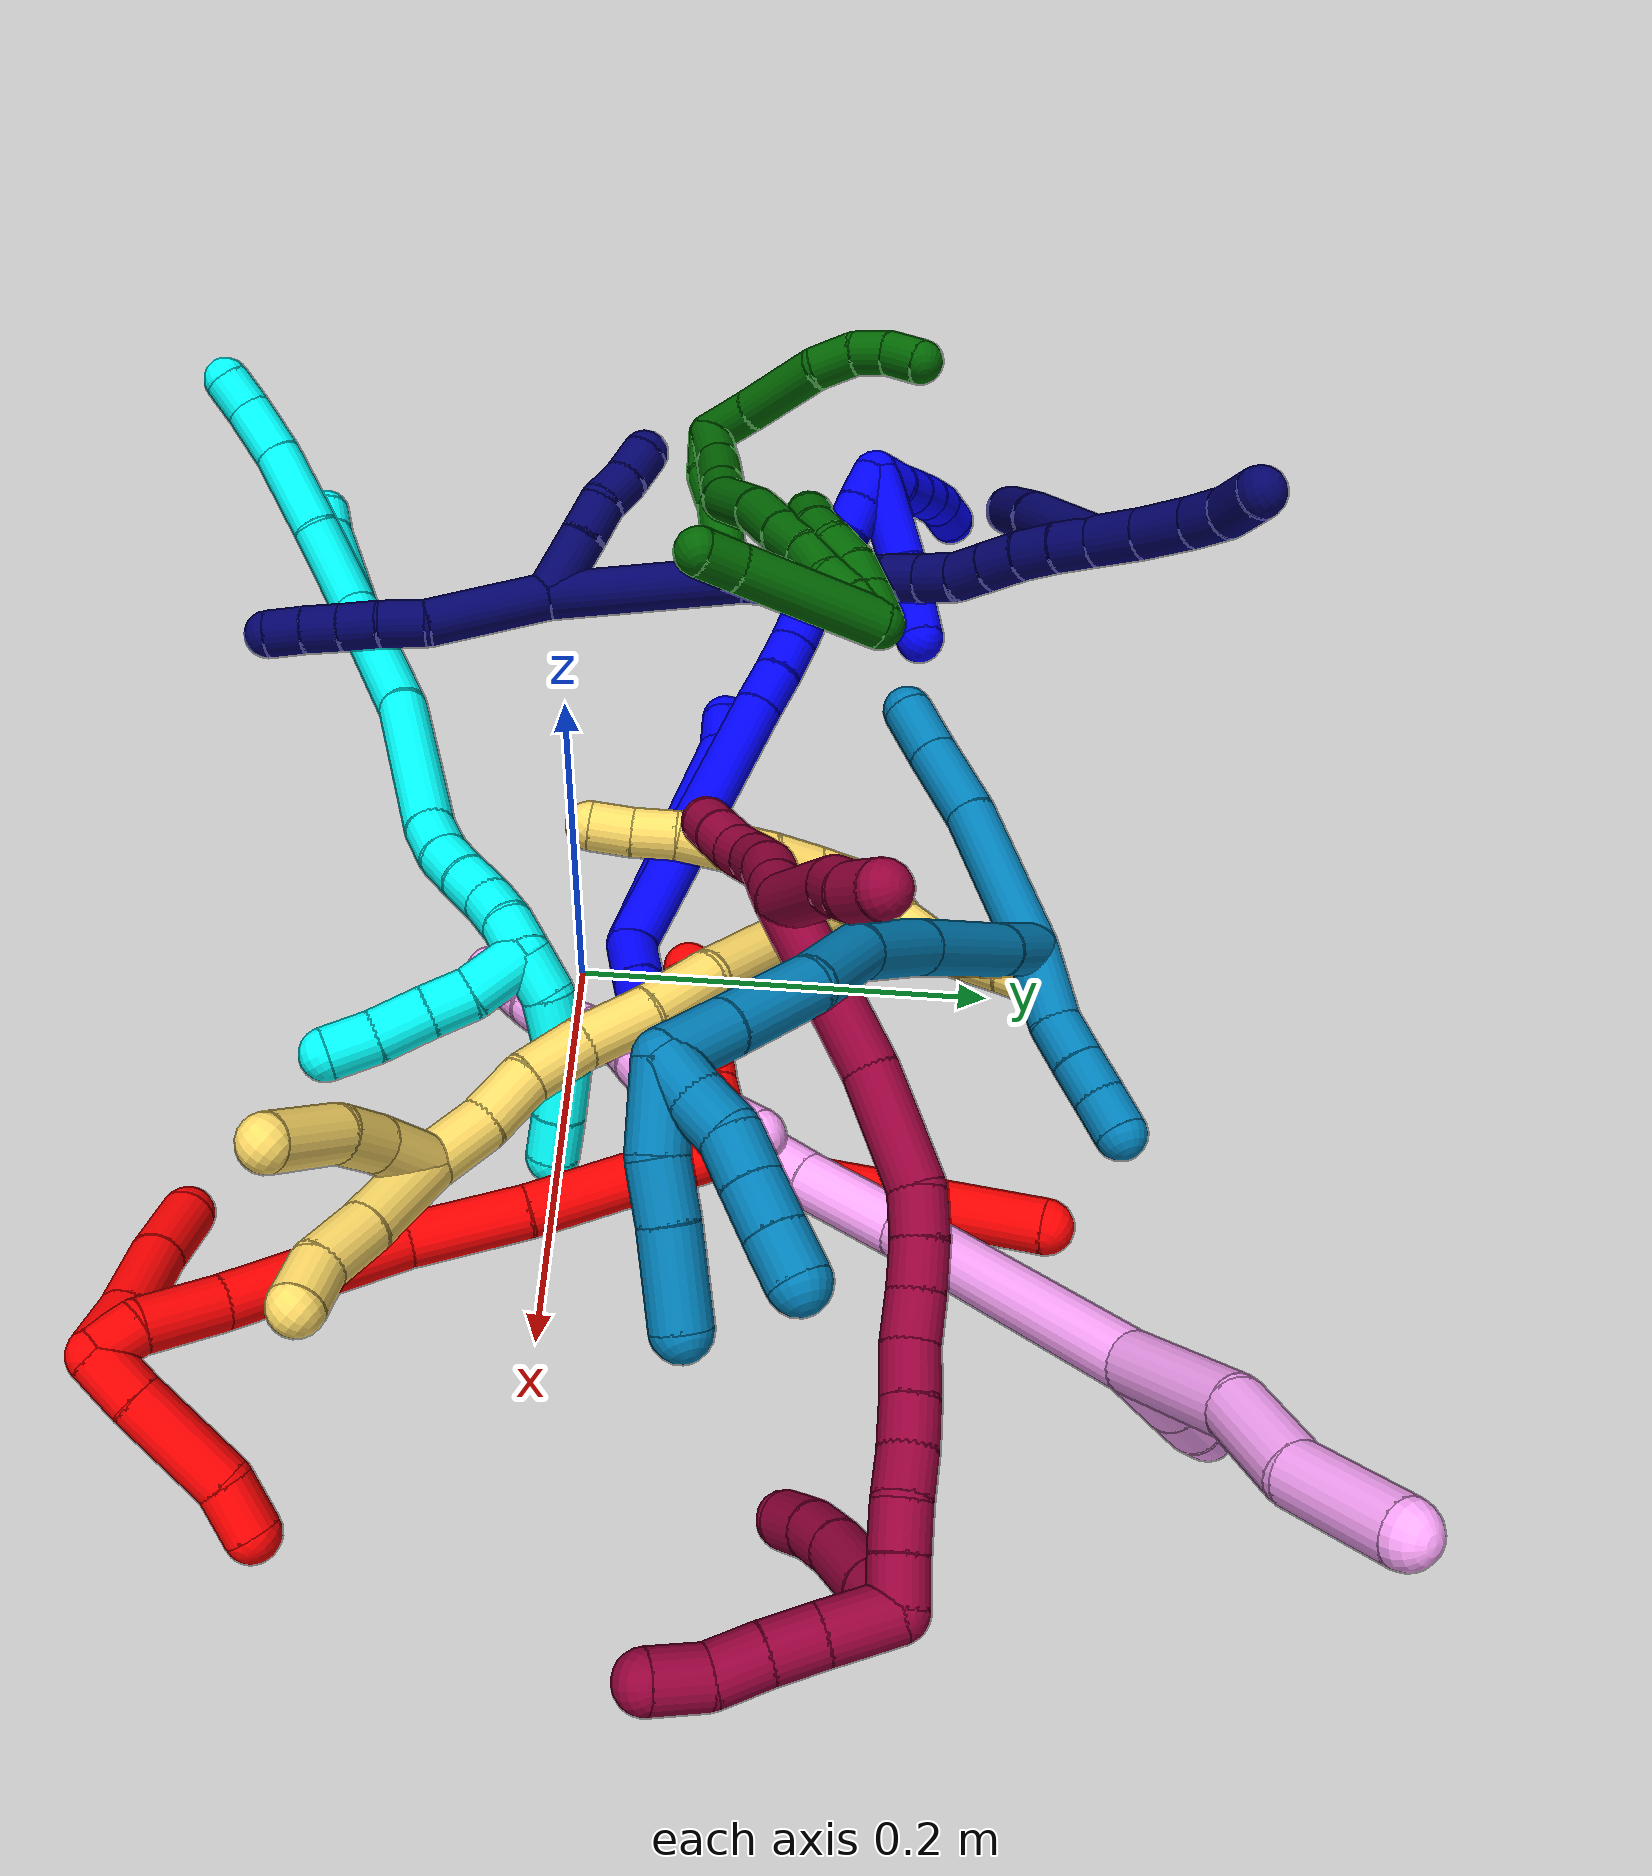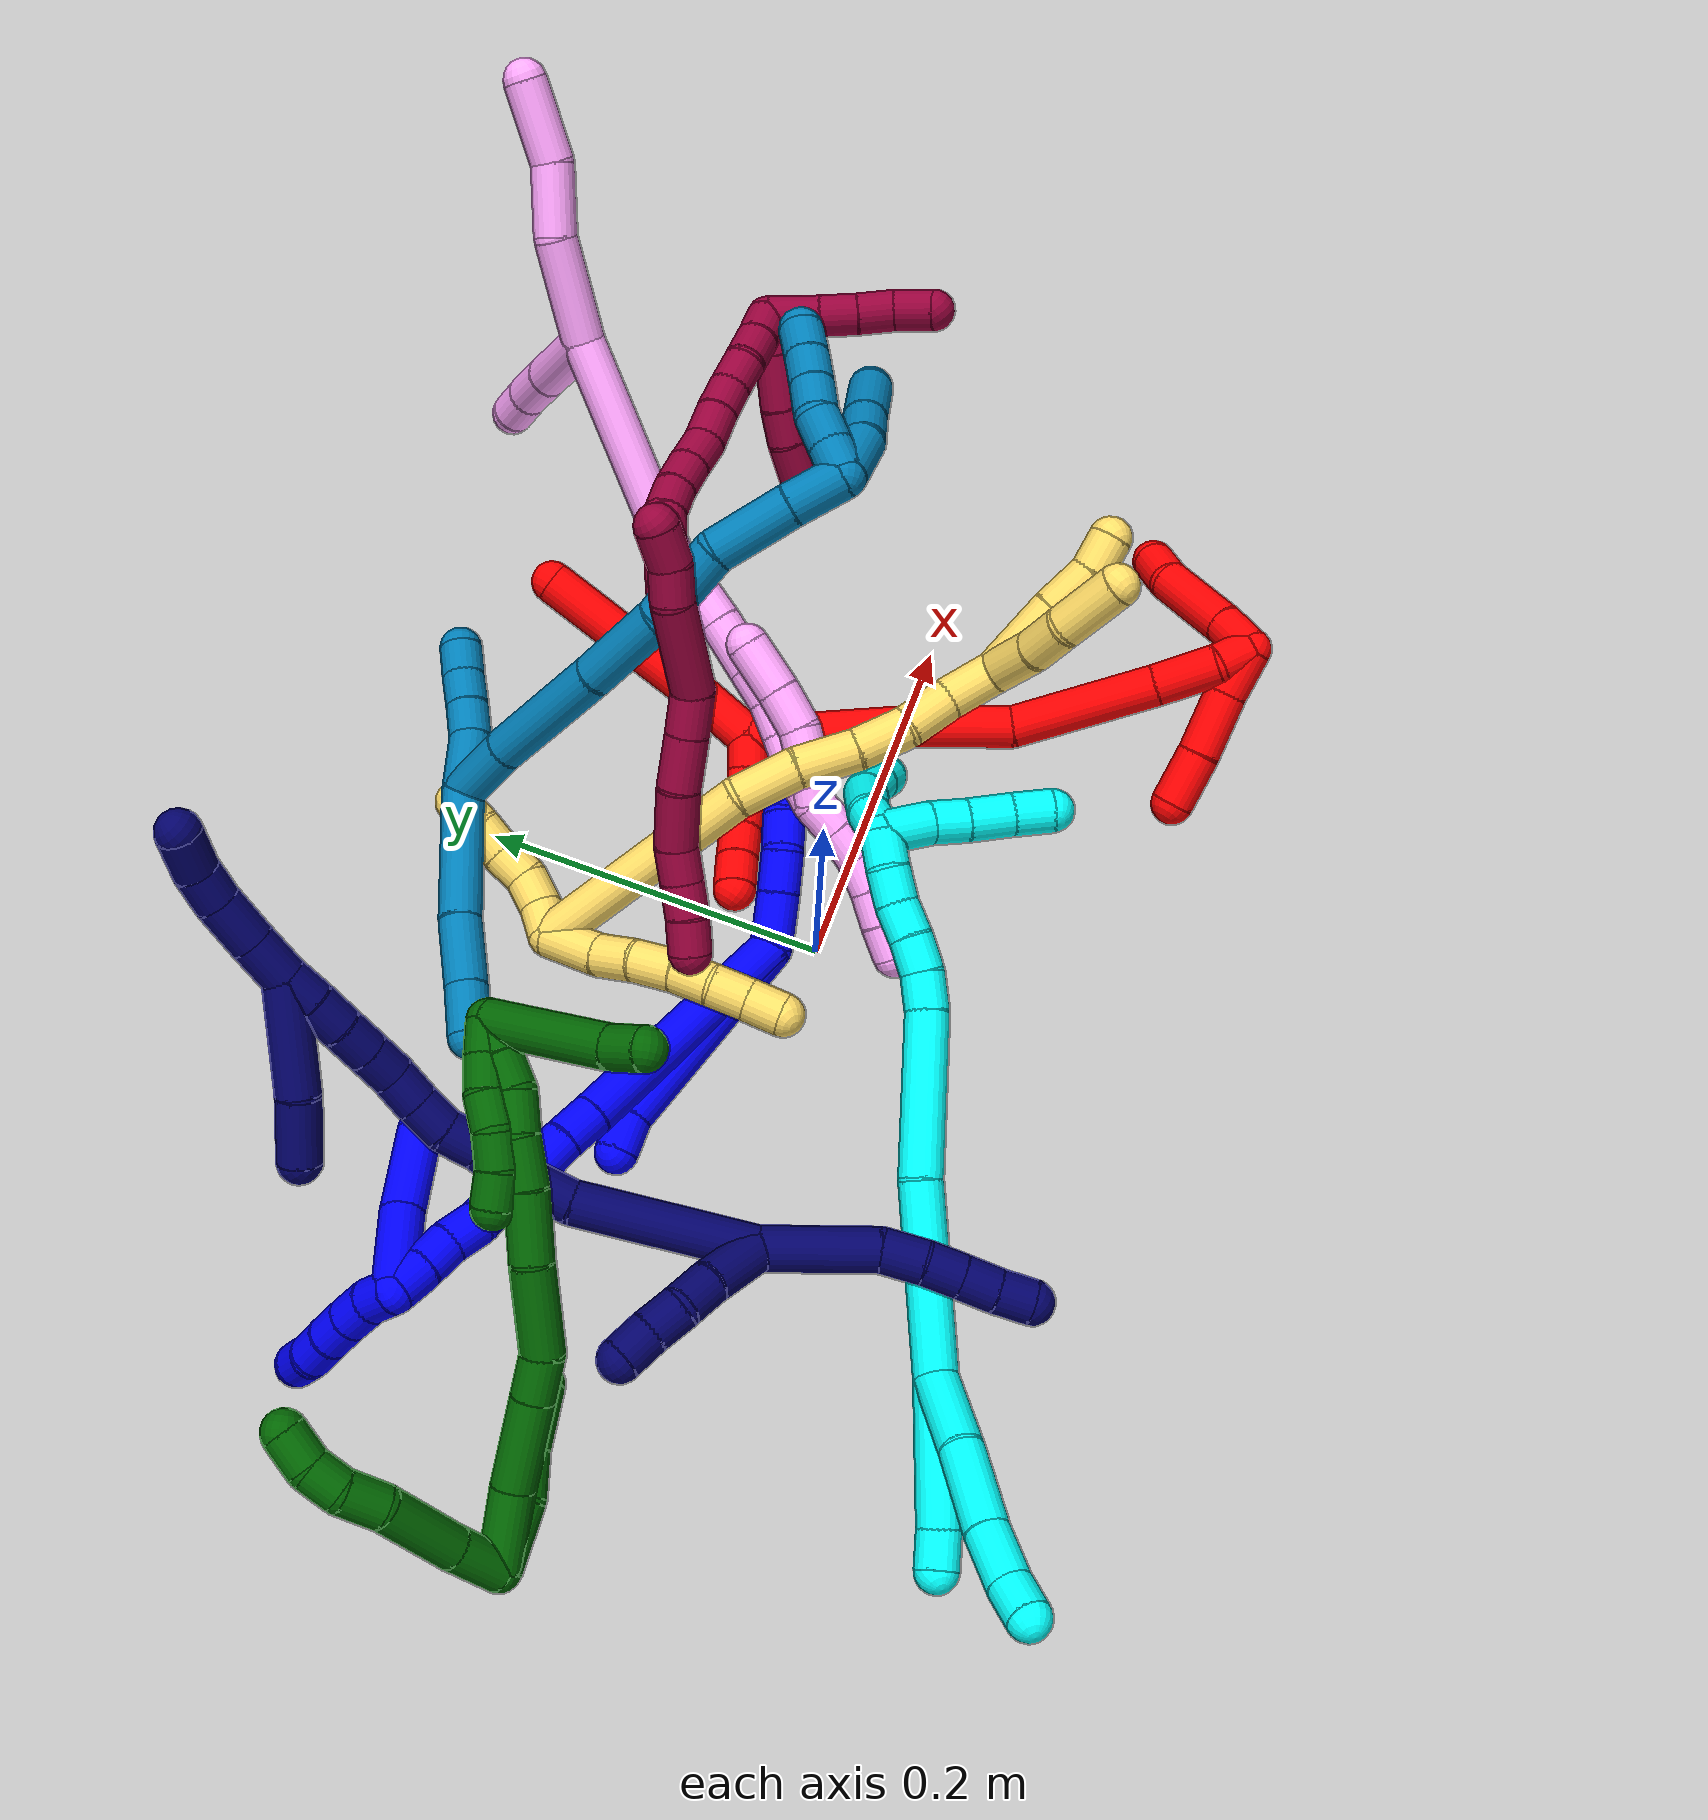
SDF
<sdf version="1.7">
 <world name="default">
  <plugin name="TubeGeneratorPlugin" filename="libtube_generator_plugin.so"/>
  <model name="photoneo_s_sensor">
   <static>1</static>
   <pose>0 0 2 1.57079 1.57079 3.14159</pose>
   <link name="link">
    <inertial><mass>0.1</mass></inertial>
    <sensor name="sensor" type="depth">
     <update_rate>30</update_rate>
     <camera>
      <horizontal_fov>1.22</horizontal_fov>
      <image><width>1920</width><height>1200</height><format>B8G8R8</format></image>
      <clip><near>0.1</near><far>4</far></clip>
      <depth_camera><output>points</output></depth_camera>
     </camera>
     <plugin name="camera_plugin" filename="libgazebo_ros_depth_camera.so">
      <baseline>0.2</baseline>
      <alwaysOn>1</alwaysOn>
      <updateRate>0.0</updateRate>
      <cameraName>camera_ir</cameraName>
      <imageTopicName>/camera/color/image_raw</imageTopicName>
      <cameraInfoTopicName>/camera/color/camera_info</cameraInfoTopicName>
      <depthImageTopicName>/camera/depth/image_raw</depthImageTopicName>
      <depthImageCameraInfoTopicName>/camera/depth/camera_info</depthImageCameraInfoTopicName>
      <pointCloudTopicName>/camera/depth/points</pointCloudTopicName>
      <frameName>fr_optical</frameName>
      <pointCloudCutoff>0.1</pointCloudCutoff>
      <pointCloudCutoffMax>2.0</pointCloudCutoffMax>
      <distortionK1>0</distortionK1>
      <distortionK2>0</distortionK2>
      <distortionK3>0</distortionK3>
      <distortionT1>0</distortionT1>
      <distortionT2>0</distortionT2>
      <CxPrime>0</CxPrime>
      <Cx>0</Cx>
      <Cy>0</Cy>
      <focalLength>0</focalLength>
      <hackBaseline>0</hackBaseline>
     </plugin>
    </sensor>
   </link>
  </model>
  <gravity>0 0 -9.8</gravity>
  <magnetic_field>6e-06 2.3e-05 -4.2e-05</magnetic_field>
  <atmosphere type="adiabatic"/>
  <physics name="default_physics" default="0" type="ode">
   <max_step_size>0.003</max_step_size>
   <real_time_factor>1</real_time_factor>
   <real_time_update_rate>1000</real_time_update_rate>
   <max_contacts>10000</max_contacts>
   <ode>
    <solver>
     <type>quick</type>
     <iters>100</iters>
     <sor>1.3</sor>
     <use_dynamic_moi_rescaling>0</use_dynamic_moi_rescaling>
    </solver>
    <constraints>
     <contact_max_correcting_vel>0</contact_max_correcting_vel>
     <contact_surface_layer>0.001</contact_surface_layer>
     <cfm>0</cfm>
     <erp>0.2</erp>
    </constraints>
   </ode>
  </physics>
  <scene><ambient>0.4 0.4 0.4 1</ambient><background>0.7 0.7 0.7 1</background><shadows>0</shadows></scene>
  <audio><device>default</device></audio>
  <spherical_coordinates>
   <surface_model>EARTH_WGS84</surface_model>
   <latitude_deg>0</latitude_deg>
   <longitude_deg>0</longitude_deg>
   <elevation>0</elevation>
   <heading_deg>0</heading_deg>
  </spherical_coordinates>
  <model name="bin">
   <static>1</static>
   <link name="bottom">
    <collision name="collision-bottom">
     <pose>0 0 -0.01 0 -0 0</pose>
     <geometry><box><size>0.8 0.6 0.02</size></box></geometry>
     <surface>
      <friction><ode><mu>100</mu><mu2>100</mu2></ode></friction>
      <contact><collide_bitmask>65535</collide_bitmask></contact>
     </surface>
    </collision>
   </link>
   <link name="west_wall">
    <collision name="collision-west_wall">
     <pose>-0.41 0 0.1 0 -0 0</pose>
     <geometry><box><size>0.02 0.6 0.2</size></box></geometry>
     <surface>
      <friction><ode><mu>100</mu><mu2>100</mu2></ode></friction>
      <contact><collide_bitmask>65535</collide_bitmask></contact>
     </surface>
    </collision>
   </link>
   <link name="east_wall">
    <collision name="collision-east_wall">
     <pose>0.41 0 0.1 0 -0 0</pose>
     <geometry><box><size>0.02 0.6 0.2</size></box></geometry>
     <surface>
      <friction><ode><mu>100</mu><mu2>100</mu2></ode></friction>
      <contact><collide_bitmask>65535</collide_bitmask></contact>
     </surface>
    </collision>
   </link>
   <link name="south_wall">
    <collision name="collision-south_wall">
     <pose>0 -0.31 0.1 0 -0 0</pose>
     <geometry><box><size>0.8 0.02 0.2</size></box></geometry>
     <surface>
      <friction><ode><mu>100</mu><mu2>100</mu2></ode></friction>
      <contact><collide_bitmask>65535</collide_bitmask></contact>
     </surface>
    </collision>
   </link>
   <link name="north_wall">
    <collision name="collision-north_wall">
     <pose>0 0.31 0.1 0 -0 0</pose>
     <geometry><box><size>0.8 0.02 0.2</size></box></geometry>
     <surface>
      <friction><ode><mu>100</mu><mu2>100</mu2></ode></friction>
      <contact><collide_bitmask>65535</collide_bitmask></contact>
     </surface>
    </collision>
   </link>
  </model>
  <model name="1">
   <static>0</static>
   <link name="1">
    <collision name="collision-cylinder-e_1_2_8">
     <pose>-0.05623 0.02482 0.018319 -0.934977 -1.06902 0.580792</pose>
     <geometry><cylinder><radius>0.0125</radius><length>0.128271</length></cylinder></geometry>
     <surface>
      <friction><ode><mu>1.16</mu><mu2>1.16</mu2><slip1>0</slip1><slip2>0</slip2></ode></friction>
      <contact><ode><kp>1e+06</kp><kd>1</kd><max_vel>0</max_vel><min_depth>0.001</min_depth></ode></contact>
     </surface>
    </collision>
    <visual name="visual-cylinder-e_1_2_8">
     <pose>-0.05623 0.02482 0.018319 -0.934977 -1.06902 0.580792</pose>
     <geometry><cylinder><radius>0.0125</radius><length>0.128271</length></cylinder></geometry>
     <material><ambient>0 0 1 1</ambient></material>
    </visual>
    <collision name="collision-cylinder-e_2_8_6">
     <pose>-0.123139 0.051321 0.037708 -1.00407 -1.38628 0.855611</pose>
     <geometry><cylinder><radius>0.0125</radius><length>0.021729</length></cylinder></geometry>
     <surface>
      <friction><ode><mu>1.16</mu><mu2>1.16</mu2><slip1>0</slip1><slip2>0</slip2></ode></friction>
      <contact><ode><kp>1e+06</kp><kd>1</kd><max_vel>0</max_vel><min_depth>0.001</min_depth></ode></contact>
     </surface>
    </collision>
    <visual name="visual-cylinder-e_2_8_6">
     <pose>-0.123139 0.051321 0.037708 -1.00407 -1.38628 0.855611</pose>
     <geometry><cylinder><radius>0.0125</radius><length>0.021729</length></cylinder></geometry>
     <material><ambient>0 0 1 1</ambient></material>
    </visual>
    <collision name="collision-cylinder-e_1_2_9">
     <pose>0.015596 -0.000876 0.003602 0.238671 1.33741 0.188922</pose>
     <geometry><cylinder><radius>0.0125</radius><length>0.032061</length></cylinder></geometry>
     <surface>
      <friction><ode><mu>1.16</mu><mu2>1.16</mu2><slip1>0</slip1><slip2>0</slip2></ode></friction>
      <contact><ode><kp>1e+06</kp><kd>1</kd><max_vel>0</max_vel><min_depth>0.001</min_depth></ode></contact>
     </surface>
    </collision>
    <visual name="visual-cylinder-e_1_2_9">
     <pose>0.015596 -0.000876 0.003602 0.238671 1.33741 0.188922</pose>
     <geometry><cylinder><radius>0.0125</radius><length>0.032061</length></cylinder></geometry>
     <material><ambient>0 0 1 1</ambient></material>
    </visual>
    <collision name="collision-cylinder-e_2_9_10">
     <pose>0.043027 -0.002033 0.009968 0.101146 1.34032 0.080185</pose>
     <geometry><cylinder><radius>0.0125</radius><length>0.024315</length></cylinder></geometry>
     <surface>
      <friction><ode><mu>1.16</mu><mu2>1.16</mu2><slip1>0</slip1><slip2>0</slip2></ode></friction>
      <contact><ode><kp>1e+06</kp><kd>1</kd><max_vel>0</max_vel><min_depth>0.001</min_depth></ode></contact>
     </surface>
    </collision>
    <visual name="visual-cylinder-e_2_9_10">
     <pose>0.043027 -0.002033 0.009968 0.101146 1.34032 0.080185</pose>
     <geometry><cylinder><radius>0.0125</radius><length>0.024315</length></cylinder></geometry>
     <material><ambient>0 0 1 1</ambient></material>
    </visual>
    <collision name="collision-cylinder-e_3_10_11">
     <pose>0.065346 -0.000481 0.012148 -1.87873 1.38938 -1.70093</pose>
     <geometry><cylinder><radius>0.0125</radius><length>0.021315</length></cylinder></geometry>
     <surface>
      <friction><ode><mu>1.16</mu><mu2>1.16</mu2><slip1>0</slip1><slip2>0</slip2></ode></friction>
      <contact><ode><kp>1e+06</kp><kd>1</kd><max_vel>0</max_vel><min_depth>0.001</min_depth></ode></contact>
     </surface>
    </collision>
    <visual name="visual-cylinder-e_3_10_11">
     <pose>0.065346 -0.000481 0.012148 -1.87873 1.38938 -1.70093</pose>
     <geometry><cylinder><radius>0.0125</radius><length>0.021315</length></cylinder></geometry>
     <material><ambient>0 0 1 1</ambient></material>
    </visual>
    <collision name="collision-cylinder-e_4_11_5">
     <pose>0.086425 0.002075 0.008156 -2.93232 1.25307 -2.85343</pose>
     <geometry><cylinder><radius>0.0125</radius><length>0.022309</length></cylinder></geometry>
     <surface>
      <friction><ode><mu>1.16</mu><mu2>1.16</mu2><slip1>0</slip1><slip2>0</slip2></ode></friction>
      <contact><ode><kp>1e+06</kp><kd>1</kd><max_vel>0</max_vel><min_depth>0.001</min_depth></ode></contact>
     </surface>
    </collision>
    <visual name="visual-cylinder-e_4_11_5">
     <pose>0.086425 0.002075 0.008156 -2.93232 1.25307 -2.85343</pose>
     <geometry><cylinder><radius>0.0125</radius><length>0.022309</length></cylinder></geometry>
     <material><ambient>0 0 1 1</ambient></material>
    </visual>
    <collision name="collision-cylinder-e_1_2_12">
     <pose>-0.059616 0.029356 0.032162 -0.739813 -0.939935 0.388924</pose>
     <geometry><cylinder><radius>0.0125</radius><length>0.147652</length></cylinder></geometry>
     <surface>
      <friction><ode><mu>1.16</mu><mu2>1.16</mu2><slip1>0</slip1><slip2>0</slip2></ode></friction>
      <contact><ode><kp>1e+06</kp><kd>1</kd><max_vel>0</max_vel><min_depth>0.001</min_depth></ode></contact>
     </surface>
    </collision>
    <visual name="visual-cylinder-e_1_2_12">
     <pose>-0.059616 0.029356 0.032162 -0.739813 -0.939935 0.388924</pose>
     <geometry><cylinder><radius>0.0125</radius><length>0.147652</length></cylinder></geometry>
     <material><ambient>0 0 1 1</ambient></material>
    </visual>
    <collision name="collision-cylinder-e_2_12_13">
     <pose>-0.128114 0.063427 0.069219 -0.766669 -0.917715 0.393316</pose>
     <geometry><cylinder><radius>0.0125</radius><length>0.022368</length></cylinder></geometry>
     <surface>
      <friction><ode><mu>1.16</mu><mu2>1.16</mu2><slip1>0</slip1><slip2>0</slip2></ode></friction>
      <contact><ode><kp>1e+06</kp><kd>1</kd><max_vel>0</max_vel><min_depth>0.001</min_depth></ode></contact>
     </surface>
    </collision>
    <visual name="visual-cylinder-e_2_12_13">
     <pose>-0.128114 0.063427 0.069219 -0.766669 -0.917715 0.393316</pose>
     <geometry><cylinder><radius>0.0125</radius><length>0.022368</length></cylinder></geometry>
     <material><ambient>0 0 1 1</ambient></material>
    </visual>
    <collision name="collision-cylinder-e_3_13_14">
     <pose>-0.145639 0.072313 0.078018 -0.818533 -0.986688 0.458265</pose>
     <geometry><cylinder><radius>0.0125</radius><length>0.020721</length></cylinder></geometry>
     <surface>
      <friction><ode><mu>1.16</mu><mu2>1.16</mu2><slip1>0</slip1><slip2>0</slip2></ode></friction>
      <contact><ode><kp>1e+06</kp><kd>1</kd><max_vel>0</max_vel><min_depth>0.001</min_depth></ode></contact>
     </surface>
    </collision>
    <visual name="visual-cylinder-e_3_13_14">
     <pose>-0.145639 0.072313 0.078018 -0.818533 -0.986688 0.458265</pose>
     <geometry><cylinder><radius>0.0125</radius><length>0.020721</length></cylinder></geometry>
     <material><ambient>0 0 1 1</ambient></material>
    </visual>
    <collision name="collision-cylinder-e_4_14_15">
     <pose>-0.16442 0.080578 0.089053 -0.521114 -0.889318 0.252725</pose>
     <geometry><cylinder><radius>0.0125</radius><length>0.026108</length></cylinder></geometry>
     <surface>
      <friction><ode><mu>1.16</mu><mu2>1.16</mu2><slip1>0</slip1><slip2>0</slip2></ode></friction>
      <contact><ode><kp>1e+06</kp><kd>1</kd><max_vel>0</max_vel><min_depth>0.001</min_depth></ode></contact>
     </surface>
    </collision>
    <visual name="visual-cylinder-e_4_14_15">
     <pose>-0.16442 0.080578 0.089053 -0.521114 -0.889318 0.252725</pose>
     <geometry><cylinder><radius>0.0125</radius><length>0.026108</length></cylinder></geometry>
     <material><ambient>0 0 1 1</ambient></material>
    </visual>
    <collision name="collision-cylinder-e_5_15_16">
     <pose>-0.183636 0.087219 0.102648 -0.375352 -0.917586 0.187064</pose>
     <geometry><cylinder><radius>0.0125</radius><length>0.02286</length></cylinder></geometry>
     <surface>
      <friction><ode><mu>1.16</mu><mu2>1.16</mu2><slip1>0</slip1><slip2>0</slip2></ode></friction>
      <contact><ode><kp>1e+06</kp><kd>1</kd><max_vel>0</max_vel><min_depth>0.001</min_depth></ode></contact>
     </surface>
    </collision>
    <visual name="visual-cylinder-e_5_15_16">
     <pose>-0.183636 0.087219 0.102648 -0.375352 -0.917586 0.187064</pose>
     <geometry><cylinder><radius>0.0125</radius><length>0.02286</length></cylinder></geometry>
     <material><ambient>0 0 1 1</ambient></material>
    </visual>
    <collision name="collision-cylinder-e_6_16_17">
     <pose>-0.199923 0.09488 0.114003 -0.807599 -0.794699 0.354863</pose>
     <geometry><cylinder><radius>0.0125</radius><length>0.020206</length></cylinder></geometry>
     <surface>
      <friction><ode><mu>1.16</mu><mu2>1.16</mu2><slip1>0</slip1><slip2>0</slip2></ode></friction>
      <contact><ode><kp>1e+06</kp><kd>1</kd><max_vel>0</max_vel><min_depth>0.001</min_depth></ode></contact>
     </surface>
    </collision>
    <visual name="visual-cylinder-e_6_16_17">
     <pose>-0.199923 0.09488 0.114003 -0.807599 -0.794699 0.354863</pose>
     <geometry><cylinder><radius>0.0125</radius><length>0.020206</length></cylinder></geometry>
     <material><ambient>0 0 1 1</ambient></material>
    </visual>
    <collision name="collision-cylinder-e_7_17_18">
     <pose>-0.215222 0.103104 0.123966 -0.550211 -0.93668 0.283664</pose>
     <geometry><cylinder><radius>0.0125</radius><length>0.020081</length></cylinder></geometry>
     <surface>
      <friction><ode><mu>1.16</mu><mu2>1.16</mu2><slip1>0</slip1><slip2>0</slip2></ode></friction>
      <contact><ode><kp>1e+06</kp><kd>1</kd><max_vel>0</max_vel><min_depth>0.001</min_depth></ode></contact>
     </surface>
    </collision>
    <visual name="visual-cylinder-e_7_17_18">
     <pose>-0.215222 0.103104 0.123966 -0.550211 -0.93668 0.283664</pose>
     <geometry><cylinder><radius>0.0125</radius><length>0.020081</length></cylinder></geometry>
     <material><ambient>0 0 1 1</ambient></material>
    </visual>
    <collision name="collision-cylinder-e_8_18_1">
     <pose>-0.230894 0.109758 0.134512 -0.57437 -0.860528 0.269454</pose>
     <geometry><cylinder><radius>0.0125</radius><length>0.020004</length></cylinder></geometry>
     <surface>
      <friction><ode><mu>1.16</mu><mu2>1.16</mu2><slip1>0</slip1><slip2>0</slip2></ode></friction>
      <contact><ode><kp>1e+06</kp><kd>1</kd><max_vel>0</max_vel><min_depth>0.001</min_depth></ode></contact>
     </surface>
    </collision>
    <visual name="visual-cylinder-e_8_18_1">
     <pose>-0.230894 0.109758 0.134512 -0.57437 -0.860528 0.269454</pose>
     <geometry><cylinder><radius>0.0125</radius><length>0.020004</length></cylinder></geometry>
     <material><ambient>0 0 1 1</ambient></material>
    </visual>
    <collision name="collision-cylinder-e_1_1_19">
     <pose>-0.241181 0.122061 0.135994 -1.99848 -0.273839 0.422067</pose>
     <geometry><cylinder><radius>0.0125</radius><length>0.02</length></cylinder></geometry>
     <surface>
      <friction><ode><mu>1.16</mu><mu2>1.16</mu2><slip1>0</slip1><slip2>0</slip2></ode></friction>
      <contact><ode><kp>1e+06</kp><kd>1</kd><max_vel>0</max_vel><min_depth>0.001</min_depth></ode></contact>
     </surface>
    </collision>
    <visual name="visual-cylinder-e_1_1_19">
     <pose>-0.241181 0.122061 0.135994 -1.99848 -0.273839 0.422067</pose>
     <geometry><cylinder><radius>0.0125</radius><length>0.02</length></cylinder></geometry>
     <material><ambient>0 0 1 1</ambient></material>
    </visual>
    <collision name="collision-cylinder-e_2_19_20">
     <pose>-0.2487 0.138567 0.127899 -2.05785 -0.502346 0.805855</pose>
     <geometry><cylinder><radius>0.0125</radius><length>0.02</length></cylinder></geometry>
     <surface>
      <friction><ode><mu>1.16</mu><mu2>1.16</mu2><slip1>0</slip1><slip2>0</slip2></ode></friction>
      <contact><ode><kp>1e+06</kp><kd>1</kd><max_vel>0</max_vel><min_depth>0.001</min_depth></ode></contact>
     </surface>
    </collision>
    <visual name="visual-cylinder-e_2_19_20">
     <pose>-0.2487 0.138567 0.127899 -2.05785 -0.502346 0.805855</pose>
     <geometry><cylinder><radius>0.0125</radius><length>0.02</length></cylinder></geometry>
     <material><ambient>0 0 1 1</ambient></material>
    </visual>
    <collision name="collision-cylinder-e_3_20_21">
     <pose>-0.258537 0.153832 0.119527 -2.0872 -0.526125 0.866557</pose>
     <geometry><cylinder><radius>0.0125</radius><length>0.02</length></cylinder></geometry>
     <surface>
      <friction><ode><mu>1.16</mu><mu2>1.16</mu2><slip1>0</slip1><slip2>0</slip2></ode></friction>
      <contact><ode><kp>1e+06</kp><kd>1</kd><max_vel>0</max_vel><min_depth>0.001</min_depth></ode></contact>
     </surface>
    </collision>
    <visual name="visual-cylinder-e_3_20_21">
     <pose>-0.258537 0.153832 0.119527 -2.0872 -0.526125 0.866557</pose>
     <geometry><cylinder><radius>0.0125</radius><length>0.02</length></cylinder></geometry>
     <material><ambient>0 0 1 1</ambient></material>
    </visual>
    <collision name="collision-cylinder-e_4_21_22">
     <pose>-0.268378 0.168673 0.110442 -2.15258 -0.502774 0.88903</pose>
     <geometry><cylinder><radius>0.0125</radius><length>0.02</length></cylinder></geometry>
     <surface>
      <friction><ode><mu>1.16</mu><mu2>1.16</mu2><slip1>0</slip1><slip2>0</slip2></ode></friction>
      <contact><ode><kp>1e+06</kp><kd>1</kd><max_vel>0</max_vel><min_depth>0.001</min_depth></ode></contact>
     </surface>
    </collision>
    <visual name="visual-cylinder-e_4_21_22">
     <pose>-0.268378 0.168673 0.110442 -2.15258 -0.502774 0.88903</pose>
     <geometry><cylinder><radius>0.0125</radius><length>0.02</length></cylinder></geometry>
     <material><ambient>0 0 1 1</ambient></material>
    </visual>
    <collision name="collision-cylinder-e_5_22_4">
     <pose>-0.275321 0.183594 0.099484 -2.25054 -0.214144 0.442769</pose>
     <geometry><cylinder><radius>0.0125</radius><length>0.02</length></cylinder></geometry>
     <surface>
      <friction><ode><mu>1.16</mu><mu2>1.16</mu2><slip1>0</slip1><slip2>0</slip2></ode></friction>
      <contact><ode><kp>1e+06</kp><kd>1</kd><max_vel>0</max_vel><min_depth>0.001</min_depth></ode></contact>
     </surface>
    </collision>
    <visual name="visual-cylinder-e_5_22_4">
     <pose>-0.275321 0.183594 0.099484 -2.25054 -0.214144 0.442769</pose>
     <geometry><cylinder><radius>0.0125</radius><length>0.02</length></cylinder></geometry>
     <material><ambient>0 0 1 1</ambient></material>
    </visual>
    <collision name="collision-cylinder-e_1_1_23">
     <pose>-0.216405 0.121929 0.129989 -2.42964 1.03161 -1.98077</pose>
     <geometry><cylinder><radius>0.0125</radius><length>0.051441</length></cylinder></geometry>
     <surface>
      <friction><ode><mu>1.16</mu><mu2>1.16</mu2><slip1>0</slip1><slip2>0</slip2></ode></friction>
      <contact><ode><kp>1e+06</kp><kd>1</kd><max_vel>0</max_vel><min_depth>0.001</min_depth></ode></contact>
     </surface>
    </collision>
    <visual name="visual-cylinder-e_1_1_23">
     <pose>-0.216405 0.121929 0.129989 -2.42964 1.03161 -1.98077</pose>
     <geometry><cylinder><radius>0.0125</radius><length>0.051441</length></cylinder></geometry>
     <material><ambient>0 0 1 1</ambient></material>
    </visual>
    <collision name="collision-cylinder-e_2_23_3">
     <pose>-0.170884 0.133771 0.114584 -2.60526 1.30872 -2.45366</pose>
     <geometry><cylinder><radius>0.0125</radius><length>0.048559</length></cylinder></geometry>
     <surface>
      <friction><ode><mu>1.16</mu><mu2>1.16</mu2><slip1>0</slip1><slip2>0</slip2></ode></friction>
      <contact><ode><kp>1e+06</kp><kd>1</kd><max_vel>0</max_vel><min_depth>0.001</min_depth></ode></contact>
     </surface>
    </collision>
    <visual name="visual-cylinder-e_2_23_3">
     <pose>-0.170884 0.133771 0.114584 -2.60526 1.30872 -2.45366</pose>
     <geometry><cylinder><radius>0.0125</radius><length>0.048559</length></cylinder></geometry>
     <material><ambient>0 0 1 1</ambient></material>
    </visual>
    <collision name="collision-sphere-3">
     <pose>-0.147433 0.136985 0.109176 0 -0 0</pose>
     <geometry><sphere><radius>0.0125</radius></sphere></geometry>
     <surface>
      <friction><ode><mu>1.16</mu><mu2>1.16</mu2><slip1>0</slip1><slip2>0</slip2></ode></friction>
      <contact><ode><kp>1e+06</kp><kd>1</kd><max_vel>0</max_vel><min_depth>0.001</min_depth></ode></contact>
     </surface>
    </collision>
    <visual name="visual-sphere-3">
     <pose>-0.147433 0.136985 0.109176 0 -0 0</pose>
     <geometry><sphere><radius>0.0125</radius></sphere></geometry>
     <material><ambient>0 0 1 1</ambient></material>
    </visual>
    <collision name="collision-sphere-23">
     <pose>-0.194334 0.130557 0.119991 0 -0 0</pose>
     <geometry><sphere><radius>0.0125</radius></sphere></geometry>
     <surface>
      <friction><ode><mu>1.16</mu><mu2>1.16</mu2><slip1>0</slip1><slip2>0</slip2></ode></friction>
      <contact><ode><kp>1e+06</kp><kd>1</kd><max_vel>0</max_vel><min_depth>0.001</min_depth></ode></contact>
     </surface>
    </collision>
    <visual name="visual-sphere-23">
     <pose>-0.194334 0.130557 0.119991 0 -0 0</pose>
     <geometry><sphere><radius>0.0125</radius></sphere></geometry>
     <material><ambient>0 0 1 1</ambient></material>
    </visual>
    <collision name="collision-sphere-4">
     <pose>-0.277446 0.191194 0.093342 0 -0 0</pose>
     <geometry><sphere><radius>0.0125</radius></sphere></geometry>
     <surface>
      <friction><ode><mu>1.16</mu><mu2>1.16</mu2><slip1>0</slip1><slip2>0</slip2></ode></friction>
      <contact><ode><kp>1e+06</kp><kd>1</kd><max_vel>0</max_vel><min_depth>0.001</min_depth></ode></contact>
     </surface>
    </collision>
    <visual name="visual-sphere-4">
     <pose>-0.277446 0.191194 0.093342 0 -0 0</pose>
     <geometry><sphere><radius>0.0125</radius></sphere></geometry>
     <material><ambient>0 0 1 1</ambient></material>
    </visual>
    <collision name="collision-sphere-22">
     <pose>-0.273196 0.175994 0.105627 0 -0 0</pose>
     <geometry><sphere><radius>0.0125</radius></sphere></geometry>
     <surface>
      <friction><ode><mu>1.16</mu><mu2>1.16</mu2><slip1>0</slip1><slip2>0</slip2></ode></friction>
      <contact><ode><kp>1e+06</kp><kd>1</kd><max_vel>0</max_vel><min_depth>0.001</min_depth></ode></contact>
     </surface>
    </collision>
    <visual name="visual-sphere-22">
     <pose>-0.273196 0.175994 0.105627 0 -0 0</pose>
     <geometry><sphere><radius>0.0125</radius></sphere></geometry>
     <material><ambient>0 0 1 1</ambient></material>
    </visual>
    <collision name="collision-sphere-21">
     <pose>-0.263559 0.161352 0.115257 0 -0 0</pose>
     <geometry><sphere><radius>0.0125</radius></sphere></geometry>
     <surface>
      <friction><ode><mu>1.16</mu><mu2>1.16</mu2><slip1>0</slip1><slip2>0</slip2></ode></friction>
      <contact><ode><kp>1e+06</kp><kd>1</kd><max_vel>0</max_vel><min_depth>0.001</min_depth></ode></contact>
     </surface>
    </collision>
    <visual name="visual-sphere-21">
     <pose>-0.263559 0.161352 0.115257 0 -0 0</pose>
     <geometry><sphere><radius>0.0125</radius></sphere></geometry>
     <material><ambient>0 0 1 1</ambient></material>
    </visual>
    <collision name="collision-sphere-20">
     <pose>-0.253515 0.146312 0.123797 0 -0 0</pose>
     <geometry><sphere><radius>0.0125</radius></sphere></geometry>
     <surface>
      <friction><ode><mu>1.16</mu><mu2>1.16</mu2><slip1>0</slip1><slip2>0</slip2></ode></friction>
      <contact><ode><kp>1e+06</kp><kd>1</kd><max_vel>0</max_vel><min_depth>0.001</min_depth></ode></contact>
     </surface>
    </collision>
    <visual name="visual-sphere-20">
     <pose>-0.253515 0.146312 0.123797 0 -0 0</pose>
     <geometry><sphere><radius>0.0125</radius></sphere></geometry>
     <material><ambient>0 0 1 1</ambient></material>
    </visual>
    <collision name="collision-sphere-11">
     <pose>0.075829 0.001351 0.011565 0 -0 0</pose>
     <geometry><sphere><radius>0.0125</radius></sphere></geometry>
     <surface>
      <friction><ode><mu>1.16</mu><mu2>1.16</mu2><slip1>0</slip1><slip2>0</slip2></ode></friction>
      <contact><ode><kp>1e+06</kp><kd>1</kd><max_vel>0</max_vel><min_depth>0.001</min_depth></ode></contact>
     </surface>
    </collision>
    <visual name="visual-sphere-11">
     <pose>0.075829 0.001351 0.011565 0 -0 0</pose>
     <geometry><sphere><radius>0.0125</radius></sphere></geometry>
     <material><ambient>0 0 1 1</ambient></material>
    </visual>
    <collision name="collision-sphere-10">
     <pose>0.054863 -0.002314 0.012731 0 -0 0</pose>
     <geometry><sphere><radius>0.0125</radius></sphere></geometry>
     <surface>
      <friction><ode><mu>1.16</mu><mu2>1.16</mu2><slip1>0</slip1><slip2>0</slip2></ode></friction>
      <contact><ode><kp>1e+06</kp><kd>1</kd><max_vel>0</max_vel><min_depth>0.001</min_depth></ode></contact>
     </surface>
    </collision>
    <visual name="visual-sphere-10">
     <pose>0.054863 -0.002314 0.012731 0 -0 0</pose>
     <geometry><sphere><radius>0.0125</radius></sphere></geometry>
     <material><ambient>0 0 1 1</ambient></material>
    </visual>
    <collision name="collision-sphere-6">
     <pose>-0.133819 0.053003 0.038778 0 -0 0</pose>
     <geometry><sphere><radius>0.0125</radius></sphere></geometry>
     <surface>
      <friction><ode><mu>1.16</mu><mu2>1.16</mu2><slip1>0</slip1><slip2>0</slip2></ode></friction>
      <contact><ode><kp>1e+06</kp><kd>1</kd><max_vel>0</max_vel><min_depth>0.001</min_depth></ode></contact>
     </surface>
    </collision>
    <visual name="visual-sphere-6">
     <pose>-0.133819 0.053003 0.038778 0 -0 0</pose>
     <geometry><sphere><radius>0.0125</radius></sphere></geometry>
     <material><ambient>0 0 1 1</ambient></material>
    </visual>
    <collision name="collision-sphere-9">
     <pose>0.031192 -0.001753 0.007205 0 -0 0</pose>
     <geometry><sphere><radius>0.0125</radius></sphere></geometry>
     <surface>
      <friction><ode><mu>1.16</mu><mu2>1.16</mu2><slip1>0</slip1><slip2>0</slip2></ode></friction>
      <contact><ode><kp>1e+06</kp><kd>1</kd><max_vel>0</max_vel><min_depth>0.001</min_depth></ode></contact>
     </surface>
    </collision>
    <visual name="visual-sphere-9">
     <pose>0.031192 -0.001753 0.007205 0 -0 0</pose>
     <geometry><sphere><radius>0.0125</radius></sphere></geometry>
     <material><ambient>0 0 1 1</ambient></material>
    </visual>
    <collision name="collision-sphere-2">
     <geometry><sphere><radius>0.0125</radius></sphere></geometry>
     <surface>
      <friction><ode><mu>1.16</mu><mu2>1.16</mu2><slip1>0</slip1><slip2>0</slip2></ode></friction>
      <contact><ode><kp>1e+06</kp><kd>1</kd><max_vel>0</max_vel><min_depth>0.001</min_depth></ode></contact>
     </surface>
    </collision>
    <visual name="visual-sphere-2">
     <geometry><sphere><radius>0.0125</radius></sphere></geometry>
     <material><ambient>0 0 1 1</ambient></material>
    </visual>
    <collision name="collision-sphere-19">
     <pose>-0.243886 0.130822 0.132001 0 -0 0</pose>
     <geometry><sphere><radius>0.0125</radius></sphere></geometry>
     <surface>
      <friction><ode><mu>1.16</mu><mu2>1.16</mu2><slip1>0</slip1><slip2>0</slip2></ode></friction>
      <contact><ode><kp>1e+06</kp><kd>1</kd><max_vel>0</max_vel><min_depth>0.001</min_depth></ode></contact>
     </surface>
    </collision>
    <visual name="visual-sphere-19">
     <pose>-0.243886 0.130822 0.132001 0 -0 0</pose>
     <geometry><sphere><radius>0.0125</radius></sphere></geometry>
     <material><ambient>0 0 1 1</ambient></material>
    </visual>
    <collision name="collision-sphere-8">
     <pose>-0.112459 0.04964 0.036637 0 -0 0</pose>
     <geometry><sphere><radius>0.0125</radius></sphere></geometry>
     <surface>
      <friction><ode><mu>1.16</mu><mu2>1.16</mu2><slip1>0</slip1><slip2>0</slip2></ode></friction>
      <contact><ode><kp>1e+06</kp><kd>1</kd><max_vel>0</max_vel><min_depth>0.001</min_depth></ode></contact>
     </surface>
    </collision>
    <visual name="visual-sphere-8">
     <pose>-0.112459 0.04964 0.036637 0 -0 0</pose>
     <geometry><sphere><radius>0.0125</radius></sphere></geometry>
     <material><ambient>0 0 1 1</ambient></material>
    </visual>
    <collision name="collision-sphere-5">
     <pose>0.097021 0.002799 0.004748 0 -0 0</pose>
     <geometry><sphere><radius>0.0125</radius></sphere></geometry>
     <surface>
      <friction><ode><mu>1.16</mu><mu2>1.16</mu2><slip1>0</slip1><slip2>0</slip2></ode></friction>
      <contact><ode><kp>1e+06</kp><kd>1</kd><max_vel>0</max_vel><min_depth>0.001</min_depth></ode></contact>
     </surface>
    </collision>
    <visual name="visual-sphere-5">
     <pose>0.097021 0.002799 0.004748 0 -0 0</pose>
     <geometry><sphere><radius>0.0125</radius></sphere></geometry>
     <material><ambient>0 0 1 1</ambient></material>
    </visual>
    <collision name="collision-sphere-12">
     <pose>-0.119232 0.058712 0.064325 0 -0 0</pose>
     <geometry><sphere><radius>0.0125</radius></sphere></geometry>
     <surface>
      <friction><ode><mu>1.16</mu><mu2>1.16</mu2><slip1>0</slip1><slip2>0</slip2></ode></friction>
      <contact><ode><kp>1e+06</kp><kd>1</kd><max_vel>0</max_vel><min_depth>0.001</min_depth></ode></contact>
     </surface>
    </collision>
    <visual name="visual-sphere-12">
     <pose>-0.119232 0.058712 0.064325 0 -0 0</pose>
     <geometry><sphere><radius>0.0125</radius></sphere></geometry>
     <material><ambient>0 0 1 1</ambient></material>
    </visual>
    <collision name="collision-sphere-13">
     <pose>-0.136997 0.068141 0.074114 0 -0 0</pose>
     <geometry><sphere><radius>0.0125</radius></sphere></geometry>
     <surface>
      <friction><ode><mu>1.16</mu><mu2>1.16</mu2><slip1>0</slip1><slip2>0</slip2></ode></friction>
      <contact><ode><kp>1e+06</kp><kd>1</kd><max_vel>0</max_vel><min_depth>0.001</min_depth></ode></contact>
     </surface>
    </collision>
    <visual name="visual-sphere-13">
     <pose>-0.136997 0.068141 0.074114 0 -0 0</pose>
     <geometry><sphere><radius>0.0125</radius></sphere></geometry>
     <material><ambient>0 0 1 1</ambient></material>
    </visual>
    <collision name="collision-sphere-14">
     <pose>-0.154282 0.076484 0.081922 0 -0 0</pose>
     <geometry><sphere><radius>0.0125</radius></sphere></geometry>
     <surface>
      <friction><ode><mu>1.16</mu><mu2>1.16</mu2><slip1>0</slip1><slip2>0</slip2></ode></friction>
      <contact><ode><kp>1e+06</kp><kd>1</kd><max_vel>0</max_vel><min_depth>0.001</min_depth></ode></contact>
     </surface>
    </collision>
    <visual name="visual-sphere-14">
     <pose>-0.154282 0.076484 0.081922 0 -0 0</pose>
     <geometry><sphere><radius>0.0125</radius></sphere></geometry>
     <material><ambient>0 0 1 1</ambient></material>
    </visual>
    <collision name="collision-sphere-15">
     <pose>-0.174559 0.084672 0.096185 0 -0 0</pose>
     <geometry><sphere><radius>0.0125</radius></sphere></geometry>
     <surface>
      <friction><ode><mu>1.16</mu><mu2>1.16</mu2><slip1>0</slip1><slip2>0</slip2></ode></friction>
      <contact><ode><kp>1e+06</kp><kd>1</kd><max_vel>0</max_vel><min_depth>0.001</min_depth></ode></contact>
     </surface>
    </collision>
    <visual name="visual-sphere-15">
     <pose>-0.174559 0.084672 0.096185 0 -0 0</pose>
     <geometry><sphere><radius>0.0125</radius></sphere></geometry>
     <material><ambient>0 0 1 1</ambient></material>
    </visual>
    <collision name="collision-sphere-16">
     <pose>-0.192713 0.089766 0.109111 0 -0 0</pose>
     <geometry><sphere><radius>0.0125</radius></sphere></geometry>
     <surface>
      <friction><ode><mu>1.16</mu><mu2>1.16</mu2><slip1>0</slip1><slip2>0</slip2></ode></friction>
      <contact><ode><kp>1e+06</kp><kd>1</kd><max_vel>0</max_vel><min_depth>0.001</min_depth></ode></contact>
     </surface>
    </collision>
    <visual name="visual-sphere-16">
     <pose>-0.192713 0.089766 0.109111 0 -0 0</pose>
     <geometry><sphere><radius>0.0125</radius></sphere></geometry>
     <material><ambient>0 0 1 1</ambient></material>
    </visual>
    <collision name="collision-sphere-17">
     <pose>-0.207133 0.099994 0.118895 0 -0 0</pose>
     <geometry><sphere><radius>0.0125</radius></sphere></geometry>
     <surface>
      <friction><ode><mu>1.16</mu><mu2>1.16</mu2><slip1>0</slip1><slip2>0</slip2></ode></friction>
      <contact><ode><kp>1e+06</kp><kd>1</kd><max_vel>0</max_vel><min_depth>0.001</min_depth></ode></contact>
     </surface>
    </collision>
    <visual name="visual-sphere-17">
     <pose>-0.207133 0.099994 0.118895 0 -0 0</pose>
     <geometry><sphere><radius>0.0125</radius></sphere></geometry>
     <material><ambient>0 0 1 1</ambient></material>
    </visual>
    <collision name="collision-sphere-18">
     <pose>-0.22331 0.106215 0.129037 0 -0 0</pose>
     <geometry><sphere><radius>0.0125</radius></sphere></geometry>
     <surface>
      <friction><ode><mu>1.16</mu><mu2>1.16</mu2><slip1>0</slip1><slip2>0</slip2></ode></friction>
      <contact><ode><kp>1e+06</kp><kd>1</kd><max_vel>0</max_vel><min_depth>0.001</min_depth></ode></contact>
     </surface>
    </collision>
    <visual name="visual-sphere-18">
     <pose>-0.22331 0.106215 0.129037 0 -0 0</pose>
     <geometry><sphere><radius>0.0125</radius></sphere></geometry>
     <material><ambient>0 0 1 1</ambient></material>
    </visual>
    <collision name="collision-sphere-1">
     <pose>-0.238477 0.113301 0.139987 0 -0 0</pose>
     <geometry><sphere><radius>0.0125</radius></sphere></geometry>
     <surface>
      <friction><ode><mu>1.16</mu><mu2>1.16</mu2><slip1>0</slip1><slip2>0</slip2></ode></friction>
      <contact><ode><kp>1e+06</kp><kd>1</kd><max_vel>0</max_vel><min_depth>0.001</min_depth></ode></contact>
     </surface>
    </collision>
    <visual name="visual-sphere-1">
     <pose>-0.238477 0.113301 0.139987 0 -0 0</pose>
     <geometry><sphere><radius>0.0125</radius></sphere></geometry>
     <material><ambient>0 0 1 1</ambient></material>
    </visual>
    <inertial>
     <pose>-0.115267 0.066523 0.064206 0 -0 0</pose>
     <mass>0.75</mass>
     <inertia>
      <ixx>0.00032</ixx>
      <ixy>0</ixy>
      <ixz>0</ixz>
      <iyy>0.000575</iyy>
      <iyz>0</iyz>
      <izz>0.000175</izz>
     </inertia>
    </inertial>
   </link>
   <pose>-0.010982 0.023612 0.01185 -0.383411 -0.054097 0.187583</pose>
  </model>
  <model name="2">
   <static>0</static>
   <link name="2">
    <collision name="collision-cylinder-e_1_2_8">
     <pose>-0.001761 0.018563 0.003416 -1.38879 -0.09304 0.077496</pose>
     <geometry><cylinder><radius>0.0125</radius><length>0.037914</length></cylinder></geometry>
     <surface>
      <friction><ode><mu>1.16</mu><mu2>1.16</mu2><slip1>0</slip1><slip2>0</slip2></ode></friction>
      <contact><ode><kp>1e+06</kp><kd>1</kd><max_vel>0</max_vel><min_depth>0.001</min_depth></ode></contact>
     </surface>
    </collision>
    <visual name="visual-cylinder-e_1_2_8">
     <pose>-0.001761 0.018563 0.003416 -1.38879 -0.09304 0.077496</pose>
     <geometry><cylinder><radius>0.0125</radius><length>0.037914</length></cylinder></geometry>
     <material><ambient>1 0 0 1</ambient></material>
    </visual>
    <collision name="collision-cylinder-e_2_8_6">
     <pose>-0.024381 0.088881 0.012046 -1.4704 -0.381367 0.345638</pose>
     <geometry><cylinder><radius>0.0125</radius><length>0.112086</length></cylinder></geometry>
     <surface>
      <friction><ode><mu>1.16</mu><mu2>1.16</mu2><slip1>0</slip1><slip2>0</slip2></ode></friction>
      <contact><ode><kp>1e+06</kp><kd>1</kd><max_vel>0</max_vel><min_depth>0.001</min_depth></ode></contact>
     </surface>
    </collision>
    <visual name="visual-cylinder-e_2_8_6">
     <pose>-0.024381 0.088881 0.012046 -1.4704 -0.381367 0.345638</pose>
     <geometry><cylinder><radius>0.0125</radius><length>0.112086</length></cylinder></geometry>
     <material><ambient>1 0 0 1</ambient></material>
    </visual>
    <collision name="collision-cylinder-e_1_2_9">
     <pose>0.001518 -0.005103 -0.008465 2.59914 0.152409 0.535938</pose>
     <geometry><cylinder><radius>0.0125</radius><length>0.02</length></cylinder></geometry>
     <surface>
      <friction><ode><mu>1.16</mu><mu2>1.16</mu2><slip1>0</slip1><slip2>0</slip2></ode></friction>
      <contact><ode><kp>1e+06</kp><kd>1</kd><max_vel>0</max_vel><min_depth>0.001</min_depth></ode></contact>
     </surface>
    </collision>
    <visual name="visual-cylinder-e_1_2_9">
     <pose>0.001518 -0.005103 -0.008465 2.59914 0.152409 0.535938</pose>
     <geometry><cylinder><radius>0.0125</radius><length>0.02</length></cylinder></geometry>
     <material><ambient>1 0 0 1</ambient></material>
    </visual>
    <collision name="collision-cylinder-e_2_9_10">
     <pose>0.002905 -0.014806 -0.025808 2.66342 -0.013121 -0.053818</pose>
     <geometry><cylinder><radius>0.0125</radius><length>0.02</length></cylinder></geometry>
     <surface>
      <friction><ode><mu>1.16</mu><mu2>1.16</mu2><slip1>0</slip1><slip2>0</slip2></ode></friction>
      <contact><ode><kp>1e+06</kp><kd>1</kd><max_vel>0</max_vel><min_depth>0.001</min_depth></ode></contact>
     </surface>
    </collision>
    <visual name="visual-cylinder-e_2_9_10">
     <pose>0.002905 -0.014806 -0.025808 2.66342 -0.013121 -0.053818</pose>
     <geometry><cylinder><radius>0.0125</radius><length>0.02</length></cylinder></geometry>
     <material><ambient>1 0 0 1</ambient></material>
    </visual>
    <collision name="collision-cylinder-e_3_10_11">
     <pose>-0.000383 -0.024004 -0.042986 2.63586 -0.321235 -1.12007</pose>
     <geometry><cylinder><radius>0.0125</radius><length>0.02</length></cylinder></geometry>
     <surface>
      <friction><ode><mu>1.16</mu><mu2>1.16</mu2><slip1>0</slip1><slip2>0</slip2></ode></friction>
      <contact><ode><kp>1e+06</kp><kd>1</kd><max_vel>0</max_vel><min_depth>0.001</min_depth></ode></contact>
     </surface>
    </collision>
    <visual name="visual-cylinder-e_3_10_11">
     <pose>-0.000383 -0.024004 -0.042986 2.63586 -0.321235 -1.12007</pose>
     <geometry><cylinder><radius>0.0125</radius><length>0.02</length></cylinder></geometry>
     <material><ambient>1 0 0 1</ambient></material>
    </visual>
    <collision name="collision-cylinder-e_4_11_12">
     <pose>-0.006863 -0.033678 -0.059236 2.57318 -0.338655 -1.05903</pose>
     <geometry><cylinder><radius>0.0125</radius><length>0.02</length></cylinder></geometry>
     <surface>
      <friction><ode><mu>1.16</mu><mu2>1.16</mu2><slip1>0</slip1><slip2>0</slip2></ode></friction>
      <contact><ode><kp>1e+06</kp><kd>1</kd><max_vel>0</max_vel><min_depth>0.001</min_depth></ode></contact>
     </surface>
    </collision>
    <visual name="visual-cylinder-e_4_11_12">
     <pose>-0.006863 -0.033678 -0.059236 2.57318 -0.338655 -1.05903</pose>
     <geometry><cylinder><radius>0.0125</radius><length>0.02</length></cylinder></geometry>
     <material><ambient>1 0 0 1</ambient></material>
    </visual>
    <collision name="collision-cylinder-e_5_12_5">
     <pose>-0.013247 -0.044059 -0.07509 2.55063 -0.311181 -0.951647</pose>
     <geometry><cylinder><radius>0.0125</radius><length>0.02</length></cylinder></geometry>
     <surface>
      <friction><ode><mu>1.16</mu><mu2>1.16</mu2><slip1>0</slip1><slip2>0</slip2></ode></friction>
      <contact><ode><kp>1e+06</kp><kd>1</kd><max_vel>0</max_vel><min_depth>0.001</min_depth></ode></contact>
     </surface>
    </collision>
    <visual name="visual-cylinder-e_5_12_5">
     <pose>-0.013247 -0.044059 -0.07509 2.55063 -0.311181 -0.951647</pose>
     <geometry><cylinder><radius>0.0125</radius><length>0.02</length></cylinder></geometry>
     <material><ambient>1 0 0 1</ambient></material>
    </visual>
    <collision name="collision-cylinder-e_1_2_13">
     <pose>0.011739 -0.038214 0.029073 0.920414 0.239782 0.119292</pose>
     <geometry><cylinder><radius>0.0125</radius><length>0.09886</length></cylinder></geometry>
     <surface>
      <friction><ode><mu>1.16</mu><mu2>1.16</mu2><slip1>0</slip1><slip2>0</slip2></ode></friction>
      <contact><ode><kp>1e+06</kp><kd>1</kd><max_vel>0</max_vel><min_depth>0.001</min_depth></ode></contact>
     </surface>
    </collision>
    <visual name="visual-cylinder-e_1_2_13">
     <pose>0.011739 -0.038214 0.029073 0.920414 0.239782 0.119292</pose>
     <geometry><cylinder><radius>0.0125</radius><length>0.09886</length></cylinder></geometry>
     <material><ambient>1 0 0 1</ambient></material>
    </visual>
    <collision name="collision-cylinder-e_2_13_14">
     <pose>0.030386 -0.099261 0.072684 1.00385 0.249854 0.137621</pose>
     <geometry><cylinder><radius>0.0125</radius><length>0.055873</length></cylinder></geometry>
     <surface>
      <friction><ode><mu>1.16</mu><mu2>1.16</mu2><slip1>0</slip1><slip2>0</slip2></ode></friction>
      <contact><ode><kp>1e+06</kp><kd>1</kd><max_vel>0</max_vel><min_depth>0.001</min_depth></ode></contact>
     </surface>
    </collision>
    <visual name="visual-cylinder-e_2_13_14">
     <pose>0.030386 -0.099261 0.072684 1.00385 0.249854 0.137621</pose>
     <geometry><cylinder><radius>0.0125</radius><length>0.055873</length></cylinder></geometry>
     <material><ambient>1 0 0 1</ambient></material>
    </visual>
    <collision name="collision-cylinder-e_3_14_15">
     <pose>0.038586 -0.152223 0.118434 0.767728 0.029789 0.012033</pose>
     <geometry><cylinder><radius>0.0125</radius><length>0.0868</length></cylinder></geometry>
     <surface>
      <friction><ode><mu>1.16</mu><mu2>1.16</mu2><slip1>0</slip1><slip2>0</slip2></ode></friction>
      <contact><ode><kp>1e+06</kp><kd>1</kd><max_vel>0</max_vel><min_depth>0.001</min_depth></ode></contact>
     </surface>
    </collision>
    <visual name="visual-cylinder-e_3_14_15">
     <pose>0.038586 -0.152223 0.118434 0.767728 0.029789 0.012033</pose>
     <geometry><cylinder><radius>0.0125</radius><length>0.0868</length></cylinder></geometry>
     <material><ambient>1 0 0 1</ambient></material>
    </visual>
    <collision name="collision-cylinder-e_4_15_16">
     <pose>0.038558 -0.195436 0.163342 0.762584 -0.069608 -0.027916</pose>
     <geometry><cylinder><radius>0.0125</radius><length>0.037975</length></cylinder></geometry>
     <surface>
      <friction><ode><mu>1.16</mu><mu2>1.16</mu2><slip1>0</slip1><slip2>0</slip2></ode></friction>
      <contact><ode><kp>1e+06</kp><kd>1</kd><max_vel>0</max_vel><min_depth>0.001</min_depth></ode></contact>
     </surface>
    </collision>
    <visual name="visual-cylinder-e_4_15_16">
     <pose>0.038558 -0.195436 0.163342 0.762584 -0.069608 -0.027916</pose>
     <geometry><cylinder><radius>0.0125</radius><length>0.037975</length></cylinder></geometry>
     <material><ambient>1 0 0 1</ambient></material>
    </visual>
    <collision name="collision-cylinder-e_5_16_1">
     <pose>0.038903 -0.213737 0.185698 0.542083 0.163264 0.045461</pose>
     <geometry><cylinder><radius>0.0125</radius><length>0.020491</length></cylinder></geometry>
     <surface>
      <friction><ode><mu>1.16</mu><mu2>1.16</mu2><slip1>0</slip1><slip2>0</slip2></ode></friction>
      <contact><ode><kp>1e+06</kp><kd>1</kd><max_vel>0</max_vel><min_depth>0.001</min_depth></ode></contact>
     </surface>
    </collision>
    <visual name="visual-cylinder-e_5_16_1">
     <pose>0.038903 -0.213737 0.185698 0.542083 0.163264 0.045461</pose>
     <geometry><cylinder><radius>0.0125</radius><length>0.020491</length></cylinder></geometry>
     <material><ambient>1 0 0 1</ambient></material>
    </visual>
    <collision name="collision-cylinder-e_1_1_17">
     <pose>0.044012 -0.207527 0.198475 -1.22493 0.276323 -0.194769</pose>
     <geometry><cylinder><radius>0.0125</radius><length>0.025245</length></cylinder></geometry>
     <surface>
      <friction><ode><mu>1.16</mu><mu2>1.16</mu2><slip1>0</slip1><slip2>0</slip2></ode></friction>
      <contact><ode><kp>1e+06</kp><kd>1</kd><max_vel>0</max_vel><min_depth>0.001</min_depth></ode></contact>
     </surface>
    </collision>
    <visual name="visual-cylinder-e_1_1_17">
     <pose>0.044012 -0.207527 0.198475 -1.22493 0.276323 -0.194769</pose>
     <geometry><cylinder><radius>0.0125</radius><length>0.025245</length></cylinder></geometry>
     <material><ambient>1 0 0 1</ambient></material>
    </visual>
    <collision name="collision-cylinder-e_2_17_18">
     <pose>0.054725 -0.172651 0.208993 -1.30432 0.290574 -0.222539</pose>
     <geometry><cylinder><radius>0.0125</radius><length>0.050747</length></cylinder></geometry>
     <surface>
      <friction><ode><mu>1.16</mu><mu2>1.16</mu2><slip1>0</slip1><slip2>0</slip2></ode></friction>
      <contact><ode><kp>1e+06</kp><kd>1</kd><max_vel>0</max_vel><min_depth>0.001</min_depth></ode></contact>
     </surface>
    </collision>
    <visual name="visual-cylinder-e_2_17_18">
     <pose>0.054725 -0.172651 0.208993 -1.30432 0.290574 -0.222539</pose>
     <geometry><cylinder><radius>0.0125</radius><length>0.050747</length></cylinder></geometry>
     <material><ambient>1 0 0 1</ambient></material>
    </visual>
    <collision name="collision-cylinder-e_3_18_4">
     <pose>0.067967 -0.140047 0.220361 -1.07368 0.520731 -0.31449</pose>
     <geometry><cylinder><radius>0.0125</radius><length>0.024008</length></cylinder></geometry>
     <surface>
      <friction><ode><mu>1.16</mu><mu2>1.16</mu2><slip1>0</slip1><slip2>0</slip2></ode></friction>
      <contact><ode><kp>1e+06</kp><kd>1</kd><max_vel>0</max_vel><min_depth>0.001</min_depth></ode></contact>
     </surface>
    </collision>
    <visual name="visual-cylinder-e_3_18_4">
     <pose>0.067967 -0.140047 0.220361 -1.07368 0.520731 -0.31449</pose>
     <geometry><cylinder><radius>0.0125</radius><length>0.024008</length></cylinder></geometry>
     <material><ambient>1 0 0 1</ambient></material>
    </visual>
    <collision name="collision-cylinder-e_1_1_19">
     <pose>0.044353 -0.21872 0.180265 -3.1251 0.262303 -3.01674</pose>
     <geometry><cylinder><radius>0.0125</radius><length>0.029188</length></cylinder></geometry>
     <surface>
      <friction><ode><mu>1.16</mu><mu2>1.16</mu2><slip1>0</slip1><slip2>0</slip2></ode></friction>
      <contact><ode><kp>1e+06</kp><kd>1</kd><max_vel>0</max_vel><min_depth>0.001</min_depth></ode></contact>
     </surface>
    </collision>
    <visual name="visual-cylinder-e_1_1_19">
     <pose>0.044353 -0.21872 0.180265 -3.1251 0.262303 -3.01674</pose>
     <geometry><cylinder><radius>0.0125</radius><length>0.029188</length></cylinder></geometry>
     <material><ambient>1 0 0 1</ambient></material>
    </visual>
    <collision name="collision-cylinder-e_2_19_20">
     <pose>0.052154 -0.219933 0.147648 3.06371 0.212934 2.44244</pose>
     <geometry><cylinder><radius>0.0125</radius><length>0.038018</length></cylinder></geometry>
     <surface>
      <friction><ode><mu>1.16</mu><mu2>1.16</mu2><slip1>0</slip1><slip2>0</slip2></ode></friction>
      <contact><ode><kp>1e+06</kp><kd>1</kd><max_vel>0</max_vel><min_depth>0.001</min_depth></ode></contact>
     </surface>
    </collision>
    <visual name="visual-cylinder-e_2_19_20">
     <pose>0.052154 -0.219933 0.147648 3.06371 0.212934 2.44244</pose>
     <geometry><cylinder><radius>0.0125</radius><length>0.038018</length></cylinder></geometry>
     <material><ambient>1 0 0 1</ambient></material>
    </visual>
    <collision name="collision-cylinder-e_3_20_3">
     <pose>0.060077 -0.221298 0.1132 -3.13653 0.240525 -3.09973</pose>
     <geometry><cylinder><radius>0.0125</radius><length>0.032794</length></cylinder></geometry>
     <surface>
      <friction><ode><mu>1.16</mu><mu2>1.16</mu2><slip1>0</slip1><slip2>0</slip2></ode></friction>
      <contact><ode><kp>1e+06</kp><kd>1</kd><max_vel>0</max_vel><min_depth>0.001</min_depth></ode></contact>
     </surface>
    </collision>
    <visual name="visual-cylinder-e_3_20_3">
     <pose>0.060077 -0.221298 0.1132 -3.13653 0.240525 -3.09973</pose>
     <geometry><cylinder><radius>0.0125</radius><length>0.032794</length></cylinder></geometry>
     <material><ambient>1 0 0 1</ambient></material>
    </visual>
    <collision name="collision-sphere-3">
     <pose>0.063983 -0.221217 0.097276 0 -0 0</pose>
     <geometry><sphere><radius>0.0125</radius></sphere></geometry>
     <surface>
      <friction><ode><mu>1.16</mu><mu2>1.16</mu2><slip1>0</slip1><slip2>0</slip2></ode></friction>
      <contact><ode><kp>1e+06</kp><kd>1</kd><max_vel>0</max_vel><min_depth>0.001</min_depth></ode></contact>
     </surface>
    </collision>
    <visual name="visual-sphere-3">
     <pose>0.063983 -0.221217 0.097276 0 -0 0</pose>
     <geometry><sphere><radius>0.0125</radius></sphere></geometry>
     <material><ambient>1 0 0 1</ambient></material>
    </visual>
    <collision name="collision-sphere-20">
     <pose>0.056171 -0.221378 0.129125 0 -0 0</pose>
     <geometry><sphere><radius>0.0125</radius></sphere></geometry>
     <surface>
      <friction><ode><mu>1.16</mu><mu2>1.16</mu2><slip1>0</slip1><slip2>0</slip2></ode></friction>
      <contact><ode><kp>1e+06</kp><kd>1</kd><max_vel>0</max_vel><min_depth>0.001</min_depth></ode></contact>
     </surface>
    </collision>
    <visual name="visual-sphere-20">
     <pose>0.056171 -0.221378 0.129125 0 -0 0</pose>
     <geometry><sphere><radius>0.0125</radius></sphere></geometry>
     <material><ambient>1 0 0 1</ambient></material>
    </visual>
    <collision name="collision-sphere-19">
     <pose>0.048137 -0.218487 0.166172 0 -0 0</pose>
     <geometry><sphere><radius>0.0125</radius></sphere></geometry>
     <surface>
      <friction><ode><mu>1.16</mu><mu2>1.16</mu2><slip1>0</slip1><slip2>0</slip2></ode></friction>
      <contact><ode><kp>1e+06</kp><kd>1</kd><max_vel>0</max_vel><min_depth>0.001</min_depth></ode></contact>
     </surface>
    </collision>
    <visual name="visual-sphere-19">
     <pose>0.048137 -0.218487 0.166172 0 -0 0</pose>
     <geometry><sphere><radius>0.0125</radius></sphere></geometry>
     <material><ambient>1 0 0 1</ambient></material>
    </visual>
    <collision name="collision-sphere-11">
     <pose>-0.003541 -0.028601 -0.051287 0 -0 0</pose>
     <geometry><sphere><radius>0.0125</radius></sphere></geometry>
     <surface>
      <friction><ode><mu>1.16</mu><mu2>1.16</mu2><slip1>0</slip1><slip2>0</slip2></ode></friction>
      <contact><ode><kp>1e+06</kp><kd>1</kd><max_vel>0</max_vel><min_depth>0.001</min_depth></ode></contact>
     </surface>
    </collision>
    <visual name="visual-sphere-11">
     <pose>-0.003541 -0.028601 -0.051287 0 -0 0</pose>
     <geometry><sphere><radius>0.0125</radius></sphere></geometry>
     <material><ambient>1 0 0 1</ambient></material>
    </visual>
    <collision name="collision-sphere-10">
     <pose>0.002774 -0.019407 -0.034686 0 -0 0</pose>
     <geometry><sphere><radius>0.0125</radius></sphere></geometry>
     <surface>
      <friction><ode><mu>1.16</mu><mu2>1.16</mu2><slip1>0</slip1><slip2>0</slip2></ode></friction>
      <contact><ode><kp>1e+06</kp><kd>1</kd><max_vel>0</max_vel><min_depth>0.001</min_depth></ode></contact>
     </surface>
    </collision>
    <visual name="visual-sphere-10">
     <pose>0.002774 -0.019407 -0.034686 0 -0 0</pose>
     <geometry><sphere><radius>0.0125</radius></sphere></geometry>
     <material><ambient>1 0 0 1</ambient></material>
    </visual>
    <collision name="collision-sphere-6">
     <pose>-0.04524 0.140636 0.01726 0 -0 0</pose>
     <geometry><sphere><radius>0.0125</radius></sphere></geometry>
     <surface>
      <friction><ode><mu>1.16</mu><mu2>1.16</mu2><slip1>0</slip1><slip2>0</slip2></ode></friction>
      <contact><ode><kp>1e+06</kp><kd>1</kd><max_vel>0</max_vel><min_depth>0.001</min_depth></ode></contact>
     </surface>
    </collision>
    <visual name="visual-sphere-6">
     <pose>-0.04524 0.140636 0.01726 0 -0 0</pose>
     <geometry><sphere><radius>0.0125</radius></sphere></geometry>
     <material><ambient>1 0 0 1</ambient></material>
    </visual>
    <collision name="collision-sphere-9">
     <pose>0.003036 -0.010205 -0.01693 0 -0 0</pose>
     <geometry><sphere><radius>0.0125</radius></sphere></geometry>
     <surface>
      <friction><ode><mu>1.16</mu><mu2>1.16</mu2><slip1>0</slip1><slip2>0</slip2></ode></friction>
      <contact><ode><kp>1e+06</kp><kd>1</kd><max_vel>0</max_vel><min_depth>0.001</min_depth></ode></contact>
     </surface>
    </collision>
    <visual name="visual-sphere-9">
     <pose>0.003036 -0.010205 -0.01693 0 -0 0</pose>
     <geometry><sphere><radius>0.0125</radius></sphere></geometry>
     <material><ambient>1 0 0 1</ambient></material>
    </visual>
    <collision name="collision-sphere-2">
     <geometry><sphere><radius>0.0125</radius></sphere></geometry>
     <surface>
      <friction><ode><mu>1.16</mu><mu2>1.16</mu2><slip1>0</slip1><slip2>0</slip2></ode></friction>
      <contact><ode><kp>1e+06</kp><kd>1</kd><max_vel>0</max_vel><min_depth>0.001</min_depth></ode></contact>
     </surface>
    </collision>
    <visual name="visual-sphere-2">
     <geometry><sphere><radius>0.0125</radius></sphere></geometry>
     <material><ambient>1 0 0 1</ambient></material>
    </visual>
    <collision name="collision-sphere-8">
     <pose>-0.003522 0.037126 0.006833 0 -0 0</pose>
     <geometry><sphere><radius>0.0125</radius></sphere></geometry>
     <surface>
      <friction><ode><mu>1.16</mu><mu2>1.16</mu2><slip1>0</slip1><slip2>0</slip2></ode></friction>
      <contact><ode><kp>1e+06</kp><kd>1</kd><max_vel>0</max_vel><min_depth>0.001</min_depth></ode></contact>
     </surface>
    </collision>
    <visual name="visual-sphere-8">
     <pose>-0.003522 0.037126 0.006833 0 -0 0</pose>
     <geometry><sphere><radius>0.0125</radius></sphere></geometry>
     <material><ambient>1 0 0 1</ambient></material>
    </visual>
    <collision name="collision-sphere-12">
     <pose>-0.010185 -0.038755 -0.067185 0 -0 0</pose>
     <geometry><sphere><radius>0.0125</radius></sphere></geometry>
     <surface>
      <friction><ode><mu>1.16</mu><mu2>1.16</mu2><slip1>0</slip1><slip2>0</slip2></ode></friction>
      <contact><ode><kp>1e+06</kp><kd>1</kd><max_vel>0</max_vel><min_depth>0.001</min_depth></ode></contact>
     </surface>
    </collision>
    <visual name="visual-sphere-12">
     <pose>-0.010185 -0.038755 -0.067185 0 -0 0</pose>
     <geometry><sphere><radius>0.0125</radius></sphere></geometry>
     <material><ambient>1 0 0 1</ambient></material>
    </visual>
    <collision name="collision-sphere-5">
     <pose>-0.016309 -0.049363 -0.082995 0 -0 0</pose>
     <geometry><sphere><radius>0.0125</radius></sphere></geometry>
     <surface>
      <friction><ode><mu>1.16</mu><mu2>1.16</mu2><slip1>0</slip1><slip2>0</slip2></ode></friction>
      <contact><ode><kp>1e+06</kp><kd>1</kd><max_vel>0</max_vel><min_depth>0.001</min_depth></ode></contact>
     </surface>
    </collision>
    <visual name="visual-sphere-5">
     <pose>-0.016309 -0.049363 -0.082995 0 -0 0</pose>
     <geometry><sphere><radius>0.0125</radius></sphere></geometry>
     <material><ambient>1 0 0 1</ambient></material>
    </visual>
    <collision name="collision-sphere-13">
     <pose>0.023478 -0.076427 0.058146 0 -0 0</pose>
     <geometry><sphere><radius>0.0125</radius></sphere></geometry>
     <surface>
      <friction><ode><mu>1.16</mu><mu2>1.16</mu2><slip1>0</slip1><slip2>0</slip2></ode></friction>
      <contact><ode><kp>1e+06</kp><kd>1</kd><max_vel>0</max_vel><min_depth>0.001</min_depth></ode></contact>
     </surface>
    </collision>
    <visual name="visual-sphere-13">
     <pose>0.023478 -0.076427 0.058146 0 -0 0</pose>
     <geometry><sphere><radius>0.0125</radius></sphere></geometry>
     <material><ambient>1 0 0 1</ambient></material>
    </visual>
    <collision name="collision-sphere-14">
     <pose>0.037294 -0.122095 0.087222 0 -0 0</pose>
     <geometry><sphere><radius>0.0125</radius></sphere></geometry>
     <surface>
      <friction><ode><mu>1.16</mu><mu2>1.16</mu2><slip1>0</slip1><slip2>0</slip2></ode></friction>
      <contact><ode><kp>1e+06</kp><kd>1</kd><max_vel>0</max_vel><min_depth>0.001</min_depth></ode></contact>
     </surface>
    </collision>
    <visual name="visual-sphere-14">
     <pose>0.037294 -0.122095 0.087222 0 -0 0</pose>
     <geometry><sphere><radius>0.0125</radius></sphere></geometry>
     <material><ambient>1 0 0 1</ambient></material>
    </visual>
    <collision name="collision-sphere-15">
     <pose>0.039879 -0.182352 0.149646 0 -0 0</pose>
     <geometry><sphere><radius>0.0125</radius></sphere></geometry>
     <surface>
      <friction><ode><mu>1.16</mu><mu2>1.16</mu2><slip1>0</slip1><slip2>0</slip2></ode></friction>
      <contact><ode><kp>1e+06</kp><kd>1</kd><max_vel>0</max_vel><min_depth>0.001</min_depth></ode></contact>
     </surface>
    </collision>
    <visual name="visual-sphere-15">
     <pose>0.039879 -0.182352 0.149646 0 -0 0</pose>
     <geometry><sphere><radius>0.0125</radius></sphere></geometry>
     <material><ambient>1 0 0 1</ambient></material>
    </visual>
    <collision name="collision-sphere-16">
     <pose>0.037238 -0.208521 0.177038 0 -0 0</pose>
     <geometry><sphere><radius>0.0125</radius></sphere></geometry>
     <surface>
      <friction><ode><mu>1.16</mu><mu2>1.16</mu2><slip1>0</slip1><slip2>0</slip2></ode></friction>
      <contact><ode><kp>1e+06</kp><kd>1</kd><max_vel>0</max_vel><min_depth>0.001</min_depth></ode></contact>
     </surface>
    </collision>
    <visual name="visual-sphere-16">
     <pose>0.037238 -0.208521 0.177038 0 -0 0</pose>
     <geometry><sphere><radius>0.0125</radius></sphere></geometry>
     <material><ambient>1 0 0 1</ambient></material>
    </visual>
    <collision name="collision-sphere-1">
     <pose>0.040568 -0.218952 0.194358 0 -0 0</pose>
     <geometry><sphere><radius>0.0125</radius></sphere></geometry>
     <surface>
      <friction><ode><mu>1.16</mu><mu2>1.16</mu2><slip1>0</slip1><slip2>0</slip2></ode></friction>
      <contact><ode><kp>1e+06</kp><kd>1</kd><max_vel>0</max_vel><min_depth>0.001</min_depth></ode></contact>
     </surface>
    </collision>
    <visual name="visual-sphere-1">
     <pose>0.040568 -0.218952 0.194358 0 -0 0</pose>
     <geometry><sphere><radius>0.0125</radius></sphere></geometry>
     <material><ambient>1 0 0 1</ambient></material>
    </visual>
    <collision name="collision-sphere-18">
     <pose>0.061995 -0.1492 0.215395 0 -0 0</pose>
     <geometry><sphere><radius>0.0125</radius></sphere></geometry>
     <surface>
      <friction><ode><mu>1.16</mu><mu2>1.16</mu2><slip1>0</slip1><slip2>0</slip2></ode></friction>
      <contact><ode><kp>1e+06</kp><kd>1</kd><max_vel>0</max_vel><min_depth>0.001</min_depth></ode></contact>
     </surface>
    </collision>
    <visual name="visual-sphere-18">
     <pose>0.061995 -0.1492 0.215395 0 -0 0</pose>
     <geometry><sphere><radius>0.0125</radius></sphere></geometry>
     <material><ambient>1 0 0 1</ambient></material>
    </visual>
    <collision name="collision-sphere-17">
     <pose>0.047456 -0.196103 0.202592 0 -0 0</pose>
     <geometry><sphere><radius>0.0125</radius></sphere></geometry>
     <surface>
      <friction><ode><mu>1.16</mu><mu2>1.16</mu2><slip1>0</slip1><slip2>0</slip2></ode></friction>
      <contact><ode><kp>1e+06</kp><kd>1</kd><max_vel>0</max_vel><min_depth>0.001</min_depth></ode></contact>
     </surface>
    </collision>
    <visual name="visual-sphere-17">
     <pose>0.047456 -0.196103 0.202592 0 -0 0</pose>
     <geometry><sphere><radius>0.0125</radius></sphere></geometry>
     <material><ambient>1 0 0 1</ambient></material>
    </visual>
    <collision name="collision-sphere-4">
     <pose>0.073939 -0.130894 0.225327 0 -0 0</pose>
     <geometry><sphere><radius>0.0125</radius></sphere></geometry>
     <surface>
      <friction><ode><mu>1.16</mu><mu2>1.16</mu2><slip1>0</slip1><slip2>0</slip2></ode></friction>
      <contact><ode><kp>1e+06</kp><kd>1</kd><max_vel>0</max_vel><min_depth>0.001</min_depth></ode></contact>
     </surface>
    </collision>
    <visual name="visual-sphere-4">
     <pose>0.073939 -0.130894 0.225327 0 -0 0</pose>
     <geometry><sphere><radius>0.0125</radius></sphere></geometry>
     <material><ambient>1 0 0 1</ambient></material>
    </visual>
    <inertial>
     <pose>0.021487 -0.087294 0.079954 0 -0 0</pose>
     <mass>0.75</mass>
     <inertia>
      <ixx>0.000335</ixx>
      <ixy>0</ixy>
      <ixz>0</ixz>
      <iyy>0.000197</iyy>
      <iyz>0</iyz>
      <izz>1.2e-05</izz>
     </inertia>
    </inertial>
   </link>
   <pose>0.104549 0.080884 0.017569 -0.721262 1.30921 -0.94784</pose>
  </model>
  <model name="3">
   <static>0</static>
   <link name="3">
    <collision name="collision-cylinder-e_1_2_8">
     <pose>0.000154 -8.2e-05 0.024659 0.003306 0.006255 1e-05</pose>
     <geometry><cylinder><radius>0.0125</radius><length>0.049318</length></cylinder></geometry>
     <surface>
      <friction><ode><mu>1.16</mu><mu2>1.16</mu2><slip1>0</slip1><slip2>0</slip2></ode></friction>
      <contact><ode><kp>1e+06</kp><kd>1</kd><max_vel>0</max_vel><min_depth>0.001</min_depth></ode></contact>
     </surface>
    </collision>
    <visual name="visual-cylinder-e_1_2_8">
     <pose>0.000154 -8.2e-05 0.024659 0.003306 0.006255 1e-05</pose>
     <geometry><cylinder><radius>0.0125</radius><length>0.049318</length></cylinder></geometry>
     <material><ambient>0.003922 1 0.996078 1</ambient></material>
    </visual>
    <collision name="collision-cylinder-e_2_8_9">
     <pose>-0.0031 -0.001575 0.073221 0.059018 -0.141407 -0.004181</pose>
     <geometry><cylinder><radius>0.0125</radius><length>0.048375</length></cylinder></geometry>
     <surface>
      <friction><ode><mu>1.16</mu><mu2>1.16</mu2><slip1>0</slip1><slip2>0</slip2></ode></friction>
      <contact><ode><kp>1e+06</kp><kd>1</kd><max_vel>0</max_vel><min_depth>0.001</min_depth></ode></contact>
     </surface>
    </collision>
    <visual name="visual-cylinder-e_2_8_9">
     <pose>-0.0031 -0.001575 0.073221 0.059018 -0.141407 -0.004181</pose>
     <geometry><cylinder><radius>0.0125</radius><length>0.048375</length></cylinder></geometry>
     <material><ambient>0.003922 1 0.996078 1</ambient></material>
    </visual>
    <collision name="collision-cylinder-e_3_9_10">
     <pose>-0.008144 -0.005267 0.11253 0.146884 -0.104605 -0.007703</pose>
     <geometry><cylinder><radius>0.0125</radius><length>0.031315</length></cylinder></geometry>
     <surface>
      <friction><ode><mu>1.16</mu><mu2>1.16</mu2><slip1>0</slip1><slip2>0</slip2></ode></friction>
      <contact><ode><kp>1e+06</kp><kd>1</kd><max_vel>0</max_vel><min_depth>0.001</min_depth></ode></contact>
     </surface>
    </collision>
    <visual name="visual-cylinder-e_3_9_10">
     <pose>-0.008144 -0.005267 0.11253 0.146884 -0.104605 -0.007703</pose>
     <geometry><cylinder><radius>0.0125</radius><length>0.031315</length></cylinder></geometry>
     <material><ambient>0.003922 1 0.996078 1</ambient></material>
    </visual>
    <collision name="collision-cylinder-e_4_10_6">
     <pose>-0.009192 -0.009288 0.138268 0.167001 0.055947 0.004684</pose>
     <geometry><cylinder><radius>0.0125</radius><length>0.020992</length></cylinder></geometry>
     <surface>
      <friction><ode><mu>1.16</mu><mu2>1.16</mu2><slip1>0</slip1><slip2>0</slip2></ode></friction>
      <contact><ode><kp>1e+06</kp><kd>1</kd><max_vel>0</max_vel><min_depth>0.001</min_depth></ode></contact>
     </surface>
    </collision>
    <visual name="visual-cylinder-e_4_10_6">
     <pose>-0.009192 -0.009288 0.138268 0.167001 0.055947 0.004684</pose>
     <geometry><cylinder><radius>0.0125</radius><length>0.020992</length></cylinder></geometry>
     <material><ambient>0.003922 1 0.996078 1</ambient></material>
    </visual>
    <collision name="collision-cylinder-e_1_2_11">
     <pose>-0.027167 -0.003998 0.027951 0.142058 -0.766112 -0.057325</pose>
     <geometry><cylinder><radius>0.0125</radius><length>0.078366</length></cylinder></geometry>
     <surface>
      <friction><ode><mu>1.16</mu><mu2>1.16</mu2><slip1>0</slip1><slip2>0</slip2></ode></friction>
      <contact><ode><kp>1e+06</kp><kd>1</kd><max_vel>0</max_vel><min_depth>0.001</min_depth></ode></contact>
     </surface>
    </collision>
    <visual name="visual-cylinder-e_1_2_11">
     <pose>-0.027167 -0.003998 0.027951 0.142058 -0.766112 -0.057325</pose>
     <geometry><cylinder><radius>0.0125</radius><length>0.078366</length></cylinder></geometry>
     <material><ambient>0.003922 1 0.996078 1</ambient></material>
    </visual>
    <collision name="collision-cylinder-e_2_11_5">
     <pose>-0.061088 -0.007575 0.064341 -0.049777 -0.674359 0.017453</pose>
     <geometry><cylinder><radius>0.0125</radius><length>0.021634</length></cylinder></geometry>
     <surface>
      <friction><ode><mu>1.16</mu><mu2>1.16</mu2><slip1>0</slip1><slip2>0</slip2></ode></friction>
      <contact><ode><kp>1e+06</kp><kd>1</kd><max_vel>0</max_vel><min_depth>0.001</min_depth></ode></contact>
     </surface>
    </collision>
    <visual name="visual-cylinder-e_2_11_5">
     <pose>-0.061088 -0.007575 0.064341 -0.049777 -0.674359 0.017453</pose>
     <geometry><cylinder><radius>0.0125</radius><length>0.021634</length></cylinder></geometry>
     <material><ambient>0.003922 1 0.996078 1</ambient></material>
    </visual>
    <collision name="collision-cylinder-e_1_2_12">
     <pose>0.03641 0.008818 -0.037061 -2.90801 0.762776 -2.57234</pose>
     <geometry><cylinder><radius>0.0125</radius><length>0.105394</length></cylinder></geometry>
     <surface>
      <friction><ode><mu>1.16</mu><mu2>1.16</mu2><slip1>0</slip1><slip2>0</slip2></ode></friction>
      <contact><ode><kp>1e+06</kp><kd>1</kd><max_vel>0</max_vel><min_depth>0.001</min_depth></ode></contact>
     </surface>
    </collision>
    <visual name="visual-cylinder-e_1_2_12">
     <pose>0.03641 0.008818 -0.037061 -2.90801 0.762776 -2.57234</pose>
     <geometry><cylinder><radius>0.0125</radius><length>0.105394</length></cylinder></geometry>
     <material><ambient>0.003922 1 0.996078 1</ambient></material>
    </visual>
    <collision name="collision-cylinder-e_2_12_13">
     <pose>0.10303 0.018107 -0.108616 -3.12794 0.719249 -3.10529</pose>
     <geometry><cylinder><radius>0.0125</radius><length>0.09171</length></cylinder></geometry>
     <surface>
      <friction><ode><mu>1.16</mu><mu2>1.16</mu2><slip1>0</slip1><slip2>0</slip2></ode></friction>
      <contact><ode><kp>1e+06</kp><kd>1</kd><max_vel>0</max_vel><min_depth>0.001</min_depth></ode></contact>
     </surface>
    </collision>
    <visual name="visual-cylinder-e_2_12_13">
     <pose>0.10303 0.018107 -0.108616 -3.12794 0.719249 -3.10529</pose>
     <geometry><cylinder><radius>0.0125</radius><length>0.09171</length></cylinder></geometry>
     <material><ambient>0.003922 1 0.996078 1</ambient></material>
    </visual>
    <collision name="collision-cylinder-e_3_13_14">
     <pose>0.140005 0.020502 -0.151147 -2.9066 0.685943 -2.50307</pose>
     <geometry><cylinder><radius>0.0125</radius><length>0.021362</length></cylinder></geometry>
     <surface>
      <friction><ode><mu>1.16</mu><mu2>1.16</mu2><slip1>0</slip1><slip2>0</slip2></ode></friction>
      <contact><ode><kp>1e+06</kp><kd>1</kd><max_vel>0</max_vel><min_depth>0.001</min_depth></ode></contact>
     </surface>
    </collision>
    <visual name="visual-cylinder-e_3_13_14">
     <pose>0.140005 0.020502 -0.151147 -2.9066 0.685943 -2.50307</pose>
     <geometry><cylinder><radius>0.0125</radius><length>0.021362</length></cylinder></geometry>
     <material><ambient>0.003922 1 0.996078 1</ambient></material>
    </visual>
    <collision name="collision-cylinder-e_4_14_15">
     <pose>0.15252 0.026176 -0.166694 -2.67843 0.600607 -1.83995</pose>
     <geometry><cylinder><radius>0.0125</radius><length>0.020347</length></cylinder></geometry>
     <surface>
      <friction><ode><mu>1.16</mu><mu2>1.16</mu2><slip1>0</slip1><slip2>0</slip2></ode></friction>
      <contact><ode><kp>1e+06</kp><kd>1</kd><max_vel>0</max_vel><min_depth>0.001</min_depth></ode></contact>
     </surface>
    </collision>
    <visual name="visual-cylinder-e_4_14_15">
     <pose>0.15252 0.026176 -0.166694 -2.67843 0.600607 -1.83995</pose>
     <geometry><cylinder><radius>0.0125</radius><length>0.020347</length></cylinder></geometry>
     <material><ambient>0.003922 1 0.996078 1</ambient></material>
    </visual>
    <collision name="collision-cylinder-e_5_15_16">
     <pose>0.163049 0.033916 -0.182097 -2.67368 0.495409 -1.63013</pose>
     <geometry><cylinder><radius>0.0125</radius><length>0.020107</length></cylinder></geometry>
     <surface>
      <friction><ode><mu>1.16</mu><mu2>1.16</mu2><slip1>0</slip1><slip2>0</slip2></ode></friction>
      <contact><ode><kp>1e+06</kp><kd>1</kd><max_vel>0</max_vel><min_depth>0.001</min_depth></ode></contact>
     </surface>
    </collision>
    <visual name="visual-cylinder-e_5_15_16">
     <pose>0.163049 0.033916 -0.182097 -2.67368 0.495409 -1.63013</pose>
     <geometry><cylinder><radius>0.0125</radius><length>0.020107</length></cylinder></geometry>
     <material><ambient>0.003922 1 0.996078 1</ambient></material>
    </visual>
    <collision name="collision-cylinder-e_6_16_17">
     <pose>0.174152 0.041078 -0.197173 -2.72556 0.677999 -2.06283</pose>
     <geometry><cylinder><radius>0.0125</radius><length>0.02016</length></cylinder></geometry>
     <surface>
      <friction><ode><mu>1.16</mu><mu2>1.16</mu2><slip1>0</slip1><slip2>0</slip2></ode></friction>
      <contact><ode><kp>1e+06</kp><kd>1</kd><max_vel>0</max_vel><min_depth>0.001</min_depth></ode></contact>
     </surface>
    </collision>
    <visual name="visual-cylinder-e_6_16_17">
     <pose>0.174152 0.041078 -0.197173 -2.72556 0.677999 -2.06283</pose>
     <geometry><cylinder><radius>0.0125</radius><length>0.02016</length></cylinder></geometry>
     <material><ambient>0.003922 1 0.996078 1</ambient></material>
    </visual>
    <collision name="collision-cylinder-e_7_17_1">
     <pose>0.186125 0.046191 -0.212939 -2.91928 0.57071 -2.41446</pose>
     <geometry><cylinder><radius>0.0125</radius><length>0.020919</length></cylinder></geometry>
     <surface>
      <friction><ode><mu>1.16</mu><mu2>1.16</mu2><slip1>0</slip1><slip2>0</slip2></ode></friction>
      <contact><ode><kp>1e+06</kp><kd>1</kd><max_vel>0</max_vel><min_depth>0.001</min_depth></ode></contact>
     </surface>
    </collision>
    <visual name="visual-cylinder-e_7_17_1">
     <pose>0.186125 0.046191 -0.212939 -2.91928 0.57071 -2.41446</pose>
     <geometry><cylinder><radius>0.0125</radius><length>0.020919</length></cylinder></geometry>
     <material><ambient>0.003922 1 0.996078 1</ambient></material>
    </visual>
    <collision name="collision-cylinder-e_1_1_18">
     <pose>0.196063 0.034115 -0.224075 1.75078 0.292328 0.349241</pose>
     <geometry><cylinder><radius>0.0125</radius><length>0.029756</length></cylinder></geometry>
     <surface>
      <friction><ode><mu>1.16</mu><mu2>1.16</mu2><slip1>0</slip1><slip2>0</slip2></ode></friction>
      <contact><ode><kp>1e+06</kp><kd>1</kd><max_vel>0</max_vel><min_depth>0.001</min_depth></ode></contact>
     </surface>
    </collision>
    <visual name="visual-cylinder-e_1_1_18">
     <pose>0.196063 0.034115 -0.224075 1.75078 0.292328 0.349241</pose>
     <geometry><cylinder><radius>0.0125</radius><length>0.029756</length></cylinder></geometry>
     <material><ambient>0.003922 1 0.996078 1</ambient></material>
    </visual>
    <collision name="collision-cylinder-e_2_18_19">
     <pose>0.20358 0.010123 -0.226102 1.51835 0.312679 0.296934</pose>
     <geometry><cylinder><radius>0.0125</radius><length>0.020998</length></cylinder></geometry>
     <surface>
      <friction><ode><mu>1.16</mu><mu2>1.16</mu2><slip1>0</slip1><slip2>0</slip2></ode></friction>
      <contact><ode><kp>1e+06</kp><kd>1</kd><max_vel>0</max_vel><min_depth>0.001</min_depth></ode></contact>
     </surface>
    </collision>
    <visual name="visual-cylinder-e_2_18_19">
     <pose>0.20358 0.010123 -0.226102 1.51835 0.312679 0.296934</pose>
     <geometry><cylinder><radius>0.0125</radius><length>0.020998</length></cylinder></geometry>
     <material><ambient>0.003922 1 0.996078 1</ambient></material>
    </visual>
    <collision name="collision-cylinder-e_3_19_20">
     <pose>0.211309 -0.012139 -0.22543 1.55876 0.351027 0.346913</pose>
     <geometry><cylinder><radius>0.0125</radius><length>0.02617</length></cylinder></geometry>
     <surface>
      <friction><ode><mu>1.16</mu><mu2>1.16</mu2><slip1>0</slip1><slip2>0</slip2></ode></friction>
      <contact><ode><kp>1e+06</kp><kd>1</kd><max_vel>0</max_vel><min_depth>0.001</min_depth></ode></contact>
     </surface>
    </collision>
    <visual name="visual-cylinder-e_3_19_20">
     <pose>0.211309 -0.012139 -0.22543 1.55876 0.351027 0.346913</pose>
     <geometry><cylinder><radius>0.0125</radius><length>0.02617</length></cylinder></geometry>
     <material><ambient>0.003922 1 0.996078 1</ambient></material>
    </visual>
    <collision name="collision-cylinder-e_4_20_4">
     <pose>0.22024 -0.035005 -0.224036 1.45353 0.394243 0.351475</pose>
     <geometry><cylinder><radius>0.0125</radius><length>0.023077</length></cylinder></geometry>
     <surface>
      <friction><ode><mu>1.16</mu><mu2>1.16</mu2><slip1>0</slip1><slip2>0</slip2></ode></friction>
      <contact><ode><kp>1e+06</kp><kd>1</kd><max_vel>0</max_vel><min_depth>0.001</min_depth></ode></contact>
     </surface>
    </collision>
    <visual name="visual-cylinder-e_4_20_4">
     <pose>0.22024 -0.035005 -0.224036 1.45353 0.394243 0.351475</pose>
     <geometry><cylinder><radius>0.0125</radius><length>0.023077</length></cylinder></geometry>
     <material><ambient>0.003922 1 0.996078 1</ambient></material>
    </visual>
    <collision name="collision-cylinder-e_1_1_21">
     <pose>0.190453 0.048521 -0.231961 -3.10433 -0.125953 2.56697</pose>
     <geometry><cylinder><radius>0.0125</radius><length>0.021055</length></cylinder></geometry>
     <surface>
      <friction><ode><mu>1.16</mu><mu2>1.16</mu2><slip1>0</slip1><slip2>0</slip2></ode></friction>
      <contact><ode><kp>1e+06</kp><kd>1</kd><max_vel>0</max_vel><min_depth>0.001</min_depth></ode></contact>
     </surface>
    </collision>
    <visual name="visual-cylinder-e_1_1_21">
     <pose>0.190453 0.048521 -0.231961 -3.10433 -0.125953 2.56697</pose>
     <geometry><cylinder><radius>0.0125</radius><length>0.021055</length></cylinder></geometry>
     <material><ambient>0.003922 1 0.996078 1</ambient></material>
    </visual>
    <collision name="collision-cylinder-e_2_21_22">
     <pose>0.185316 0.044223 -0.258467 2.85777 -0.224067 -1.33409</pose>
     <geometry><cylinder><radius>0.0125</radius><length>0.034336</length></cylinder></geometry>
     <surface>
      <friction><ode><mu>1.16</mu><mu2>1.16</mu2><slip1>0</slip1><slip2>0</slip2></ode></friction>
      <contact><ode><kp>1e+06</kp><kd>1</kd><max_vel>0</max_vel><min_depth>0.001</min_depth></ode></contact>
     </surface>
    </collision>
    <visual name="visual-cylinder-e_2_21_22">
     <pose>0.185316 0.044223 -0.258467 2.85777 -0.224067 -1.33409</pose>
     <geometry><cylinder><radius>0.0125</radius><length>0.034336</length></cylinder></geometry>
     <material><ambient>0.003922 1 0.996078 1</ambient></material>
    </visual>
    <collision name="collision-cylinder-e_3_22_23">
     <pose>0.179374 0.032567 -0.284107 2.51223 -0.177736 -0.534393</pose>
     <geometry><cylinder><radius>0.0125</radius><length>0.024058</length></cylinder></geometry>
     <surface>
      <friction><ode><mu>1.16</mu><mu2>1.16</mu2><slip1>0</slip1><slip2>0</slip2></ode></friction>
      <contact><ode><kp>1e+06</kp><kd>1</kd><max_vel>0</max_vel><min_depth>0.001</min_depth></ode></contact>
     </surface>
    </collision>
    <visual name="visual-cylinder-e_3_22_23">
     <pose>0.179374 0.032567 -0.284107 2.51223 -0.177736 -0.534393</pose>
     <geometry><cylinder><radius>0.0125</radius><length>0.024058</length></cylinder></geometry>
     <material><ambient>0.003922 1 0.996078 1</ambient></material>
    </visual>
    <collision name="collision-cylinder-e_4_23_3">
     <pose>0.174988 0.019378 -0.30154 2.47227 -0.221734 -0.619644</pose>
     <geometry><cylinder><radius>0.0125</radius><length>0.020551</length></cylinder></geometry>
     <surface>
      <friction><ode><mu>1.16</mu><mu2>1.16</mu2><slip1>0</slip1><slip2>0</slip2></ode></friction>
      <contact><ode><kp>1e+06</kp><kd>1</kd><max_vel>0</max_vel><min_depth>0.001</min_depth></ode></contact>
     </surface>
    </collision>
    <visual name="visual-cylinder-e_4_23_3">
     <pose>0.174988 0.019378 -0.30154 2.47227 -0.221734 -0.619644</pose>
     <geometry><cylinder><radius>0.0125</radius><length>0.020551</length></cylinder></geometry>
     <material><ambient>0.003922 1 0.996078 1</ambient></material>
    </visual>
    <collision name="collision-sphere-3">
     <pose>0.172728 0.013159 -0.309401 0 -0 0</pose>
     <geometry><sphere><radius>0.0125</radius></sphere></geometry>
     <surface>
      <friction><ode><mu>1.16</mu><mu2>1.16</mu2><slip1>0</slip1><slip2>0</slip2></ode></friction>
      <contact><ode><kp>1e+06</kp><kd>1</kd><max_vel>0</max_vel><min_depth>0.001</min_depth></ode></contact>
     </surface>
    </collision>
    <visual name="visual-sphere-3">
     <pose>0.172728 0.013159 -0.309401 0 -0 0</pose>
     <geometry><sphere><radius>0.0125</radius></sphere></geometry>
     <material><ambient>0.003922 1 0.996078 1</ambient></material>
    </visual>
    <collision name="collision-sphere-23">
     <pose>0.177248 0.025598 -0.293678 0 -0 0</pose>
     <geometry><sphere><radius>0.0125</radius></sphere></geometry>
     <surface>
      <friction><ode><mu>1.16</mu><mu2>1.16</mu2><slip1>0</slip1><slip2>0</slip2></ode></friction>
      <contact><ode><kp>1e+06</kp><kd>1</kd><max_vel>0</max_vel><min_depth>0.001</min_depth></ode></contact>
     </surface>
    </collision>
    <visual name="visual-sphere-23">
     <pose>0.177248 0.025598 -0.293678 0 -0 0</pose>
     <geometry><sphere><radius>0.0125</radius></sphere></geometry>
     <material><ambient>0.003922 1 0.996078 1</ambient></material>
    </visual>
    <collision name="collision-sphere-22">
     <pose>0.181501 0.039536 -0.274536 0 -0 0</pose>
     <geometry><sphere><radius>0.0125</radius></sphere></geometry>
     <surface>
      <friction><ode><mu>1.16</mu><mu2>1.16</mu2><slip1>0</slip1><slip2>0</slip2></ode></friction>
      <contact><ode><kp>1e+06</kp><kd>1</kd><max_vel>0</max_vel><min_depth>0.001</min_depth></ode></contact>
     </surface>
    </collision>
    <visual name="visual-sphere-22">
     <pose>0.181501 0.039536 -0.274536 0 -0 0</pose>
     <geometry><sphere><radius>0.0125</radius></sphere></geometry>
     <material><ambient>0.003922 1 0.996078 1</ambient></material>
    </visual>
    <collision name="collision-sphere-21">
     <pose>0.18913 0.04891 -0.242399 0 -0 0</pose>
     <geometry><sphere><radius>0.0125</radius></sphere></geometry>
     <surface>
      <friction><ode><mu>1.16</mu><mu2>1.16</mu2><slip1>0</slip1><slip2>0</slip2></ode></friction>
      <contact><ode><kp>1e+06</kp><kd>1</kd><max_vel>0</max_vel><min_depth>0.001</min_depth></ode></contact>
     </surface>
    </collision>
    <visual name="visual-sphere-21">
     <pose>0.18913 0.04891 -0.242399 0 -0 0</pose>
     <geometry><sphere><radius>0.0125</radius></sphere></geometry>
     <material><ambient>0.003922 1 0.996078 1</ambient></material>
    </visual>
    <collision name="collision-sphere-4">
     <pose>0.224672 -0.045586 -0.222789 0 -0 0</pose>
     <geometry><sphere><radius>0.0125</radius></sphere></geometry>
     <surface>
      <friction><ode><mu>1.16</mu><mu2>1.16</mu2><slip1>0</slip1><slip2>0</slip2></ode></friction>
      <contact><ode><kp>1e+06</kp><kd>1</kd><max_vel>0</max_vel><min_depth>0.001</min_depth></ode></contact>
     </surface>
    </collision>
    <visual name="visual-sphere-4">
     <pose>0.224672 -0.045586 -0.222789 0 -0 0</pose>
     <geometry><sphere><radius>0.0125</radius></sphere></geometry>
     <material><ambient>0.003922 1 0.996078 1</ambient></material>
    </visual>
    <collision name="collision-sphere-20">
     <pose>0.215808 -0.024425 -0.225282 0 -0 0</pose>
     <geometry><sphere><radius>0.0125</radius></sphere></geometry>
     <surface>
      <friction><ode><mu>1.16</mu><mu2>1.16</mu2><slip1>0</slip1><slip2>0</slip2></ode></friction>
      <contact><ode><kp>1e+06</kp><kd>1</kd><max_vel>0</max_vel><min_depth>0.001</min_depth></ode></contact>
     </surface>
    </collision>
    <visual name="visual-sphere-20">
     <pose>0.215808 -0.024425 -0.225282 0 -0 0</pose>
     <geometry><sphere><radius>0.0125</radius></sphere></geometry>
     <material><ambient>0.003922 1 0.996078 1</ambient></material>
    </visual>
    <collision name="collision-sphere-11">
     <pose>-0.054334 -0.007995 0.055903 0 -0 0</pose>
     <geometry><sphere><radius>0.0125</radius></sphere></geometry>
     <surface>
      <friction><ode><mu>1.16</mu><mu2>1.16</mu2><slip1>0</slip1><slip2>0</slip2></ode></friction>
      <contact><ode><kp>1e+06</kp><kd>1</kd><max_vel>0</max_vel><min_depth>0.001</min_depth></ode></contact>
     </surface>
    </collision>
    <visual name="visual-sphere-11">
     <pose>-0.054334 -0.007995 0.055903 0 -0 0</pose>
     <geometry><sphere><radius>0.0125</radius></sphere></geometry>
     <material><ambient>0.003922 1 0.996078 1</ambient></material>
    </visual>
    <collision name="collision-sphere-6">
     <pose>-0.008605 -0.01103 0.148602 0 -0 0</pose>
     <geometry><sphere><radius>0.0125</radius></sphere></geometry>
     <surface>
      <friction><ode><mu>1.16</mu><mu2>1.16</mu2><slip1>0</slip1><slip2>0</slip2></ode></friction>
      <contact><ode><kp>1e+06</kp><kd>1</kd><max_vel>0</max_vel><min_depth>0.001</min_depth></ode></contact>
     </surface>
    </collision>
    <visual name="visual-sphere-6">
     <pose>-0.008605 -0.01103 0.148602 0 -0 0</pose>
     <geometry><sphere><radius>0.0125</radius></sphere></geometry>
     <material><ambient>0.003922 1 0.996078 1</ambient></material>
    </visual>
    <collision name="collision-sphere-10">
     <pose>-0.009779 -0.007546 0.127934 0 -0 0</pose>
     <geometry><sphere><radius>0.0125</radius></sphere></geometry>
     <surface>
      <friction><ode><mu>1.16</mu><mu2>1.16</mu2><slip1>0</slip1><slip2>0</slip2></ode></friction>
      <contact><ode><kp>1e+06</kp><kd>1</kd><max_vel>0</max_vel><min_depth>0.001</min_depth></ode></contact>
     </surface>
    </collision>
    <visual name="visual-sphere-10">
     <pose>-0.009779 -0.007546 0.127934 0 -0 0</pose>
     <geometry><sphere><radius>0.0125</radius></sphere></geometry>
     <material><ambient>0.003922 1 0.996078 1</ambient></material>
    </visual>
    <collision name="collision-sphere-9">
     <pose>-0.006509 -0.002988 0.097126 0 -0 0</pose>
     <geometry><sphere><radius>0.0125</radius></sphere></geometry>
     <surface>
      <friction><ode><mu>1.16</mu><mu2>1.16</mu2><slip1>0</slip1><slip2>0</slip2></ode></friction>
      <contact><ode><kp>1e+06</kp><kd>1</kd><max_vel>0</max_vel><min_depth>0.001</min_depth></ode></contact>
     </surface>
    </collision>
    <visual name="visual-sphere-9">
     <pose>-0.006509 -0.002988 0.097126 0 -0 0</pose>
     <geometry><sphere><radius>0.0125</radius></sphere></geometry>
     <material><ambient>0.003922 1 0.996078 1</ambient></material>
    </visual>
    <collision name="collision-sphere-2">
     <geometry><sphere><radius>0.0125</radius></sphere></geometry>
     <surface>
      <friction><ode><mu>1.16</mu><mu2>1.16</mu2><slip1>0</slip1><slip2>0</slip2></ode></friction>
      <contact><ode><kp>1e+06</kp><kd>1</kd><max_vel>0</max_vel><min_depth>0.001</min_depth></ode></contact>
     </surface>
    </collision>
    <visual name="visual-sphere-2">
     <geometry><sphere><radius>0.0125</radius></sphere></geometry>
     <material><ambient>0.003922 1 0.996078 1</ambient></material>
    </visual>
    <collision name="collision-sphere-19">
     <pose>0.20681 0.000147 -0.225578 0 -0 0</pose>
     <geometry><sphere><radius>0.0125</radius></sphere></geometry>
     <surface>
      <friction><ode><mu>1.16</mu><mu2>1.16</mu2><slip1>0</slip1><slip2>0</slip2></ode></friction>
      <contact><ode><kp>1e+06</kp><kd>1</kd><max_vel>0</max_vel><min_depth>0.001</min_depth></ode></contact>
     </surface>
    </collision>
    <visual name="visual-sphere-19">
     <pose>0.20681 0.000147 -0.225578 0 -0 0</pose>
     <geometry><sphere><radius>0.0125</radius></sphere></geometry>
     <material><ambient>0.003922 1 0.996078 1</ambient></material>
    </visual>
    <collision name="collision-sphere-8">
     <pose>0.000308 -0.000163 0.049317 0 -0 0</pose>
     <geometry><sphere><radius>0.0125</radius></sphere></geometry>
     <surface>
      <friction><ode><mu>1.16</mu><mu2>1.16</mu2><slip1>0</slip1><slip2>0</slip2></ode></friction>
      <contact><ode><kp>1e+06</kp><kd>1</kd><max_vel>0</max_vel><min_depth>0.001</min_depth></ode></contact>
     </surface>
    </collision>
    <visual name="visual-sphere-8">
     <pose>0.000308 -0.000163 0.049317 0 -0 0</pose>
     <geometry><sphere><radius>0.0125</radius></sphere></geometry>
     <material><ambient>0.003922 1 0.996078 1</ambient></material>
    </visual>
    <collision name="collision-sphere-5">
     <pose>-0.067842 -0.007155 0.07278 0 -0 0</pose>
     <geometry><sphere><radius>0.0125</radius></sphere></geometry>
     <surface>
      <friction><ode><mu>1.16</mu><mu2>1.16</mu2><slip1>0</slip1><slip2>0</slip2></ode></friction>
      <contact><ode><kp>1e+06</kp><kd>1</kd><max_vel>0</max_vel><min_depth>0.001</min_depth></ode></contact>
     </surface>
    </collision>
    <visual name="visual-sphere-5">
     <pose>-0.067842 -0.007155 0.07278 0 -0 0</pose>
     <geometry><sphere><radius>0.0125</radius></sphere></geometry>
     <material><ambient>0.003922 1 0.996078 1</ambient></material>
    </visual>
    <collision name="collision-sphere-12">
     <pose>0.07282 0.017636 -0.074122 0 -0 0</pose>
     <geometry><sphere><radius>0.0125</radius></sphere></geometry>
     <surface>
      <friction><ode><mu>1.16</mu><mu2>1.16</mu2><slip1>0</slip1><slip2>0</slip2></ode></friction>
      <contact><ode><kp>1e+06</kp><kd>1</kd><max_vel>0</max_vel><min_depth>0.001</min_depth></ode></contact>
     </surface>
    </collision>
    <visual name="visual-sphere-12">
     <pose>0.07282 0.017636 -0.074122 0 -0 0</pose>
     <geometry><sphere><radius>0.0125</radius></sphere></geometry>
     <material><ambient>0.003922 1 0.996078 1</ambient></material>
    </visual>
    <collision name="collision-sphere-13">
     <pose>0.13324 0.018578 -0.143109 0 -0 0</pose>
     <geometry><sphere><radius>0.0125</radius></sphere></geometry>
     <surface>
      <friction><ode><mu>1.16</mu><mu2>1.16</mu2><slip1>0</slip1><slip2>0</slip2></ode></friction>
      <contact><ode><kp>1e+06</kp><kd>1</kd><max_vel>0</max_vel><min_depth>0.001</min_depth></ode></contact>
     </surface>
    </collision>
    <visual name="visual-sphere-13">
     <pose>0.13324 0.018578 -0.143109 0 -0 0</pose>
     <geometry><sphere><radius>0.0125</radius></sphere></geometry>
     <material><ambient>0.003922 1 0.996078 1</ambient></material>
    </visual>
    <collision name="collision-sphere-14">
     <pose>0.146771 0.022427 -0.159185 0 -0 0</pose>
     <geometry><sphere><radius>0.0125</radius></sphere></geometry>
     <surface>
      <friction><ode><mu>1.16</mu><mu2>1.16</mu2><slip1>0</slip1><slip2>0</slip2></ode></friction>
      <contact><ode><kp>1e+06</kp><kd>1</kd><max_vel>0</max_vel><min_depth>0.001</min_depth></ode></contact>
     </surface>
    </collision>
    <visual name="visual-sphere-14">
     <pose>0.146771 0.022427 -0.159185 0 -0 0</pose>
     <geometry><sphere><radius>0.0125</radius></sphere></geometry>
     <material><ambient>0.003922 1 0.996078 1</ambient></material>
    </visual>
    <collision name="collision-sphere-15">
     <pose>0.15827 0.029926 -0.174203 0 -0 0</pose>
     <geometry><sphere><radius>0.0125</radius></sphere></geometry>
     <surface>
      <friction><ode><mu>1.16</mu><mu2>1.16</mu2><slip1>0</slip1><slip2>0</slip2></ode></friction>
      <contact><ode><kp>1e+06</kp><kd>1</kd><max_vel>0</max_vel><min_depth>0.001</min_depth></ode></contact>
     </surface>
    </collision>
    <visual name="visual-sphere-15">
     <pose>0.15827 0.029926 -0.174203 0 -0 0</pose>
     <geometry><sphere><radius>0.0125</radius></sphere></geometry>
     <material><ambient>0.003922 1 0.996078 1</ambient></material>
    </visual>
    <collision name="collision-sphere-16">
     <pose>0.167829 0.037905 -0.189992 0 -0 0</pose>
     <geometry><sphere><radius>0.0125</radius></sphere></geometry>
     <surface>
      <friction><ode><mu>1.16</mu><mu2>1.16</mu2><slip1>0</slip1><slip2>0</slip2></ode></friction>
      <contact><ode><kp>1e+06</kp><kd>1</kd><max_vel>0</max_vel><min_depth>0.001</min_depth></ode></contact>
     </surface>
    </collision>
    <visual name="visual-sphere-16">
     <pose>0.167829 0.037905 -0.189992 0 -0 0</pose>
     <geometry><sphere><radius>0.0125</radius></sphere></geometry>
     <material><ambient>0.003922 1 0.996078 1</ambient></material>
    </visual>
    <collision name="collision-sphere-17">
     <pose>0.180474 0.044251 -0.204354 0 -0 0</pose>
     <geometry><sphere><radius>0.0125</radius></sphere></geometry>
     <surface>
      <friction><ode><mu>1.16</mu><mu2>1.16</mu2><slip1>0</slip1><slip2>0</slip2></ode></friction>
      <contact><ode><kp>1e+06</kp><kd>1</kd><max_vel>0</max_vel><min_depth>0.001</min_depth></ode></contact>
     </surface>
    </collision>
    <visual name="visual-sphere-17">
     <pose>0.180474 0.044251 -0.204354 0 -0 0</pose>
     <geometry><sphere><radius>0.0125</radius></sphere></geometry>
     <material><ambient>0.003922 1 0.996078 1</ambient></material>
    </visual>
    <collision name="collision-sphere-1">
     <pose>0.191775 0.048132 -0.221524 0 -0 0</pose>
     <geometry><sphere><radius>0.0125</radius></sphere></geometry>
     <surface>
      <friction><ode><mu>1.16</mu><mu2>1.16</mu2><slip1>0</slip1><slip2>0</slip2></ode></friction>
      <contact><ode><kp>1e+06</kp><kd>1</kd><max_vel>0</max_vel><min_depth>0.001</min_depth></ode></contact>
     </surface>
    </collision>
    <visual name="visual-sphere-1">
     <pose>0.191775 0.048132 -0.221524 0 -0 0</pose>
     <geometry><sphere><radius>0.0125</radius></sphere></geometry>
     <material><ambient>0.003922 1 0.996078 1</ambient></material>
    </visual>
    <collision name="collision-sphere-18">
     <pose>0.200351 0.020099 -0.226625 0 -0 0</pose>
     <geometry><sphere><radius>0.0125</radius></sphere></geometry>
     <surface>
      <friction><ode><mu>1.16</mu><mu2>1.16</mu2><slip1>0</slip1><slip2>0</slip2></ode></friction>
      <contact><ode><kp>1e+06</kp><kd>1</kd><max_vel>0</max_vel><min_depth>0.001</min_depth></ode></contact>
     </surface>
    </collision>
    <visual name="visual-sphere-18">
     <pose>0.200351 0.020099 -0.226625 0 -0 0</pose>
     <geometry><sphere><radius>0.0125</radius></sphere></geometry>
     <material><ambient>0.003922 1 0.996078 1</ambient></material>
    </visual>
    <inertial>
     <pose>0.086704 0.011925 -0.08945 0 -0 0</pose>
     <mass>0.75</mass>
     <inertia>
      <ixx>-8.5e-05</ixx>
      <ixy>0</ixy>
      <ixz>0</ixz>
      <iyy>0.000178</iyy>
      <iyz>0</iyz>
      <izz>-9.6e-05</izz>
     </inertia>
    </inertial>
   </link>
   <pose>-0.211666 -0.145593 0.030583 0.675132 -0.870606 -0.194784</pose>
  </model>
  <model name="4">
   <static>0</static>
   <link name="4">
    <collision name="collision-cylinder-e_1_2_8">
     <pose>-0.001395 -0.004408 0.030344 0.144243 -0.045473 -0.003286</pose>
     <geometry><cylinder><radius>0.0125</radius><length>0.061388</length></cylinder></geometry>
     <surface>
      <friction><ode><mu>1.16</mu><mu2>1.16</mu2><slip1>0</slip1><slip2>0</slip2></ode></friction>
      <contact><ode><kp>1e+06</kp><kd>1</kd><max_vel>0</max_vel><min_depth>0.001</min_depth></ode></contact>
     </surface>
    </collision>
    <visual name="visual-cylinder-e_1_2_8">
     <pose>-0.001395 -0.004408 0.030344 0.144243 -0.045473 -0.003286</pose>
     <geometry><cylinder><radius>0.0125</radius><length>0.061388</length></cylinder></geometry>
     <material><ambient>1 0.65098 0.996078 1</ambient></material>
    </visual>
    <collision name="collision-cylinder-e_2_8_9">
     <pose>0.002059 -0.013838 0.080148 0.252595 0.236783 0.030204</pose>
     <geometry><cylinder><radius>0.0125</radius><length>0.041349</length></cylinder></geometry>
     <surface>
      <friction><ode><mu>1.16</mu><mu2>1.16</mu2><slip1>0</slip1><slip2>0</slip2></ode></friction>
      <contact><ode><kp>1e+06</kp><kd>1</kd><max_vel>0</max_vel><min_depth>0.001</min_depth></ode></contact>
     </surface>
    </collision>
    <visual name="visual-cylinder-e_2_8_9">
     <pose>0.002059 -0.013838 0.080148 0.252595 0.236783 0.030204</pose>
     <geometry><cylinder><radius>0.0125</radius><length>0.041349</length></cylinder></geometry>
     <material><ambient>1 0.65098 0.996078 1</ambient></material>
    </visual>
    <collision name="collision-cylinder-e_3_9_6">
     <pose>0.008066 -0.019452 0.123203 0.025056 0.048978 0.000614</pose>
     <geometry><cylinder><radius>0.0125</radius><length>0.047263</length></cylinder></geometry>
     <surface>
      <friction><ode><mu>1.16</mu><mu2>1.16</mu2><slip1>0</slip1><slip2>0</slip2></ode></friction>
      <contact><ode><kp>1e+06</kp><kd>1</kd><max_vel>0</max_vel><min_depth>0.001</min_depth></ode></contact>
     </surface>
    </collision>
    <visual name="visual-cylinder-e_3_9_6">
     <pose>0.008066 -0.019452 0.123203 0.025056 0.048978 0.000614</pose>
     <geometry><cylinder><radius>0.0125</radius><length>0.047263</length></cylinder></geometry>
     <material><ambient>1 0.65098 0.996078 1</ambient></material>
    </visual>
    <collision name="collision-cylinder-e_1_2_10">
     <pose>0.010504 0.021343 -0.007729 -1.91823 0.433396 -0.608261</pose>
     <geometry><cylinder><radius>0.0125</radius><length>0.050023</length></cylinder></geometry>
     <surface>
      <friction><ode><mu>1.16</mu><mu2>1.16</mu2><slip1>0</slip1><slip2>0</slip2></ode></friction>
      <contact><ode><kp>1e+06</kp><kd>1</kd><max_vel>0</max_vel><min_depth>0.001</min_depth></ode></contact>
     </surface>
    </collision>
    <visual name="visual-cylinder-e_1_2_10">
     <pose>0.010504 0.021343 -0.007729 -1.91823 0.433396 -0.608261</pose>
     <geometry><cylinder><radius>0.0125</radius><length>0.050023</length></cylinder></geometry>
     <material><ambient>1 0.65098 0.996078 1</ambient></material>
    </visual>
    <collision name="collision-cylinder-e_2_10_11">
     <pose>0.027049 0.055051 -0.019908 -1.91628 0.430936 -0.603737</pose>
     <geometry><cylinder><radius>0.0125</radius><length>0.02893</length></cylinder></geometry>
     <surface>
      <friction><ode><mu>1.16</mu><mu2>1.16</mu2><slip1>0</slip1><slip2>0</slip2></ode></friction>
      <contact><ode><kp>1e+06</kp><kd>1</kd><max_vel>0</max_vel><min_depth>0.001</min_depth></ode></contact>
     </surface>
    </collision>
    <visual name="visual-cylinder-e_2_10_11">
     <pose>0.027049 0.055051 -0.019908 -1.91628 0.430936 -0.603737</pose>
     <geometry><cylinder><radius>0.0125</radius><length>0.02893</length></cylinder></geometry>
     <material><ambient>1 0.65098 0.996078 1</ambient></material>
    </visual>
    <collision name="collision-cylinder-e_3_11_5">
     <pose>0.03617 0.076558 -0.028568 -2.00231 0.296815 -0.458656</pose>
     <geometry><cylinder><radius>0.0125</radius><length>0.021048</length></cylinder></geometry>
     <surface>
      <friction><ode><mu>1.16</mu><mu2>1.16</mu2><slip1>0</slip1><slip2>0</slip2></ode></friction>
      <contact><ode><kp>1e+06</kp><kd>1</kd><max_vel>0</max_vel><min_depth>0.001</min_depth></ode></contact>
     </surface>
    </collision>
    <visual name="visual-cylinder-e_3_11_5">
     <pose>0.03617 0.076558 -0.028568 -2.00231 0.296815 -0.458656</pose>
     <geometry><cylinder><radius>0.0125</radius><length>0.021048</length></cylinder></geometry>
     <material><ambient>1 0.65098 0.996078 1</ambient></material>
    </visual>
    <collision name="collision-cylinder-e_1_2_12">
     <pose>-0.008099 -0.006649 -0.064407 3.03872 -0.124431 -1.76033</pose>
     <geometry><cylinder><radius>0.0125</radius><length>0.130507</length></cylinder></geometry>
     <surface>
      <friction><ode><mu>1.16</mu><mu2>1.16</mu2><slip1>0</slip1><slip2>0</slip2></ode></friction>
      <contact><ode><kp>1e+06</kp><kd>1</kd><max_vel>0</max_vel><min_depth>0.001</min_depth></ode></contact>
     </surface>
    </collision>
    <visual name="visual-cylinder-e_1_2_12">
     <pose>-0.008099 -0.006649 -0.064407 3.03872 -0.124431 -1.76033</pose>
     <geometry><cylinder><radius>0.0125</radius><length>0.130507</length></cylinder></geometry>
     <material><ambient>1 0.65098 0.996078 1</ambient></material>
    </visual>
    <collision name="collision-cylinder-e_2_12_13">
     <pose>-0.021 -0.022724 -0.150907 2.73837 -0.197346 -0.902086</pose>
     <geometry><cylinder><radius>0.0125</radius><length>0.048992</length></cylinder></geometry>
     <surface>
      <friction><ode><mu>1.16</mu><mu2>1.16</mu2><slip1>0</slip1><slip2>0</slip2></ode></friction>
      <contact><ode><kp>1e+06</kp><kd>1</kd><max_vel>0</max_vel><min_depth>0.001</min_depth></ode></contact>
     </surface>
    </collision>
    <visual name="visual-cylinder-e_2_12_13">
     <pose>-0.021 -0.022724 -0.150907 2.73837 -0.197346 -0.902086</pose>
     <geometry><cylinder><radius>0.0125</radius><length>0.048992</length></cylinder></geometry>
     <material><ambient>1 0.65098 0.996078 1</ambient></material>
    </visual>
    <collision name="collision-cylinder-e_3_13_14">
     <pose>-0.029323 -0.0377 -0.187867 2.7842 -0.21826 -1.09051</pose>
     <geometry><cylinder><radius>0.0125</radius><length>0.032509</length></cylinder></geometry>
     <surface>
      <friction><ode><mu>1.16</mu><mu2>1.16</mu2><slip1>0</slip1><slip2>0</slip2></ode></friction>
      <contact><ode><kp>1e+06</kp><kd>1</kd><max_vel>0</max_vel><min_depth>0.001</min_depth></ode></contact>
     </surface>
    </collision>
    <visual name="visual-cylinder-e_3_13_14">
     <pose>-0.029323 -0.0377 -0.187867 2.7842 -0.21826 -1.09051</pose>
     <geometry><cylinder><radius>0.0125</radius><length>0.032509</length></cylinder></geometry>
     <material><ambient>1 0.65098 0.996078 1</ambient></material>
    </visual>
    <collision name="collision-cylinder-e_4_14_15">
     <pose>-0.03503 -0.046911 -0.212776 2.7922 -0.201903 -1.04206</pose>
     <geometry><cylinder><radius>0.0125</radius><length>0.02182</length></cylinder></geometry>
     <surface>
      <friction><ode><mu>1.16</mu><mu2>1.16</mu2><slip1>0</slip1><slip2>0</slip2></ode></friction>
      <contact><ode><kp>1e+06</kp><kd>1</kd><max_vel>0</max_vel><min_depth>0.001</min_depth></ode></contact>
     </surface>
    </collision>
    <visual name="visual-cylinder-e_4_14_15">
     <pose>-0.03503 -0.046911 -0.212776 2.7922 -0.201903 -1.04206</pose>
     <geometry><cylinder><radius>0.0125</radius><length>0.02182</length></cylinder></geometry>
     <material><ambient>1 0.65098 0.996078 1</ambient></material>
    </visual>
    <collision name="collision-cylinder-e_5_15_16">
     <pose>-0.040517 -0.052591 -0.23274 2.94056 -0.315033 -2.01012</pose>
     <geometry><cylinder><radius>0.0125</radius><length>0.021298</length></cylinder></geometry>
     <surface>
      <friction><ode><mu>1.16</mu><mu2>1.16</mu2><slip1>0</slip1><slip2>0</slip2></ode></friction>
      <contact><ode><kp>1e+06</kp><kd>1</kd><max_vel>0</max_vel><min_depth>0.001</min_depth></ode></contact>
     </surface>
    </collision>
    <visual name="visual-cylinder-e_5_15_16">
     <pose>-0.040517 -0.052591 -0.23274 2.94056 -0.315033 -2.01012</pose>
     <geometry><cylinder><radius>0.0125</radius><length>0.021298</length></cylinder></geometry>
     <material><ambient>1 0.65098 0.996078 1</ambient></material>
    </visual>
    <collision name="collision-cylinder-e_6_16_17">
     <pose>-0.048636 -0.05713 -0.253486 2.91311 -0.409151 -2.13128</pose>
     <geometry><cylinder><radius>0.0125</radius><length>0.024227</length></cylinder></geometry>
     <surface>
      <friction><ode><mu>1.16</mu><mu2>1.16</mu2><slip1>0</slip1><slip2>0</slip2></ode></friction>
      <contact><ode><kp>1e+06</kp><kd>1</kd><max_vel>0</max_vel><min_depth>0.001</min_depth></ode></contact>
     </surface>
    </collision>
    <visual name="visual-cylinder-e_6_16_17">
     <pose>-0.048636 -0.05713 -0.253486 2.91311 -0.409151 -2.13128</pose>
     <geometry><cylinder><radius>0.0125</radius><length>0.024227</length></cylinder></geometry>
     <material><ambient>1 0.65098 0.996078 1</ambient></material>
    </visual>
    <collision name="collision-cylinder-e_7_17_1">
     <pose>-0.058147 -0.063597 -0.272615 2.69764 -0.471726 -1.6336</pose>
     <geometry><cylinder><radius>0.0125</radius><length>0.020647</length></cylinder></geometry>
     <surface>
      <friction><ode><mu>1.16</mu><mu2>1.16</mu2><slip1>0</slip1><slip2>0</slip2></ode></friction>
      <contact><ode><kp>1e+06</kp><kd>1</kd><max_vel>0</max_vel><min_depth>0.001</min_depth></ode></contact>
     </surface>
    </collision>
    <visual name="visual-cylinder-e_7_17_1">
     <pose>-0.058147 -0.063597 -0.272615 2.69764 -0.471726 -1.6336</pose>
     <geometry><cylinder><radius>0.0125</radius><length>0.020647</length></cylinder></geometry>
     <material><ambient>1 0.65098 0.996078 1</ambient></material>
    </visual>
    <collision name="collision-cylinder-e_1_1_18">
     <pose>-0.062992 -0.071731 -0.290001 2.70984 -0.015378 -0.070097</pose>
     <geometry><cylinder><radius>0.0125</radius><length>0.02</length></cylinder></geometry>
     <surface>
      <friction><ode><mu>1.16</mu><mu2>1.16</mu2><slip1>0</slip1><slip2>0</slip2></ode></friction>
      <contact><ode><kp>1e+06</kp><kd>1</kd><max_vel>0</max_vel><min_depth>0.001</min_depth></ode></contact>
     </surface>
    </collision>
    <visual name="visual-cylinder-e_1_1_18">
     <pose>-0.062992 -0.071731 -0.290001 2.70984 -0.015378 -0.070097</pose>
     <geometry><cylinder><radius>0.0125</radius><length>0.02</length></cylinder></geometry>
     <material><ambient>1 0.65098 0.996078 1</ambient></material>
    </visual>
    <collision name="collision-cylinder-e_2_18_19">
     <pose>-0.063766 -0.079148 -0.308525 2.81175 -0.062108 -0.36904</pose>
     <geometry><cylinder><radius>0.0125</radius><length>0.02</length></cylinder></geometry>
     <surface>
      <friction><ode><mu>1.16</mu><mu2>1.16</mu2><slip1>0</slip1><slip2>0</slip2></ode></friction>
      <contact><ode><kp>1e+06</kp><kd>1</kd><max_vel>0</max_vel><min_depth>0.001</min_depth></ode></contact>
     </surface>
    </collision>
    <visual name="visual-cylinder-e_2_18_19">
     <pose>-0.063766 -0.079148 -0.308525 2.81175 -0.062108 -0.36904</pose>
     <geometry><cylinder><radius>0.0125</radius><length>0.02</length></cylinder></geometry>
     <material><ambient>1 0.65098 0.996078 1</ambient></material>
    </visual>
    <collision name="collision-cylinder-e_3_19_20">
     <pose>-0.066767 -0.084278 -0.327493 2.94497 -0.240319 -1.7717</pose>
     <geometry><cylinder><radius>0.0125</radius><length>0.02</length></cylinder></geometry>
     <surface>
      <friction><ode><mu>1.16</mu><mu2>1.16</mu2><slip1>0</slip1><slip2>0</slip2></ode></friction>
      <contact><ode><kp>1e+06</kp><kd>1</kd><max_vel>0</max_vel><min_depth>0.001</min_depth></ode></contact>
     </surface>
    </collision>
    <visual name="visual-cylinder-e_3_19_20">
     <pose>-0.066767 -0.084278 -0.327493 2.94497 -0.240319 -1.7717</pose>
     <geometry><cylinder><radius>0.0125</radius><length>0.02</length></cylinder></geometry>
     <material><ambient>1 0.65098 0.996078 1</ambient></material>
    </visual>
    <collision name="collision-cylinder-e_4_20_21">
     <pose>-0.071589 -0.086846 -0.346693 3.07246 -0.246699 -2.59756</pose>
     <geometry><cylinder><radius>0.0125</radius><length>0.02</length></cylinder></geometry>
     <surface>
      <friction><ode><mu>1.16</mu><mu2>1.16</mu2><slip1>0</slip1><slip2>0</slip2></ode></friction>
      <contact><ode><kp>1e+06</kp><kd>1</kd><max_vel>0</max_vel><min_depth>0.001</min_depth></ode></contact>
     </surface>
    </collision>
    <visual name="visual-cylinder-e_4_20_21">
     <pose>-0.071589 -0.086846 -0.346693 3.07246 -0.246699 -2.59756</pose>
     <geometry><cylinder><radius>0.0125</radius><length>0.02</length></cylinder></geometry>
     <material><ambient>1 0.65098 0.996078 1</ambient></material>
    </visual>
    <collision name="collision-cylinder-e_5_21_4">
     <pose>-0.075833 -0.08855 -0.366149 3.03626 -0.181189 -2.08999</pose>
     <geometry><cylinder><radius>0.0125</radius><length>0.02</length></cylinder></geometry>
     <surface>
      <friction><ode><mu>1.16</mu><mu2>1.16</mu2><slip1>0</slip1><slip2>0</slip2></ode></friction>
      <contact><ode><kp>1e+06</kp><kd>1</kd><max_vel>0</max_vel><min_depth>0.001</min_depth></ode></contact>
     </surface>
    </collision>
    <visual name="visual-cylinder-e_5_21_4">
     <pose>-0.075833 -0.08855 -0.366149 3.03626 -0.181189 -2.08999</pose>
     <geometry><cylinder><radius>0.0125</radius><length>0.02</length></cylinder></geometry>
     <material><ambient>1 0.65098 0.996078 1</ambient></material>
    </visual>
    <collision name="collision-cylinder-e_1_1_22">
     <pose>-0.060151 -0.069067 -0.270428 0.143842 0.248221 0.017975</pose>
     <geometry><cylinder><radius>0.0125</radius><length>0.021872</length></cylinder></geometry>
     <surface>
      <friction><ode><mu>1.16</mu><mu2>1.16</mu2><slip1>0</slip1><slip2>0</slip2></ode></friction>
      <contact><ode><kp>1e+06</kp><kd>1</kd><max_vel>0</max_vel><min_depth>0.001</min_depth></ode></contact>
     </surface>
    </collision>
    <visual name="visual-cylinder-e_1_1_22">
     <pose>-0.060151 -0.069067 -0.270428 0.143842 0.248221 0.017975</pose>
     <geometry><cylinder><radius>0.0125</radius><length>0.021872</length></cylinder></geometry>
     <material><ambient>1 0.65098 0.996078 1</ambient></material>
    </visual>
    <collision name="collision-cylinder-e_2_22_23">
     <pose>-0.053878 -0.070069 -0.249805 -0.051004 0.339759 -0.008751</pose>
     <geometry><cylinder><radius>0.0125</radius><length>0.021521</length></cylinder></geometry>
     <surface>
      <friction><ode><mu>1.16</mu><mu2>1.16</mu2><slip1>0</slip1><slip2>0</slip2></ode></friction>
      <contact><ode><kp>1e+06</kp><kd>1</kd><max_vel>0</max_vel><min_depth>0.001</min_depth></ode></contact>
     </surface>
    </collision>
    <visual name="visual-cylinder-e_2_22_23">
     <pose>-0.053878 -0.070069 -0.249805 -0.051004 0.339759 -0.008751</pose>
     <geometry><cylinder><radius>0.0125</radius><length>0.021521</length></cylinder></geometry>
     <material><ambient>1 0.65098 0.996078 1</ambient></material>
    </visual>
    <collision name="collision-cylinder-e_3_23_24">
     <pose>-0.04807 -0.066155 -0.227842 -0.279593 0.178628 -0.025201</pose>
     <geometry><cylinder><radius>0.0125</radius><length>0.025016</length></cylinder></geometry>
     <surface>
      <friction><ode><mu>1.16</mu><mu2>1.16</mu2><slip1>0</slip1><slip2>0</slip2></ode></friction>
      <contact><ode><kp>1e+06</kp><kd>1</kd><max_vel>0</max_vel><min_depth>0.001</min_depth></ode></contact>
     </surface>
    </collision>
    <visual name="visual-cylinder-e_3_23_24">
     <pose>-0.04807 -0.066155 -0.227842 -0.279593 0.178628 -0.025201</pose>
     <geometry><cylinder><radius>0.0125</radius><length>0.025016</length></cylinder></geometry>
     <material><ambient>1 0.65098 0.996078 1</ambient></material>
    </visual>
    <collision name="collision-cylinder-e_4_24_3">
     <pose>-0.043371 -0.057445 -0.201343 -0.347515 0.157408 -0.027685</pose>
     <geometry><cylinder><radius>0.0125</radius><length>0.031591</length></cylinder></geometry>
     <surface>
      <friction><ode><mu>1.16</mu><mu2>1.16</mu2><slip1>0</slip1><slip2>0</slip2></ode></friction>
      <contact><ode><kp>1e+06</kp><kd>1</kd><max_vel>0</max_vel><min_depth>0.001</min_depth></ode></contact>
     </surface>
    </collision>
    <visual name="visual-cylinder-e_4_24_3">
     <pose>-0.043371 -0.057445 -0.201343 -0.347515 0.157408 -0.027685</pose>
     <geometry><cylinder><radius>0.0125</radius><length>0.031591</length></cylinder></geometry>
     <material><ambient>1 0.65098 0.996078 1</ambient></material>
    </visual>
    <collision name="collision-sphere-3">
     <pose>-0.040895 -0.052133 -0.186675 0 -0 0</pose>
     <geometry><sphere><radius>0.0125</radius></sphere></geometry>
     <surface>
      <friction><ode><mu>1.16</mu><mu2>1.16</mu2><slip1>0</slip1><slip2>0</slip2></ode></friction>
      <contact><ode><kp>1e+06</kp><kd>1</kd><max_vel>0</max_vel><min_depth>0.001</min_depth></ode></contact>
     </surface>
    </collision>
    <visual name="visual-sphere-3">
     <pose>-0.040895 -0.052133 -0.186675 0 -0 0</pose>
     <geometry><sphere><radius>0.0125</radius></sphere></geometry>
     <material><ambient>1 0.65098 0.996078 1</ambient></material>
    </visual>
    <collision name="collision-sphere-24">
     <pose>-0.045847 -0.062758 -0.216011 0 -0 0</pose>
     <geometry><sphere><radius>0.0125</radius></sphere></geometry>
     <surface>
      <friction><ode><mu>1.16</mu><mu2>1.16</mu2><slip1>0</slip1><slip2>0</slip2></ode></friction>
      <contact><ode><kp>1e+06</kp><kd>1</kd><max_vel>0</max_vel><min_depth>0.001</min_depth></ode></contact>
     </surface>
    </collision>
    <visual name="visual-sphere-24">
     <pose>-0.045847 -0.062758 -0.216011 0 -0 0</pose>
     <geometry><sphere><radius>0.0125</radius></sphere></geometry>
     <material><ambient>1 0.65098 0.996078 1</ambient></material>
    </visual>
    <collision name="collision-sphere-23">
     <pose>-0.050292 -0.069552 -0.239672 0 -0 0</pose>
     <geometry><sphere><radius>0.0125</radius></sphere></geometry>
     <surface>
      <friction><ode><mu>1.16</mu><mu2>1.16</mu2><slip1>0</slip1><slip2>0</slip2></ode></friction>
      <contact><ode><kp>1e+06</kp><kd>1</kd><max_vel>0</max_vel><min_depth>0.001</min_depth></ode></contact>
     </surface>
    </collision>
    <visual name="visual-sphere-23">
     <pose>-0.050292 -0.069552 -0.239672 0 -0 0</pose>
     <geometry><sphere><radius>0.0125</radius></sphere></geometry>
     <material><ambient>1 0.65098 0.996078 1</ambient></material>
    </visual>
    <collision name="collision-sphere-22">
     <pose>-0.057464 -0.070586 -0.259937 0 -0 0</pose>
     <geometry><sphere><radius>0.0125</radius></sphere></geometry>
     <surface>
      <friction><ode><mu>1.16</mu><mu2>1.16</mu2><slip1>0</slip1><slip2>0</slip2></ode></friction>
      <contact><ode><kp>1e+06</kp><kd>1</kd><max_vel>0</max_vel><min_depth>0.001</min_depth></ode></contact>
     </surface>
    </collision>
    <visual name="visual-sphere-22">
     <pose>-0.057464 -0.070586 -0.259937 0 -0 0</pose>
     <geometry><sphere><radius>0.0125</radius></sphere></geometry>
     <material><ambient>1 0.65098 0.996078 1</ambient></material>
    </visual>
    <collision name="collision-sphere-4">
     <pose>-0.077635 -0.089584 -0.37593 0 -0 0</pose>
     <geometry><sphere><radius>0.0125</radius></sphere></geometry>
     <surface>
      <friction><ode><mu>1.16</mu><mu2>1.16</mu2><slip1>0</slip1><slip2>0</slip2></ode></friction>
      <contact><ode><kp>1e+06</kp><kd>1</kd><max_vel>0</max_vel><min_depth>0.001</min_depth></ode></contact>
     </surface>
    </collision>
    <visual name="visual-sphere-4">
     <pose>-0.077635 -0.089584 -0.37593 0 -0 0</pose>
     <geometry><sphere><radius>0.0125</radius></sphere></geometry>
     <material><ambient>1 0.65098 0.996078 1</ambient></material>
    </visual>
    <collision name="collision-sphere-21">
     <pose>-0.074031 -0.087516 -0.356367 0 -0 0</pose>
     <geometry><sphere><radius>0.0125</radius></sphere></geometry>
     <surface>
      <friction><ode><mu>1.16</mu><mu2>1.16</mu2><slip1>0</slip1><slip2>0</slip2></ode></friction>
      <contact><ode><kp>1e+06</kp><kd>1</kd><max_vel>0</max_vel><min_depth>0.001</min_depth></ode></contact>
     </surface>
    </collision>
    <visual name="visual-sphere-21">
     <pose>-0.074031 -0.087516 -0.356367 0 -0 0</pose>
     <geometry><sphere><radius>0.0125</radius></sphere></geometry>
     <material><ambient>1 0.65098 0.996078 1</ambient></material>
    </visual>
    <collision name="collision-sphere-20">
     <pose>-0.069147 -0.086176 -0.337019 0 -0 0</pose>
     <geometry><sphere><radius>0.0125</radius></sphere></geometry>
     <surface>
      <friction><ode><mu>1.16</mu><mu2>1.16</mu2><slip1>0</slip1><slip2>0</slip2></ode></friction>
      <contact><ode><kp>1e+06</kp><kd>1</kd><max_vel>0</max_vel><min_depth>0.001</min_depth></ode></contact>
     </surface>
    </collision>
    <visual name="visual-sphere-20">
     <pose>-0.069147 -0.086176 -0.337019 0 -0 0</pose>
     <geometry><sphere><radius>0.0125</radius></sphere></geometry>
     <material><ambient>1 0.65098 0.996078 1</ambient></material>
    </visual>
    <collision name="collision-sphere-11">
     <pose>0.033092 0.067417 -0.024359 0 -0 0</pose>
     <geometry><sphere><radius>0.0125</radius></sphere></geometry>
     <surface>
      <friction><ode><mu>1.16</mu><mu2>1.16</mu2><slip1>0</slip1><slip2>0</slip2></ode></friction>
      <contact><ode><kp>1e+06</kp><kd>1</kd><max_vel>0</max_vel><min_depth>0.001</min_depth></ode></contact>
     </surface>
    </collision>
    <visual name="visual-sphere-11">
     <pose>0.033092 0.067417 -0.024359 0 -0 0</pose>
     <geometry><sphere><radius>0.0125</radius></sphere></geometry>
     <material><ambient>1 0.65098 0.996078 1</ambient></material>
    </visual>
    <collision name="collision-sphere-10">
     <pose>0.021007 0.042685 -0.015457 0 -0 0</pose>
     <geometry><sphere><radius>0.0125</radius></sphere></geometry>
     <surface>
      <friction><ode><mu>1.16</mu><mu2>1.16</mu2><slip1>0</slip1><slip2>0</slip2></ode></friction>
      <contact><ode><kp>1e+06</kp><kd>1</kd><max_vel>0</max_vel><min_depth>0.001</min_depth></ode></contact>
     </surface>
    </collision>
    <visual name="visual-sphere-10">
     <pose>0.021007 0.042685 -0.015457 0 -0 0</pose>
     <geometry><sphere><radius>0.0125</radius></sphere></geometry>
     <material><ambient>1 0.65098 0.996078 1</ambient></material>
    </visual>
    <collision name="collision-sphere-6">
     <pose>0.009223 -0.020043 0.146799 0 -0 0</pose>
     <geometry><sphere><radius>0.0125</radius></sphere></geometry>
     <surface>
      <friction><ode><mu>1.16</mu><mu2>1.16</mu2><slip1>0</slip1><slip2>0</slip2></ode></friction>
      <contact><ode><kp>1e+06</kp><kd>1</kd><max_vel>0</max_vel><min_depth>0.001</min_depth></ode></contact>
     </surface>
    </collision>
    <visual name="visual-sphere-6">
     <pose>0.009223 -0.020043 0.146799 0 -0 0</pose>
     <geometry><sphere><radius>0.0125</radius></sphere></geometry>
     <material><ambient>1 0.65098 0.996078 1</ambient></material>
    </visual>
    <collision name="collision-sphere-9">
     <pose>0.006909 -0.018861 0.099608 0 -0 0</pose>
     <geometry><sphere><radius>0.0125</radius></sphere></geometry>
     <surface>
      <friction><ode><mu>1.16</mu><mu2>1.16</mu2><slip1>0</slip1><slip2>0</slip2></ode></friction>
      <contact><ode><kp>1e+06</kp><kd>1</kd><max_vel>0</max_vel><min_depth>0.001</min_depth></ode></contact>
     </surface>
    </collision>
    <visual name="visual-sphere-9">
     <pose>0.006909 -0.018861 0.099608 0 -0 0</pose>
     <geometry><sphere><radius>0.0125</radius></sphere></geometry>
     <material><ambient>1 0.65098 0.996078 1</ambient></material>
    </visual>
    <collision name="collision-sphere-2">
     <geometry><sphere><radius>0.0125</radius></sphere></geometry>
     <surface>
      <friction><ode><mu>1.16</mu><mu2>1.16</mu2><slip1>0</slip1><slip2>0</slip2></ode></friction>
      <contact><ode><kp>1e+06</kp><kd>1</kd><max_vel>0</max_vel><min_depth>0.001</min_depth></ode></contact>
     </surface>
    </collision>
    <visual name="visual-sphere-2">
     <geometry><sphere><radius>0.0125</radius></sphere></geometry>
     <material><ambient>1 0.65098 0.996078 1</ambient></material>
    </visual>
    <collision name="collision-sphere-19">
     <pose>-0.064387 -0.082381 -0.317968 0 -0 0</pose>
     <geometry><sphere><radius>0.0125</radius></sphere></geometry>
     <surface>
      <friction><ode><mu>1.16</mu><mu2>1.16</mu2><slip1>0</slip1><slip2>0</slip2></ode></friction>
      <contact><ode><kp>1e+06</kp><kd>1</kd><max_vel>0</max_vel><min_depth>0.001</min_depth></ode></contact>
     </surface>
    </collision>
    <visual name="visual-sphere-19">
     <pose>-0.064387 -0.082381 -0.317968 0 -0 0</pose>
     <geometry><sphere><radius>0.0125</radius></sphere></geometry>
     <material><ambient>1 0.65098 0.996078 1</ambient></material>
    </visual>
    <collision name="collision-sphere-8">
     <pose>-0.002791 -0.008815 0.060688 0 -0 0</pose>
     <geometry><sphere><radius>0.0125</radius></sphere></geometry>
     <surface>
      <friction><ode><mu>1.16</mu><mu2>1.16</mu2><slip1>0</slip1><slip2>0</slip2></ode></friction>
      <contact><ode><kp>1e+06</kp><kd>1</kd><max_vel>0</max_vel><min_depth>0.001</min_depth></ode></contact>
     </surface>
    </collision>
    <visual name="visual-sphere-8">
     <pose>-0.002791 -0.008815 0.060688 0 -0 0</pose>
     <geometry><sphere><radius>0.0125</radius></sphere></geometry>
     <material><ambient>1 0.65098 0.996078 1</ambient></material>
    </visual>
    <collision name="collision-sphere-5">
     <pose>0.039248 0.085699 -0.032777 0 -0 0</pose>
     <geometry><sphere><radius>0.0125</radius></sphere></geometry>
     <surface>
      <friction><ode><mu>1.16</mu><mu2>1.16</mu2><slip1>0</slip1><slip2>0</slip2></ode></friction>
      <contact><ode><kp>1e+06</kp><kd>1</kd><max_vel>0</max_vel><min_depth>0.001</min_depth></ode></contact>
     </surface>
    </collision>
    <visual name="visual-sphere-5">
     <pose>0.039248 0.085699 -0.032777 0 -0 0</pose>
     <geometry><sphere><radius>0.0125</radius></sphere></geometry>
     <material><ambient>1 0.65098 0.996078 1</ambient></material>
    </visual>
    <collision name="collision-sphere-12">
     <pose>-0.016197 -0.013298 -0.128813 0 -0 0</pose>
     <geometry><sphere><radius>0.0125</radius></sphere></geometry>
     <surface>
      <friction><ode><mu>1.16</mu><mu2>1.16</mu2><slip1>0</slip1><slip2>0</slip2></ode></friction>
      <contact><ode><kp>1e+06</kp><kd>1</kd><max_vel>0</max_vel><min_depth>0.001</min_depth></ode></contact>
     </surface>
    </collision>
    <visual name="visual-sphere-12">
     <pose>-0.016197 -0.013298 -0.128813 0 -0 0</pose>
     <geometry><sphere><radius>0.0125</radius></sphere></geometry>
     <material><ambient>1 0.65098 0.996078 1</ambient></material>
    </visual>
    <collision name="collision-sphere-13">
     <pose>-0.025803 -0.032149 -0.173001 0 -0 0</pose>
     <geometry><sphere><radius>0.0125</radius></sphere></geometry>
     <surface>
      <friction><ode><mu>1.16</mu><mu2>1.16</mu2><slip1>0</slip1><slip2>0</slip2></ode></friction>
      <contact><ode><kp>1e+06</kp><kd>1</kd><max_vel>0</max_vel><min_depth>0.001</min_depth></ode></contact>
     </surface>
    </collision>
    <visual name="visual-sphere-13">
     <pose>-0.025803 -0.032149 -0.173001 0 -0 0</pose>
     <geometry><sphere><radius>0.0125</radius></sphere></geometry>
     <material><ambient>1 0.65098 0.996078 1</ambient></material>
    </visual>
    <collision name="collision-sphere-14">
     <pose>-0.032842 -0.043252 -0.202734 0 -0 0</pose>
     <geometry><sphere><radius>0.0125</radius></sphere></geometry>
     <surface>
      <friction><ode><mu>1.16</mu><mu2>1.16</mu2><slip1>0</slip1><slip2>0</slip2></ode></friction>
      <contact><ode><kp>1e+06</kp><kd>1</kd><max_vel>0</max_vel><min_depth>0.001</min_depth></ode></contact>
     </surface>
    </collision>
    <visual name="visual-sphere-14">
     <pose>-0.032842 -0.043252 -0.202734 0 -0 0</pose>
     <geometry><sphere><radius>0.0125</radius></sphere></geometry>
     <material><ambient>1 0.65098 0.996078 1</ambient></material>
    </visual>
    <collision name="collision-sphere-15">
     <pose>-0.037218 -0.05057 -0.222819 0 -0 0</pose>
     <geometry><sphere><radius>0.0125</radius></sphere></geometry>
     <surface>
      <friction><ode><mu>1.16</mu><mu2>1.16</mu2><slip1>0</slip1><slip2>0</slip2></ode></friction>
      <contact><ode><kp>1e+06</kp><kd>1</kd><max_vel>0</max_vel><min_depth>0.001</min_depth></ode></contact>
     </surface>
    </collision>
    <visual name="visual-sphere-15">
     <pose>-0.037218 -0.05057 -0.222819 0 -0 0</pose>
     <geometry><sphere><radius>0.0125</radius></sphere></geometry>
     <material><ambient>1 0.65098 0.996078 1</ambient></material>
    </visual>
    <collision name="collision-sphere-16">
     <pose>-0.043817 -0.054613 -0.242661 0 -0 0</pose>
     <geometry><sphere><radius>0.0125</radius></sphere></geometry>
     <surface>
      <friction><ode><mu>1.16</mu><mu2>1.16</mu2><slip1>0</slip1><slip2>0</slip2></ode></friction>
      <contact><ode><kp>1e+06</kp><kd>1</kd><max_vel>0</max_vel><min_depth>0.001</min_depth></ode></contact>
     </surface>
    </collision>
    <visual name="visual-sphere-16">
     <pose>-0.043817 -0.054613 -0.242661 0 -0 0</pose>
     <geometry><sphere><radius>0.0125</radius></sphere></geometry>
     <material><ambient>1 0.65098 0.996078 1</ambient></material>
    </visual>
    <collision name="collision-sphere-17">
     <pose>-0.053455 -0.059648 -0.264311 0 -0 0</pose>
     <geometry><sphere><radius>0.0125</radius></sphere></geometry>
     <surface>
      <friction><ode><mu>1.16</mu><mu2>1.16</mu2><slip1>0</slip1><slip2>0</slip2></ode></friction>
      <contact><ode><kp>1e+06</kp><kd>1</kd><max_vel>0</max_vel><min_depth>0.001</min_depth></ode></contact>
     </surface>
    </collision>
    <visual name="visual-sphere-17">
     <pose>-0.053455 -0.059648 -0.264311 0 -0 0</pose>
     <geometry><sphere><radius>0.0125</radius></sphere></geometry>
     <material><ambient>1 0.65098 0.996078 1</ambient></material>
    </visual>
    <collision name="collision-sphere-1">
     <pose>-0.062838 -0.067547 -0.28092 0 -0 0</pose>
     <geometry><sphere><radius>0.0125</radius></sphere></geometry>
     <surface>
      <friction><ode><mu>1.16</mu><mu2>1.16</mu2><slip1>0</slip1><slip2>0</slip2></ode></friction>
      <contact><ode><kp>1e+06</kp><kd>1</kd><max_vel>0</max_vel><min_depth>0.001</min_depth></ode></contact>
     </surface>
    </collision>
    <visual name="visual-sphere-1">
     <pose>-0.062838 -0.067547 -0.28092 0 -0 0</pose>
     <geometry><sphere><radius>0.0125</radius></sphere></geometry>
     <material><ambient>1 0.65098 0.996078 1</ambient></material>
    </visual>
    <collision name="collision-sphere-18">
     <pose>-0.063145 -0.075915 -0.299082 0 -0 0</pose>
     <geometry><sphere><radius>0.0125</radius></sphere></geometry>
     <surface>
      <friction><ode><mu>1.16</mu><mu2>1.16</mu2><slip1>0</slip1><slip2>0</slip2></ode></friction>
      <contact><ode><kp>1e+06</kp><kd>1</kd><max_vel>0</max_vel><min_depth>0.001</min_depth></ode></contact>
     </surface>
    </collision>
    <visual name="visual-sphere-18">
     <pose>-0.063145 -0.075915 -0.299082 0 -0 0</pose>
     <geometry><sphere><radius>0.0125</radius></sphere></geometry>
     <material><ambient>1 0.65098 0.996078 1</ambient></material>
    </visual>
    <inertial>
     <pose>-0.021949 -0.026983 -0.119958 0 -0 0</pose>
     <mass>0.75</mass>
     <inertia>
      <ixx>-0.000182</ixx>
      <ixy>0</ixy>
      <ixz>0</ixz>
      <iyy>-0.000138</iyy>
      <iyz>0</iyz>
      <izz>2.5e-05</izz>
     </inertia>
    </inertial>
   </link>
   <pose>0.255332 0.239286 0.134672 -0.723278 0.685103 -0.147894</pose>
  </model>
  <model name="5">
   <static>0</static>
   <link name="5">
    <collision name="collision-cylinder-e_1_2_8">
     <pose>0.003651 -0.005954 0.01562 0.364192 0.215005 0.039738</pose>
     <geometry><cylinder><radius>0.0125</radius><length>0.034221</length></cylinder></geometry>
     <surface>
      <friction><ode><mu>1.16</mu><mu2>1.16</mu2><slip1>0</slip1><slip2>0</slip2></ode></friction>
      <contact><ode><kp>1e+06</kp><kd>1</kd><max_vel>0</max_vel><min_depth>0.001</min_depth></ode></contact>
     </surface>
    </collision>
    <visual name="visual-cylinder-e_1_2_8">
     <pose>0.003651 -0.005954 0.01562 0.364192 0.215005 0.039738</pose>
     <geometry><cylinder><radius>0.0125</radius><length>0.034221</length></cylinder></geometry>
     <material><ambient>1 0.858824 0.4 1</ambient></material>
    </visual>
    <collision name="collision-cylinder-e_2_8_9">
     <pose>0.012256 -0.01589 0.041576 0.367706 0.420613 0.079346</pose>
     <geometry><cylinder><radius>0.0125</radius><length>0.024267</length></cylinder></geometry>
     <surface>
      <friction><ode><mu>1.16</mu><mu2>1.16</mu2><slip1>0</slip1><slip2>0</slip2></ode></friction>
      <contact><ode><kp>1e+06</kp><kd>1</kd><max_vel>0</max_vel><min_depth>0.001</min_depth></ode></contact>
     </surface>
    </collision>
    <visual name="visual-cylinder-e_2_8_9">
     <pose>0.012256 -0.01589 0.041576 0.367706 0.420613 0.079346</pose>
     <geometry><cylinder><radius>0.0125</radius><length>0.024267</length></cylinder></geometry>
     <material><ambient>1 0.858824 0.4 1</ambient></material>
    </visual>
    <collision name="collision-cylinder-e_3_9_10">
     <pose>0.020749 -0.025283 0.0628 0.461195 0.283222 0.066916</pose>
     <geometry><cylinder><radius>0.0125</radius><length>0.025328</length></cylinder></geometry>
     <surface>
      <friction><ode><mu>1.16</mu><mu2>1.16</mu2><slip1>0</slip1><slip2>0</slip2></ode></friction>
      <contact><ode><kp>1e+06</kp><kd>1</kd><max_vel>0</max_vel><min_depth>0.001</min_depth></ode></contact>
     </surface>
    </collision>
    <visual name="visual-cylinder-e_3_9_10">
     <pose>0.020749 -0.025283 0.0628 0.461195 0.283222 0.066916</pose>
     <geometry><cylinder><radius>0.0125</radius><length>0.025328</length></cylinder></geometry>
     <material><ambient>1 0.858824 0.4 1</ambient></material>
    </visual>
    <collision name="collision-cylinder-e_4_10_11">
     <pose>0.026018 -0.035862 0.083582 0.481415 0.153837 0.037832</pose>
     <geometry><cylinder><radius>0.0125</radius><length>0.022589</length></cylinder></geometry>
     <surface>
      <friction><ode><mu>1.16</mu><mu2>1.16</mu2><slip1>0</slip1><slip2>0</slip2></ode></friction>
      <contact><ode><kp>1e+06</kp><kd>1</kd><max_vel>0</max_vel><min_depth>0.001</min_depth></ode></contact>
     </surface>
    </collision>
    <visual name="visual-cylinder-e_4_10_11">
     <pose>0.026018 -0.035862 0.083582 0.481415 0.153837 0.037832</pose>
     <geometry><cylinder><radius>0.0125</radius><length>0.022589</length></cylinder></geometry>
     <material><ambient>1 0.858824 0.4 1</ambient></material>
    </visual>
    <collision name="collision-cylinder-e_5_11_12">
     <pose>0.028243 -0.047692 0.102282 0.647607 0.044704 0.015005</pose>
     <geometry><cylinder><radius>0.0125</radius><length>0.02211</length></cylinder></geometry>
     <surface>
      <friction><ode><mu>1.16</mu><mu2>1.16</mu2><slip1>0</slip1><slip2>0</slip2></ode></friction>
      <contact><ode><kp>1e+06</kp><kd>1</kd><max_vel>0</max_vel><min_depth>0.001</min_depth></ode></contact>
     </surface>
    </collision>
    <visual name="visual-cylinder-e_5_11_12">
     <pose>0.028243 -0.047692 0.102282 0.647607 0.044704 0.015005</pose>
     <geometry><cylinder><radius>0.0125</radius><length>0.02211</length></cylinder></geometry>
     <material><ambient>1 0.858824 0.4 1</ambient></material>
    </visual>
    <collision name="collision-cylinder-e_6_12_6">
     <pose>0.029439 -0.060053 0.12017 0.560417 0.065389 0.018824</pose>
     <geometry><cylinder><radius>0.0125</radius><length>0.021486</length></cylinder></geometry>
     <surface>
      <friction><ode><mu>1.16</mu><mu2>1.16</mu2><slip1>0</slip1><slip2>0</slip2></ode></friction>
      <contact><ode><kp>1e+06</kp><kd>1</kd><max_vel>0</max_vel><min_depth>0.001</min_depth></ode></contact>
     </surface>
    </collision>
    <visual name="visual-cylinder-e_6_12_6">
     <pose>0.029439 -0.060053 0.12017 0.560417 0.065389 0.018824</pose>
     <geometry><cylinder><radius>0.0125</radius><length>0.021486</length></cylinder></geometry>
     <material><ambient>1 0.858824 0.4 1</ambient></material>
    </visual>
    <collision name="collision-cylinder-e_1_2_13">
     <pose>0.003672 -0.001607 -0.009162 2.96795 0.376005 2.28346</pose>
     <geometry><cylinder><radius>0.0125</radius><length>0.02</length></cylinder></geometry>
     <surface>
      <friction><ode><mu>1.16</mu><mu2>1.16</mu2><slip1>0</slip1><slip2>0</slip2></ode></friction>
      <contact><ode><kp>1e+06</kp><kd>1</kd><max_vel>0</max_vel><min_depth>0.001</min_depth></ode></contact>
     </surface>
    </collision>
    <visual name="visual-cylinder-e_1_2_13">
     <pose>0.003672 -0.001607 -0.009162 2.96795 0.376005 2.28346</pose>
     <geometry><cylinder><radius>0.0125</radius><length>0.02</length></cylinder></geometry>
     <material><ambient>1 0.858824 0.4 1</ambient></material>
    </visual>
    <collision name="collision-cylinder-e_2_13_14">
     <pose>0.011914 -0.001931 -0.027125 -2.99686 0.474613 -2.55916</pose>
     <geometry><cylinder><radius>0.0125</radius><length>0.02</length></cylinder></geometry>
     <surface>
      <friction><ode><mu>1.16</mu><mu2>1.16</mu2><slip1>0</slip1><slip2>0</slip2></ode></friction>
      <contact><ode><kp>1e+06</kp><kd>1</kd><max_vel>0</max_vel><min_depth>0.001</min_depth></ode></contact>
     </surface>
    </collision>
    <visual name="visual-cylinder-e_2_13_14">
     <pose>0.011914 -0.001931 -0.027125 -2.99686 0.474613 -2.55916</pose>
     <geometry><cylinder><radius>0.0125</radius><length>0.02</length></cylinder></geometry>
     <material><ambient>1 0.858824 0.4 1</ambient></material>
    </visual>
    <collision name="collision-cylinder-e_3_14_15">
     <pose>0.019358 0.003605 -0.044508 -2.68149 0.291558 -1.11995</pose>
     <geometry><cylinder><radius>0.0125</radius><length>0.02</length></cylinder></geometry>
     <surface>
      <friction><ode><mu>1.16</mu><mu2>1.16</mu2><slip1>0</slip1><slip2>0</slip2></ode></friction>
      <contact><ode><kp>1e+06</kp><kd>1</kd><max_vel>0</max_vel><min_depth>0.001</min_depth></ode></contact>
     </surface>
    </collision>
    <visual name="visual-cylinder-e_3_14_15">
     <pose>0.019358 0.003605 -0.044508 -2.68149 0.291558 -1.11995</pose>
     <geometry><cylinder><radius>0.0125</radius><length>0.02</length></cylinder></geometry>
     <material><ambient>1 0.858824 0.4 1</ambient></material>
    </visual>
    <collision name="collision-cylinder-e_4_15_16">
     <pose>0.02651 0.011993 -0.061129 -2.6665 0.44191 -1.49587</pose>
     <geometry><cylinder><radius>0.0125</radius><length>0.02</length></cylinder></geometry>
     <surface>
      <friction><ode><mu>1.16</mu><mu2>1.16</mu2><slip1>0</slip1><slip2>0</slip2></ode></friction>
      <contact><ode><kp>1e+06</kp><kd>1</kd><max_vel>0</max_vel><min_depth>0.001</min_depth></ode></contact>
     </surface>
    </collision>
    <visual name="visual-cylinder-e_4_15_16">
     <pose>0.02651 0.011993 -0.061129 -2.6665 0.44191 -1.49587</pose>
     <geometry><cylinder><radius>0.0125</radius><length>0.02</length></cylinder></geometry>
     <material><ambient>1 0.858824 0.4 1</ambient></material>
    </visual>
    <collision name="collision-cylinder-e_5_16_5">
     <pose>0.03385 0.020029 -0.077849 -2.71922 0.311379 -1.26396</pose>
     <geometry><cylinder><radius>0.0125</radius><length>0.02</length></cylinder></geometry>
     <surface>
      <friction><ode><mu>1.16</mu><mu2>1.16</mu2><slip1>0</slip1><slip2>0</slip2></ode></friction>
      <contact><ode><kp>1e+06</kp><kd>1</kd><max_vel>0</max_vel><min_depth>0.001</min_depth></ode></contact>
     </surface>
    </collision>
    <visual name="visual-cylinder-e_5_16_5">
     <pose>0.03385 0.020029 -0.077849 -2.71922 0.311379 -1.26396</pose>
     <geometry><cylinder><radius>0.0125</radius><length>0.02</length></cylinder></geometry>
     <material><ambient>1 0.858824 0.4 1</ambient></material>
    </visual>
    <collision name="collision-cylinder-e_1_2_17">
     <pose>0.057076 -0.032726 0.018515 1.05594 0.988279 0.608821</pose>
     <geometry><cylinder><radius>0.0125</radius><length>0.136697</length></cylinder></geometry>
     <surface>
      <friction><ode><mu>1.16</mu><mu2>1.16</mu2><slip1>0</slip1><slip2>0</slip2></ode></friction>
      <contact><ode><kp>1e+06</kp><kd>1</kd><max_vel>0</max_vel><min_depth>0.001</min_depth></ode></contact>
     </surface>
    </collision>
    <visual name="visual-cylinder-e_1_2_17">
     <pose>0.057076 -0.032726 0.018515 1.05594 0.988279 0.608821</pose>
     <geometry><cylinder><radius>0.0125</radius><length>0.136697</length></cylinder></geometry>
     <material><ambient>1 0.858824 0.4 1</ambient></material>
    </visual>
    <collision name="collision-cylinder-e_2_17_18">
     <pose>0.126463 -0.078472 0.04201 1.20545 0.723386 0.509392</pose>
     <geometry><cylinder><radius>0.0125</radius><length>0.037194</length></cylinder></geometry>
     <surface>
      <friction><ode><mu>1.16</mu><mu2>1.16</mu2><slip1>0</slip1><slip2>0</slip2></ode></friction>
      <contact><ode><kp>1e+06</kp><kd>1</kd><max_vel>0</max_vel><min_depth>0.001</min_depth></ode></contact>
     </surface>
    </collision>
    <visual name="visual-cylinder-e_2_17_18">
     <pose>0.126463 -0.078472 0.04201 1.20545 0.723386 0.509392</pose>
     <geometry><cylinder><radius>0.0125</radius><length>0.037194</length></cylinder></geometry>
     <material><ambient>1 0.858824 0.4 1</ambient></material>
    </visual>
    <collision name="collision-cylinder-e_3_18_19">
     <pose>0.148408 -0.104821 0.053593 1.11091 0.574795 0.362863</pose>
     <geometry><cylinder><radius>0.0125</radius><length>0.035447</length></cylinder></geometry>
     <surface>
      <friction><ode><mu>1.16</mu><mu2>1.16</mu2><slip1>0</slip1><slip2>0</slip2></ode></friction>
      <contact><ode><kp>1e+06</kp><kd>1</kd><max_vel>0</max_vel><min_depth>0.001</min_depth></ode></contact>
     </surface>
    </collision>
    <visual name="visual-cylinder-e_3_18_19">
     <pose>0.148408 -0.104821 0.053593 1.11091 0.574795 0.362863</pose>
     <geometry><cylinder><radius>0.0125</radius><length>0.035447</length></cylinder></geometry>
     <material><ambient>1 0.858824 0.4 1</ambient></material>
    </visual>
    <collision name="collision-cylinder-e_4_19_20">
     <pose>0.167571 -0.129646 0.06421 1.2348 0.663968 0.480091</pose>
     <geometry><cylinder><radius>0.0125</radius><length>0.030921</length></cylinder></geometry>
     <surface>
      <friction><ode><mu>1.16</mu><mu2>1.16</mu2><slip1>0</slip1><slip2>0</slip2></ode></friction>
      <contact><ode><kp>1e+06</kp><kd>1</kd><max_vel>0</max_vel><min_depth>0.001</min_depth></ode></contact>
     </surface>
    </collision>
    <visual name="visual-cylinder-e_4_19_20">
     <pose>0.167571 -0.129646 0.06421 1.2348 0.663968 0.480091</pose>
     <geometry><cylinder><radius>0.0125</radius><length>0.030921</length></cylinder></geometry>
     <material><ambient>1 0.858824 0.4 1</ambient></material>
    </visual>
    <collision name="collision-cylinder-e_5_20_21">
     <pose>0.186166 -0.152184 0.068659 1.53142 0.687088 0.662483</pose>
     <geometry><cylinder><radius>0.0125</radius><length>0.028589</length></cylinder></geometry>
     <surface>
      <friction><ode><mu>1.16</mu><mu2>1.16</mu2><slip1>0</slip1><slip2>0</slip2></ode></friction>
      <contact><ode><kp>1e+06</kp><kd>1</kd><max_vel>0</max_vel><min_depth>0.001</min_depth></ode></contact>
     </surface>
    </collision>
    <visual name="visual-cylinder-e_5_20_21">
     <pose>0.186166 -0.152184 0.068659 1.53142 0.687088 0.662483</pose>
     <geometry><cylinder><radius>0.0125</radius><length>0.028589</length></cylinder></geometry>
     <material><ambient>1 0.858824 0.4 1</ambient></material>
    </visual>
    <collision name="collision-cylinder-e_6_21_1">
     <pose>0.205739 -0.174355 0.071986 1.31662 0.740365 0.583161</pose>
     <geometry><cylinder><radius>0.0125</radius><length>0.031152</length></cylinder></geometry>
     <surface>
      <friction><ode><mu>1.16</mu><mu2>1.16</mu2><slip1>0</slip1><slip2>0</slip2></ode></friction>
      <contact><ode><kp>1e+06</kp><kd>1</kd><max_vel>0</max_vel><min_depth>0.001</min_depth></ode></contact>
     </surface>
    </collision>
    <visual name="visual-cylinder-e_6_21_1">
     <pose>0.205739 -0.174355 0.071986 1.31662 0.740365 0.583161</pose>
     <geometry><cylinder><radius>0.0125</radius><length>0.031152</length></cylinder></geometry>
     <material><ambient>1 0.858824 0.4 1</ambient></material>
    </visual>
    <collision name="collision-cylinder-e_1_1_22">
     <pose>0.229656 -0.184906 0.085491 -0.054489 0.900535 -0.026344</pose>
     <geometry><cylinder><radius>0.0125</radius><length>0.034223</length></cylinder></geometry>
     <surface>
      <friction><ode><mu>1.16</mu><mu2>1.16</mu2><slip1>0</slip1><slip2>0</slip2></ode></friction>
      <contact><ode><kp>1e+06</kp><kd>1</kd><max_vel>0</max_vel><min_depth>0.001</min_depth></ode></contact>
     </surface>
    </collision>
    <visual name="visual-cylinder-e_1_1_22">
     <pose>0.229656 -0.184906 0.085491 -0.054489 0.900535 -0.026344</pose>
     <geometry><cylinder><radius>0.0125</radius><length>0.034223</length></cylinder></geometry>
     <material><ambient>1 0.858824 0.4 1</ambient></material>
    </visual>
    <collision name="collision-cylinder-e_2_22_23">
     <pose>0.254515 -0.183959 0.102899 -0.054044 1.03457 -0.030754</pose>
     <geometry><cylinder><radius>0.0125</radius><length>0.026637</length></cylinder></geometry>
     <surface>
      <friction><ode><mu>1.16</mu><mu2>1.16</mu2><slip1>0</slip1><slip2>0</slip2></ode></friction>
      <contact><ode><kp>1e+06</kp><kd>1</kd><max_vel>0</max_vel><min_depth>0.001</min_depth></ode></contact>
     </surface>
    </collision>
    <visual name="visual-cylinder-e_2_22_23">
     <pose>0.254515 -0.183959 0.102899 -0.054044 1.03457 -0.030754</pose>
     <geometry><cylinder><radius>0.0125</radius><length>0.026637</length></cylinder></geometry>
     <material><ambient>1 0.858824 0.4 1</ambient></material>
    </visual>
    <collision name="collision-cylinder-e_3_23_4">
     <pose>0.283296 -0.187918 0.117685 0.496185 1.08784 0.304027</pose>
     <geometry><cylinder><radius>0.0125</radius><length>0.03914</length></cylinder></geometry>
     <surface>
      <friction><ode><mu>1.16</mu><mu2>1.16</mu2><slip1>0</slip1><slip2>0</slip2></ode></friction>
      <contact><ode><kp>1e+06</kp><kd>1</kd><max_vel>0</max_vel><min_depth>0.001</min_depth></ode></contact>
     </surface>
    </collision>
    <visual name="visual-cylinder-e_3_23_4">
     <pose>0.283296 -0.187918 0.117685 0.496185 1.08784 0.304027</pose>
     <geometry><cylinder><radius>0.0125</radius><length>0.03914</length></cylinder></geometry>
     <material><ambient>1 0.858824 0.4 1</ambient></material>
    </visual>
    <collision name="collision-cylinder-e_1_1_24">
     <pose>0.23698 -0.197253 0.075599 1.50951 1.05373 1.00125</pose>
     <geometry><cylinder><radius>0.0125</radius><length>0.047702</length></cylinder></geometry>
     <surface>
      <friction><ode><mu>1.16</mu><mu2>1.16</mu2><slip1>0</slip1><slip2>0</slip2></ode></friction>
      <contact><ode><kp>1e+06</kp><kd>1</kd><max_vel>0</max_vel><min_depth>0.001</min_depth></ode></contact>
     </surface>
    </collision>
    <visual name="visual-cylinder-e_1_1_24">
     <pose>0.23698 -0.197253 0.075599 1.50951 1.05373 1.00125</pose>
     <geometry><cylinder><radius>0.0125</radius><length>0.047702</length></cylinder></geometry>
     <material><ambient>1 0.858824 0.4 1</ambient></material>
    </visual>
    <collision name="collision-cylinder-e_2_24_25">
     <pose>0.270309 -0.216647 0.077982 1.3563 1.01611 0.843326</pose>
     <geometry><cylinder><radius>0.0125</radius><length>0.029636</length></cylinder></geometry>
     <surface>
      <friction><ode><mu>1.16</mu><mu2>1.16</mu2><slip1>0</slip1><slip2>0</slip2></ode></friction>
      <contact><ode><kp>1e+06</kp><kd>1</kd><max_vel>0</max_vel><min_depth>0.001</min_depth></ode></contact>
     </surface>
    </collision>
    <visual name="visual-cylinder-e_2_24_25">
     <pose>0.270309 -0.216647 0.077982 1.3563 1.01611 0.843326</pose>
     <geometry><cylinder><radius>0.0125</radius><length>0.029636</length></cylinder></geometry>
     <material><ambient>1 0.858824 0.4 1</ambient></material>
    </visual>
    <collision name="collision-cylinder-e_3_25_3">
     <pose>0.292976 -0.22895 0.077388 2.02009 1.09463 1.54078</pose>
     <geometry><cylinder><radius>0.0125</radius><length>0.022662</length></cylinder></geometry>
     <surface>
      <friction><ode><mu>1.16</mu><mu2>1.16</mu2><slip1>0</slip1><slip2>0</slip2></ode></friction>
      <contact><ode><kp>1e+06</kp><kd>1</kd><max_vel>0</max_vel><min_depth>0.001</min_depth></ode></contact>
     </surface>
    </collision>
    <visual name="visual-cylinder-e_3_25_3">
     <pose>0.292976 -0.22895 0.077388 2.02009 1.09463 1.54078</pose>
     <geometry><cylinder><radius>0.0125</radius><length>0.022662</length></cylinder></geometry>
     <material><ambient>1 0.858824 0.4 1</ambient></material>
    </visual>
    <collision name="collision-sphere-3">
     <pose>0.303046 -0.233629 0.075132 0 -0 0</pose>
     <geometry><sphere><radius>0.0125</radius></sphere></geometry>
     <surface>
      <friction><ode><mu>1.16</mu><mu2>1.16</mu2><slip1>0</slip1><slip2>0</slip2></ode></friction>
      <contact><ode><kp>1e+06</kp><kd>1</kd><max_vel>0</max_vel><min_depth>0.001</min_depth></ode></contact>
     </surface>
    </collision>
    <visual name="visual-sphere-3">
     <pose>0.303046 -0.233629 0.075132 0 -0 0</pose>
     <geometry><sphere><radius>0.0125</radius></sphere></geometry>
     <material><ambient>1 0.858824 0.4 1</ambient></material>
    </visual>
    <collision name="collision-sphere-25">
     <pose>0.282905 -0.224272 0.079643 0 -0 0</pose>
     <geometry><sphere><radius>0.0125</radius></sphere></geometry>
     <surface>
      <friction><ode><mu>1.16</mu><mu2>1.16</mu2><slip1>0</slip1><slip2>0</slip2></ode></friction>
      <contact><ode><kp>1e+06</kp><kd>1</kd><max_vel>0</max_vel><min_depth>0.001</min_depth></ode></contact>
     </surface>
    </collision>
    <visual name="visual-sphere-25">
     <pose>0.282905 -0.224272 0.079643 0 -0 0</pose>
     <geometry><sphere><radius>0.0125</radius></sphere></geometry>
     <material><ambient>1 0.858824 0.4 1</ambient></material>
    </visual>
    <collision name="collision-sphere-24">
     <pose>0.257713 -0.209021 0.076321 0 -0 0</pose>
     <geometry><sphere><radius>0.0125</radius></sphere></geometry>
     <surface>
      <friction><ode><mu>1.16</mu><mu2>1.16</mu2><slip1>0</slip1><slip2>0</slip2></ode></friction>
      <contact><ode><kp>1e+06</kp><kd>1</kd><max_vel>0</max_vel><min_depth>0.001</min_depth></ode></contact>
     </surface>
    </collision>
    <visual name="visual-sphere-24">
     <pose>0.257713 -0.209021 0.076321 0 -0 0</pose>
     <geometry><sphere><radius>0.0125</radius></sphere></geometry>
     <material><ambient>1 0.858824 0.4 1</ambient></material>
    </visual>
    <collision name="collision-sphere-4">
     <pose>0.300627 -0.192245 0.125678 0 -0 0</pose>
     <geometry><sphere><radius>0.0125</radius></sphere></geometry>
     <surface>
      <friction><ode><mu>1.16</mu><mu2>1.16</mu2><slip1>0</slip1><slip2>0</slip2></ode></friction>
      <contact><ode><kp>1e+06</kp><kd>1</kd><max_vel>0</max_vel><min_depth>0.001</min_depth></ode></contact>
     </surface>
    </collision>
    <visual name="visual-sphere-4">
     <pose>0.300627 -0.192245 0.125678 0 -0 0</pose>
     <geometry><sphere><radius>0.0125</radius></sphere></geometry>
     <material><ambient>1 0.858824 0.4 1</ambient></material>
    </visual>
    <collision name="collision-sphere-23">
     <pose>0.265964 -0.183592 0.109693 0 -0 0</pose>
     <geometry><sphere><radius>0.0125</radius></sphere></geometry>
     <surface>
      <friction><ode><mu>1.16</mu><mu2>1.16</mu2><slip1>0</slip1><slip2>0</slip2></ode></friction>
      <contact><ode><kp>1e+06</kp><kd>1</kd><max_vel>0</max_vel><min_depth>0.001</min_depth></ode></contact>
     </surface>
    </collision>
    <visual name="visual-sphere-23">
     <pose>0.265964 -0.183592 0.109693 0 -0 0</pose>
     <geometry><sphere><radius>0.0125</radius></sphere></geometry>
     <material><ambient>1 0.858824 0.4 1</ambient></material>
    </visual>
    <collision name="collision-sphere-22">
     <pose>0.243065 -0.184327 0.096104 0 -0 0</pose>
     <geometry><sphere><radius>0.0125</radius></sphere></geometry>
     <surface>
      <friction><ode><mu>1.16</mu><mu2>1.16</mu2><slip1>0</slip1><slip2>0</slip2></ode></friction>
      <contact><ode><kp>1e+06</kp><kd>1</kd><max_vel>0</max_vel><min_depth>0.001</min_depth></ode></contact>
     </surface>
    </collision>
    <visual name="visual-sphere-22">
     <pose>0.243065 -0.184327 0.096104 0 -0 0</pose>
     <geometry><sphere><radius>0.0125</radius></sphere></geometry>
     <material><ambient>1 0.858824 0.4 1</ambient></material>
    </visual>
    <collision name="collision-sphere-1">
     <pose>0.216246 -0.185485 0.074877 0 -0 0</pose>
     <geometry><sphere><radius>0.0125</radius></sphere></geometry>
     <surface>
      <friction><ode><mu>1.16</mu><mu2>1.16</mu2><slip1>0</slip1><slip2>0</slip2></ode></friction>
      <contact><ode><kp>1e+06</kp><kd>1</kd><max_vel>0</max_vel><min_depth>0.001</min_depth></ode></contact>
     </surface>
    </collision>
    <visual name="visual-sphere-1">
     <pose>0.216246 -0.185485 0.074877 0 -0 0</pose>
     <geometry><sphere><radius>0.0125</radius></sphere></geometry>
     <material><ambient>1 0.858824 0.4 1</ambient></material>
    </visual>
    <collision name="collision-sphere-21">
     <pose>0.195232 -0.163226 0.069094 0 -0 0</pose>
     <geometry><sphere><radius>0.0125</radius></sphere></geometry>
     <surface>
      <friction><ode><mu>1.16</mu><mu2>1.16</mu2><slip1>0</slip1><slip2>0</slip2></ode></friction>
      <contact><ode><kp>1e+06</kp><kd>1</kd><max_vel>0</max_vel><min_depth>0.001</min_depth></ode></contact>
     </surface>
    </collision>
    <visual name="visual-sphere-21">
     <pose>0.195232 -0.163226 0.069094 0 -0 0</pose>
     <geometry><sphere><radius>0.0125</radius></sphere></geometry>
     <material><ambient>1 0.858824 0.4 1</ambient></material>
    </visual>
    <collision name="collision-sphere-12">
     <pose>0.028737 -0.054355 0.11109 0 -0 0</pose>
     <geometry><sphere><radius>0.0125</radius></sphere></geometry>
     <surface>
      <friction><ode><mu>1.16</mu><mu2>1.16</mu2><slip1>0</slip1><slip2>0</slip2></ode></friction>
      <contact><ode><kp>1e+06</kp><kd>1</kd><max_vel>0</max_vel><min_depth>0.001</min_depth></ode></contact>
     </surface>
    </collision>
    <visual name="visual-sphere-12">
     <pose>0.028737 -0.054355 0.11109 0 -0 0</pose>
     <geometry><sphere><radius>0.0125</radius></sphere></geometry>
     <material><ambient>1 0.858824 0.4 1</ambient></material>
    </visual>
    <collision name="collision-sphere-11">
     <pose>0.027749 -0.04103 0.093474 0 -0 0</pose>
     <geometry><sphere><radius>0.0125</radius></sphere></geometry>
     <surface>
      <friction><ode><mu>1.16</mu><mu2>1.16</mu2><slip1>0</slip1><slip2>0</slip2></ode></friction>
      <contact><ode><kp>1e+06</kp><kd>1</kd><max_vel>0</max_vel><min_depth>0.001</min_depth></ode></contact>
     </surface>
    </collision>
    <visual name="visual-sphere-11">
     <pose>0.027749 -0.04103 0.093474 0 -0 0</pose>
     <geometry><sphere><radius>0.0125</radius></sphere></geometry>
     <material><ambient>1 0.858824 0.4 1</ambient></material>
    </visual>
    <collision name="collision-sphere-10">
     <pose>0.024288 -0.030694 0.07369 0 -0 0</pose>
     <geometry><sphere><radius>0.0125</radius></sphere></geometry>
     <surface>
      <friction><ode><mu>1.16</mu><mu2>1.16</mu2><slip1>0</slip1><slip2>0</slip2></ode></friction>
      <contact><ode><kp>1e+06</kp><kd>1</kd><max_vel>0</max_vel><min_depth>0.001</min_depth></ode></contact>
     </surface>
    </collision>
    <visual name="visual-sphere-10">
     <pose>0.024288 -0.030694 0.07369 0 -0 0</pose>
     <geometry><sphere><radius>0.0125</radius></sphere></geometry>
     <material><ambient>1 0.858824 0.4 1</ambient></material>
    </visual>
    <collision name="collision-sphere-9">
     <pose>0.01721 -0.019872 0.051911 0 -0 0</pose>
     <geometry><sphere><radius>0.0125</radius></sphere></geometry>
     <surface>
      <friction><ode><mu>1.16</mu><mu2>1.16</mu2><slip1>0</slip1><slip2>0</slip2></ode></friction>
      <contact><ode><kp>1e+06</kp><kd>1</kd><max_vel>0</max_vel><min_depth>0.001</min_depth></ode></contact>
     </surface>
    </collision>
    <visual name="visual-sphere-9">
     <pose>0.01721 -0.019872 0.051911 0 -0 0</pose>
     <geometry><sphere><radius>0.0125</radius></sphere></geometry>
     <material><ambient>1 0.858824 0.4 1</ambient></material>
    </visual>
    <collision name="collision-sphere-2">
     <geometry><sphere><radius>0.0125</radius></sphere></geometry>
     <surface>
      <friction><ode><mu>1.16</mu><mu2>1.16</mu2><slip1>0</slip1><slip2>0</slip2></ode></friction>
      <contact><ode><kp>1e+06</kp><kd>1</kd><max_vel>0</max_vel><min_depth>0.001</min_depth></ode></contact>
     </surface>
    </collision>
    <visual name="visual-sphere-2">
     <geometry><sphere><radius>0.0125</radius></sphere></geometry>
     <material><ambient>1 0.858824 0.4 1</ambient></material>
    </visual>
    <collision name="collision-sphere-19">
     <pose>0.158044 -0.118151 0.060195 0 -0 0</pose>
     <geometry><sphere><radius>0.0125</radius></sphere></geometry>
     <surface>
      <friction><ode><mu>1.16</mu><mu2>1.16</mu2><slip1>0</slip1><slip2>0</slip2></ode></friction>
      <contact><ode><kp>1e+06</kp><kd>1</kd><max_vel>0</max_vel><min_depth>0.001</min_depth></ode></contact>
     </surface>
    </collision>
    <visual name="visual-sphere-19">
     <pose>0.158044 -0.118151 0.060195 0 -0 0</pose>
     <geometry><sphere><radius>0.0125</radius></sphere></geometry>
     <material><ambient>1 0.858824 0.4 1</ambient></material>
    </visual>
    <collision name="collision-sphere-8">
     <pose>0.007301 -0.011909 0.03124 0 -0 0</pose>
     <geometry><sphere><radius>0.0125</radius></sphere></geometry>
     <surface>
      <friction><ode><mu>1.16</mu><mu2>1.16</mu2><slip1>0</slip1><slip2>0</slip2></ode></friction>
      <contact><ode><kp>1e+06</kp><kd>1</kd><max_vel>0</max_vel><min_depth>0.001</min_depth></ode></contact>
     </surface>
    </collision>
    <visual name="visual-sphere-8">
     <pose>0.007301 -0.011909 0.03124 0 -0 0</pose>
     <geometry><sphere><radius>0.0125</radius></sphere></geometry>
     <material><ambient>1 0.858824 0.4 1</ambient></material>
    </visual>
    <collision name="collision-sphere-6">
     <pose>0.030141 -0.065751 0.12925 0 -0 0</pose>
     <geometry><sphere><radius>0.0125</radius></sphere></geometry>
     <surface>
      <friction><ode><mu>1.16</mu><mu2>1.16</mu2><slip1>0</slip1><slip2>0</slip2></ode></friction>
      <contact><ode><kp>1e+06</kp><kd>1</kd><max_vel>0</max_vel><min_depth>0.001</min_depth></ode></contact>
     </surface>
    </collision>
    <visual name="visual-sphere-6">
     <pose>0.030141 -0.065751 0.12925 0 -0 0</pose>
     <geometry><sphere><radius>0.0125</radius></sphere></geometry>
     <material><ambient>1 0.858824 0.4 1</ambient></material>
    </visual>
    <collision name="collision-sphere-13">
     <pose>0.007344 -0.003214 -0.018323 0 -0 0</pose>
     <geometry><sphere><radius>0.0125</radius></sphere></geometry>
     <surface>
      <friction><ode><mu>1.16</mu><mu2>1.16</mu2><slip1>0</slip1><slip2>0</slip2></ode></friction>
      <contact><ode><kp>1e+06</kp><kd>1</kd><max_vel>0</max_vel><min_depth>0.001</min_depth></ode></contact>
     </surface>
    </collision>
    <visual name="visual-sphere-13">
     <pose>0.007344 -0.003214 -0.018323 0 -0 0</pose>
     <geometry><sphere><radius>0.0125</radius></sphere></geometry>
     <material><ambient>1 0.858824 0.4 1</ambient></material>
    </visual>
    <collision name="collision-sphere-14">
     <pose>0.016484 -0.000648 -0.035926 0 -0 0</pose>
     <geometry><sphere><radius>0.0125</radius></sphere></geometry>
     <surface>
      <friction><ode><mu>1.16</mu><mu2>1.16</mu2><slip1>0</slip1><slip2>0</slip2></ode></friction>
      <contact><ode><kp>1e+06</kp><kd>1</kd><max_vel>0</max_vel><min_depth>0.001</min_depth></ode></contact>
     </surface>
    </collision>
    <visual name="visual-sphere-14">
     <pose>0.016484 -0.000648 -0.035926 0 -0 0</pose>
     <geometry><sphere><radius>0.0125</radius></sphere></geometry>
     <material><ambient>1 0.858824 0.4 1</ambient></material>
    </visual>
    <collision name="collision-sphere-15">
     <pose>0.022233 0.007858 -0.05309 0 -0 0</pose>
     <geometry><sphere><radius>0.0125</radius></sphere></geometry>
     <surface>
      <friction><ode><mu>1.16</mu><mu2>1.16</mu2><slip1>0</slip1><slip2>0</slip2></ode></friction>
      <contact><ode><kp>1e+06</kp><kd>1</kd><max_vel>0</max_vel><min_depth>0.001</min_depth></ode></contact>
     </surface>
    </collision>
    <visual name="visual-sphere-15">
     <pose>0.022233 0.007858 -0.05309 0 -0 0</pose>
     <geometry><sphere><radius>0.0125</radius></sphere></geometry>
     <material><ambient>1 0.858824 0.4 1</ambient></material>
    </visual>
    <collision name="collision-sphere-16">
     <pose>0.030786 0.016127 -0.069167 0 -0 0</pose>
     <geometry><sphere><radius>0.0125</radius></sphere></geometry>
     <surface>
      <friction><ode><mu>1.16</mu><mu2>1.16</mu2><slip1>0</slip1><slip2>0</slip2></ode></friction>
      <contact><ode><kp>1e+06</kp><kd>1</kd><max_vel>0</max_vel><min_depth>0.001</min_depth></ode></contact>
     </surface>
    </collision>
    <visual name="visual-sphere-16">
     <pose>0.030786 0.016127 -0.069167 0 -0 0</pose>
     <geometry><sphere><radius>0.0125</radius></sphere></geometry>
     <material><ambient>1 0.858824 0.4 1</ambient></material>
    </visual>
    <collision name="collision-sphere-5">
     <pose>0.036914 0.023932 -0.086532 0 -0 0</pose>
     <geometry><sphere><radius>0.0125</radius></sphere></geometry>
     <surface>
      <friction><ode><mu>1.16</mu><mu2>1.16</mu2><slip1>0</slip1><slip2>0</slip2></ode></friction>
      <contact><ode><kp>1e+06</kp><kd>1</kd><max_vel>0</max_vel><min_depth>0.001</min_depth></ode></contact>
     </surface>
    </collision>
    <visual name="visual-sphere-5">
     <pose>0.036914 0.023932 -0.086532 0 -0 0</pose>
     <geometry><sphere><radius>0.0125</radius></sphere></geometry>
     <material><ambient>1 0.858824 0.4 1</ambient></material>
    </visual>
    <collision name="collision-sphere-17">
     <pose>0.114153 -0.065452 0.03703 0 -0 0</pose>
     <geometry><sphere><radius>0.0125</radius></sphere></geometry>
     <surface>
      <friction><ode><mu>1.16</mu><mu2>1.16</mu2><slip1>0</slip1><slip2>0</slip2></ode></friction>
      <contact><ode><kp>1e+06</kp><kd>1</kd><max_vel>0</max_vel><min_depth>0.001</min_depth></ode></contact>
     </surface>
    </collision>
    <visual name="visual-sphere-17">
     <pose>0.114153 -0.065452 0.03703 0 -0 0</pose>
     <geometry><sphere><radius>0.0125</radius></sphere></geometry>
     <material><ambient>1 0.858824 0.4 1</ambient></material>
    </visual>
    <collision name="collision-sphere-18">
     <pose>0.138773 -0.091491 0.04699 0 -0 0</pose>
     <geometry><sphere><radius>0.0125</radius></sphere></geometry>
     <surface>
      <friction><ode><mu>1.16</mu><mu2>1.16</mu2><slip1>0</slip1><slip2>0</slip2></ode></friction>
      <contact><ode><kp>1e+06</kp><kd>1</kd><max_vel>0</max_vel><min_depth>0.001</min_depth></ode></contact>
     </surface>
    </collision>
    <visual name="visual-sphere-18">
     <pose>0.138773 -0.091491 0.04699 0 -0 0</pose>
     <geometry><sphere><radius>0.0125</radius></sphere></geometry>
     <material><ambient>1 0.858824 0.4 1</ambient></material>
    </visual>
    <collision name="collision-sphere-20">
     <pose>0.177099 -0.141141 0.068224 0 -0 0</pose>
     <geometry><sphere><radius>0.0125</radius></sphere></geometry>
     <surface>
      <friction><ode><mu>1.16</mu><mu2>1.16</mu2><slip1>0</slip1><slip2>0</slip2></ode></friction>
      <contact><ode><kp>1e+06</kp><kd>1</kd><max_vel>0</max_vel><min_depth>0.001</min_depth></ode></contact>
     </surface>
    </collision>
    <visual name="visual-sphere-20">
     <pose>0.177099 -0.141141 0.068224 0 -0 0</pose>
     <geometry><sphere><radius>0.0125</radius></sphere></geometry>
     <material><ambient>1 0.858824 0.4 1</ambient></material>
    </visual>
    <inertial>
     <pose>0.121413 -0.090991 0.047464 0 -0 0</pose>
     <mass>0.75</mass>
     <inertia><ixx>0.000254</ixx><ixy>0</ixy><ixz>0</ixz><iyy>0.000291</iyy><iyz>0</iyz><izz>-8e-05</izz></inertia>
    </inertial>
   </link>
   <pose>-0.049972 0.144309 0.016135 0.998486 -0.788202 -0.11608</pose>
  </model>
  <model name="6">
   <static>0</static>
   <link name="6">
    <collision name="collision-cylinder-e_1_2_8">
     <pose>0.015543 -0.003151 0.003655 0.711426 1.26977 0.534253</pose>
     <geometry><cylinder><radius>0.0125</radius><length>0.032549</length></cylinder></geometry>
     <surface>
      <friction><ode><mu>1.16</mu><mu2>1.16</mu2><slip1>0</slip1><slip2>0</slip2></ode></friction>
      <contact><ode><kp>1e+06</kp><kd>1</kd><max_vel>0</max_vel><min_depth>0.001</min_depth></ode></contact>
     </surface>
    </collision>
    <visual name="visual-cylinder-e_1_2_8">
     <pose>0.015543 -0.003151 0.003655 0.711426 1.26977 0.534253</pose>
     <geometry><cylinder><radius>0.0125</radius><length>0.032549</length></cylinder></geometry>
     <material><ambient>0 0.392157 0.003922 1</ambient></material>
    </visual>
    <collision name="collision-cylinder-e_2_8_9">
     <pose>0.055482 -0.009366 0.014247 0.415952 1.26941 0.308313</pose>
     <geometry><cylinder><radius>0.0125</radius><length>0.051097</length></cylinder></geometry>
     <surface>
      <friction><ode><mu>1.16</mu><mu2>1.16</mu2><slip1>0</slip1><slip2>0</slip2></ode></friction>
      <contact><ode><kp>1e+06</kp><kd>1</kd><max_vel>0</max_vel><min_depth>0.001</min_depth></ode></contact>
     </surface>
    </collision>
    <visual name="visual-cylinder-e_2_8_9">
     <pose>0.055482 -0.009366 0.014247 0.415952 1.26941 0.308313</pose>
     <geometry><cylinder><radius>0.0125</radius><length>0.051097</length></cylinder></geometry>
     <material><ambient>0 0.392157 0.003922 1</ambient></material>
    </visual>
    <collision name="collision-cylinder-e_3_9_10">
     <pose>0.090728 -0.01748 0.023559 1.13123 1.09568 0.739047</pose>
     <geometry><cylinder><radius>0.0125</radius><length>0.0244</length></cylinder></geometry>
     <surface>
      <friction><ode><mu>1.16</mu><mu2>1.16</mu2><slip1>0</slip1><slip2>0</slip2></ode></friction>
      <contact><ode><kp>1e+06</kp><kd>1</kd><max_vel>0</max_vel><min_depth>0.001</min_depth></ode></contact>
     </surface>
    </collision>
    <visual name="visual-cylinder-e_3_9_10">
     <pose>0.090728 -0.01748 0.023559 1.13123 1.09568 0.739047</pose>
     <geometry><cylinder><radius>0.0125</radius><length>0.0244</length></cylinder></geometry>
     <material><ambient>0 0.392157 0.003922 1</ambient></material>
    </visual>
    <collision name="collision-cylinder-e_4_10_11">
     <pose>0.108752 -0.027812 0.030563 0.851154 0.796109 0.37669</pose>
     <geometry><cylinder><radius>0.0125</radius><length>0.02008</length></cylinder></geometry>
     <surface>
      <friction><ode><mu>1.16</mu><mu2>1.16</mu2><slip1>0</slip1><slip2>0</slip2></ode></friction>
      <contact><ode><kp>1e+06</kp><kd>1</kd><max_vel>0</max_vel><min_depth>0.001</min_depth></ode></contact>
     </surface>
    </collision>
    <visual name="visual-cylinder-e_4_10_11">
     <pose>0.108752 -0.027812 0.030563 0.851154 0.796109 0.37669</pose>
     <geometry><cylinder><radius>0.0125</radius><length>0.02008</length></cylinder></geometry>
     <material><ambient>0 0.392157 0.003922 1</ambient></material>
    </visual>
    <collision name="collision-cylinder-e_5_11_6">
     <pose>0.121741 -0.038064 0.043009 0.566347 0.560485 0.167116</pose>
     <geometry><cylinder><radius>0.0125</radius><length>0.021874</length></cylinder></geometry>
     <surface>
      <friction><ode><mu>1.16</mu><mu2>1.16</mu2><slip1>0</slip1><slip2>0</slip2></ode></friction>
      <contact><ode><kp>1e+06</kp><kd>1</kd><max_vel>0</max_vel><min_depth>0.001</min_depth></ode></contact>
     </surface>
    </collision>
    <visual name="visual-cylinder-e_5_11_6">
     <pose>0.121741 -0.038064 0.043009 0.566347 0.560485 0.167116</pose>
     <geometry><cylinder><radius>0.0125</radius><length>0.021874</length></cylinder></geometry>
     <material><ambient>0 0.392157 0.003922 1</ambient></material>
    </visual>
    <collision name="collision-cylinder-e_1_2_12">
     <pose>-0.002153 0.003118 0.018592 -0.166165 -0.113696 0.009478</pose>
     <geometry><cylinder><radius>0.0125</radius><length>0.037948</length></cylinder></geometry>
     <surface>
      <friction><ode><mu>1.16</mu><mu2>1.16</mu2><slip1>0</slip1><slip2>0</slip2></ode></friction>
      <contact><ode><kp>1e+06</kp><kd>1</kd><max_vel>0</max_vel><min_depth>0.001</min_depth></ode></contact>
     </surface>
    </collision>
    <visual name="visual-cylinder-e_1_2_12">
     <pose>-0.002153 0.003118 0.018592 -0.166165 -0.113696 0.009478</pose>
     <geometry><cylinder><radius>0.0125</radius><length>0.037948</length></cylinder></geometry>
     <material><ambient>0 0.392157 0.003922 1</ambient></material>
    </visual>
    <collision name="collision-cylinder-e_2_12_13">
     <pose>-0.004295 0.005158 0.050209 0.082558 0.000796 3.3e-05</pose>
     <geometry><cylinder><radius>0.0125</radius><length>0.02614</length></cylinder></geometry>
     <surface>
      <friction><ode><mu>1.16</mu><mu2>1.16</mu2><slip1>0</slip1><slip2>0</slip2></ode></friction>
      <contact><ode><kp>1e+06</kp><kd>1</kd><max_vel>0</max_vel><min_depth>0.001</min_depth></ode></contact>
     </surface>
    </collision>
    <visual name="visual-cylinder-e_2_12_13">
     <pose>-0.004295 0.005158 0.050209 0.082558 0.000796 3.3e-05</pose>
     <geometry><cylinder><radius>0.0125</radius><length>0.02614</length></cylinder></geometry>
     <material><ambient>0 0.392157 0.003922 1</ambient></material>
    </visual>
    <collision name="collision-cylinder-e_3_13_5">
     <pose>-0.007451 0.003266 0.08089 0.046092 -0.177255 -0.004096</pose>
     <geometry><cylinder><radius>0.0125</radius><length>0.035912</length></cylinder></geometry>
     <surface>
      <friction><ode><mu>1.16</mu><mu2>1.16</mu2><slip1>0</slip1><slip2>0</slip2></ode></friction>
      <contact><ode><kp>1e+06</kp><kd>1</kd><max_vel>0</max_vel><min_depth>0.001</min_depth></ode></contact>
     </surface>
    </collision>
    <visual name="visual-cylinder-e_3_13_5">
     <pose>-0.007451 0.003266 0.08089 0.046092 -0.177255 -0.004096</pose>
     <geometry><cylinder><radius>0.0125</radius><length>0.035912</length></cylinder></geometry>
     <material><ambient>0 0.392157 0.003922 1</ambient></material>
    </visual>
    <collision name="collision-cylinder-e_1_2_14">
     <pose>0.004325 0.004652 0.0208 -0.220049 0.200183 -0.022188</pose>
     <geometry><cylinder><radius>0.0125</radius><length>0.043496</length></cylinder></geometry>
     <surface>
      <friction><ode><mu>1.16</mu><mu2>1.16</mu2><slip1>0</slip1><slip2>0</slip2></ode></friction>
      <contact><ode><kp>1e+06</kp><kd>1</kd><max_vel>0</max_vel><min_depth>0.001</min_depth></ode></contact>
     </surface>
    </collision>
    <visual name="visual-cylinder-e_1_2_14">
     <pose>0.004325 0.004652 0.0208 -0.220049 0.200183 -0.022188</pose>
     <geometry><cylinder><radius>0.0125</radius><length>0.043496</length></cylinder></geometry>
     <material><ambient>0 0.392157 0.003922 1</ambient></material>
    </visual>
    <collision name="collision-cylinder-e_2_14_15">
     <pose>0.014859 0.017667 0.064259 -0.353533 0.251672 -0.045187</pose>
     <geometry><cylinder><radius>0.0125</radius><length>0.049877</length></cylinder></geometry>
     <surface>
      <friction><ode><mu>1.16</mu><mu2>1.16</mu2><slip1>0</slip1><slip2>0</slip2></ode></friction>
      <contact><ode><kp>1e+06</kp><kd>1</kd><max_vel>0</max_vel><min_depth>0.001</min_depth></ode></contact>
     </surface>
    </collision>
    <visual name="visual-cylinder-e_2_14_15">
     <pose>0.014859 0.017667 0.064259 -0.353533 0.251672 -0.045187</pose>
     <geometry><cylinder><radius>0.0125</radius><length>0.049877</length></cylinder></geometry>
     <material><ambient>0 0.392157 0.003922 1</ambient></material>
    </visual>
    <collision name="collision-cylinder-e_3_15_16">
     <pose>0.024303 0.030307 0.098086 -0.365835 0.264027 -0.049117</pose>
     <geometry><cylinder><radius>0.0125</radius><length>0.024777</length></cylinder></geometry>
     <surface>
      <friction><ode><mu>1.16</mu><mu2>1.16</mu2><slip1>0</slip1><slip2>0</slip2></ode></friction>
      <contact><ode><kp>1e+06</kp><kd>1</kd><max_vel>0</max_vel><min_depth>0.001</min_depth></ode></contact>
     </surface>
    </collision>
    <visual name="visual-cylinder-e_3_15_16">
     <pose>0.024303 0.030307 0.098086 -0.365835 0.264027 -0.049117</pose>
     <geometry><cylinder><radius>0.0125</radius><length>0.024777</length></cylinder></geometry>
     <material><ambient>0 0.392157 0.003922 1</ambient></material>
    </visual>
    <collision name="collision-cylinder-e_4_16_17">
     <pose>0.040907 0.038639 0.130687 -0.186918 0.54989 -0.052869</pose>
     <geometry><cylinder><radius>0.0125</radius><length>0.051171</length></cylinder></geometry>
     <surface>
      <friction><ode><mu>1.16</mu><mu2>1.16</mu2><slip1>0</slip1><slip2>0</slip2></ode></friction>
      <contact><ode><kp>1e+06</kp><kd>1</kd><max_vel>0</max_vel><min_depth>0.001</min_depth></ode></contact>
     </surface>
    </collision>
    <visual name="visual-cylinder-e_4_16_17">
     <pose>0.040907 0.038639 0.130687 -0.186918 0.54989 -0.052869</pose>
     <geometry><cylinder><radius>0.0125</radius><length>0.051171</length></cylinder></geometry>
     <material><ambient>0 0.392157 0.003922 1</ambient></material>
    </visual>
    <collision name="collision-cylinder-e_5_17_18">
     <pose>0.061705 0.044151 0.169898 -0.081849 0.394609 -0.016371</pose>
     <geometry><cylinder><radius>0.0125</radius><length>0.038642</length></cylinder></geometry>
     <surface>
      <friction><ode><mu>1.16</mu><mu2>1.16</mu2><slip1>0</slip1><slip2>0</slip2></ode></friction>
      <contact><ode><kp>1e+06</kp><kd>1</kd><max_vel>0</max_vel><min_depth>0.001</min_depth></ode></contact>
     </surface>
    </collision>
    <visual name="visual-cylinder-e_5_17_18">
     <pose>0.061705 0.044151 0.169898 -0.081849 0.394609 -0.016371</pose>
     <geometry><cylinder><radius>0.0125</radius><length>0.038642</length></cylinder></geometry>
     <material><ambient>0 0.392157 0.003922 1</ambient></material>
    </visual>
    <collision name="collision-cylinder-e_6_18_19">
     <pose>0.074721 0.045023 0.200446 0.045832 0.412033 0.00958</pose>
     <geometry><cylinder><radius>0.0125</radius><length>0.027905</length></cylinder></geometry>
     <surface>
      <friction><ode><mu>1.16</mu><mu2>1.16</mu2><slip1>0</slip1><slip2>0</slip2></ode></friction>
      <contact><ode><kp>1e+06</kp><kd>1</kd><max_vel>0</max_vel><min_depth>0.001</min_depth></ode></contact>
     </surface>
    </collision>
    <visual name="visual-cylinder-e_6_18_19">
     <pose>0.074721 0.045023 0.200446 0.045832 0.412033 0.00958</pose>
     <geometry><cylinder><radius>0.0125</radius><length>0.027905</length></cylinder></geometry>
     <material><ambient>0 0.392157 0.003922 1</ambient></material>
    </visual>
    <collision name="collision-cylinder-e_7_19_20">
     <pose>0.082664 0.043189 0.224545 0.109747 0.20381 0.011234</pose>
     <geometry><cylinder><radius>0.0125</radius><length>0.023274</length></cylinder></geometry>
     <surface>
      <friction><ode><mu>1.16</mu><mu2>1.16</mu2><slip1>0</slip1><slip2>0</slip2></ode></friction>
      <contact><ode><kp>1e+06</kp><kd>1</kd><max_vel>0</max_vel><min_depth>0.001</min_depth></ode></contact>
     </surface>
    </collision>
    <visual name="visual-cylinder-e_7_19_20">
     <pose>0.082664 0.043189 0.224545 0.109747 0.20381 0.011234</pose>
     <geometry><cylinder><radius>0.0125</radius><length>0.023274</length></cylinder></geometry>
     <material><ambient>0 0.392157 0.003922 1</ambient></material>
    </visual>
    <collision name="collision-cylinder-e_8_20_21">
     <pose>0.088007 0.037941 0.244697 0.425607 0.299144 0.065101</pose>
     <geometry><cylinder><radius>0.0125</radius><length>0.020277</length></cylinder></geometry>
     <surface>
      <friction><ode><mu>1.16</mu><mu2>1.16</mu2><slip1>0</slip1><slip2>0</slip2></ode></friction>
      <contact><ode><kp>1e+06</kp><kd>1</kd><max_vel>0</max_vel><min_depth>0.001</min_depth></ode></contact>
     </surface>
    </collision>
    <visual name="visual-cylinder-e_8_20_21">
     <pose>0.088007 0.037941 0.244697 0.425607 0.299144 0.065101</pose>
     <geometry><cylinder><radius>0.0125</radius><length>0.020277</length></cylinder></geometry>
     <material><ambient>0 0.392157 0.003922 1</ambient></material>
    </visual>
    <collision name="collision-cylinder-e_9_21_1">
     <pose>0.093157 0.029873 0.262722 0.416273 0.211679 0.044866</pose>
     <geometry><cylinder><radius>0.0125</radius><length>0.02058</length></cylinder></geometry>
     <surface>
      <friction><ode><mu>1.16</mu><mu2>1.16</mu2><slip1>0</slip1><slip2>0</slip2></ode></friction>
      <contact><ode><kp>1e+06</kp><kd>1</kd><max_vel>0</max_vel><min_depth>0.001</min_depth></ode></contact>
     </surface>
    </collision>
    <visual name="visual-cylinder-e_9_21_1">
     <pose>0.093157 0.029873 0.262722 0.416273 0.211679 0.044866</pose>
     <geometry><cylinder><radius>0.0125</radius><length>0.02058</length></cylinder></geometry>
     <material><ambient>0 0.392157 0.003922 1</ambient></material>
    </visual>
    <collision name="collision-cylinder-e_1_1_22">
     <pose>0.088464 0.063658 0.264758 -1.75787 -0.176101 0.212312</pose>
     <geometry><cylinder><radius>0.0125</radius><length>0.078261</length></cylinder></geometry>
     <surface>
      <friction><ode><mu>1.16</mu><mu2>1.16</mu2><slip1>0</slip1><slip2>0</slip2></ode></friction>
      <contact><ode><kp>1e+06</kp><kd>1</kd><max_vel>0</max_vel><min_depth>0.001</min_depth></ode></contact>
     </surface>
    </collision>
    <visual name="visual-cylinder-e_1_1_22">
     <pose>0.088464 0.063658 0.264758 -1.75787 -0.176101 0.212312</pose>
     <geometry><cylinder><radius>0.0125</radius><length>0.078261</length></cylinder></geometry>
     <material><ambient>0 0.392157 0.003922 1</ambient></material>
    </visual>
    <collision name="collision-cylinder-e_2_22_4">
     <pose>0.080578 0.112307 0.256864 -1.63818 -0.094949 0.101561</pose>
     <geometry><cylinder><radius>0.0125</radius><length>0.021739</length></cylinder></geometry>
     <surface>
      <friction><ode><mu>1.16</mu><mu2>1.16</mu2><slip1>0</slip1><slip2>0</slip2></ode></friction>
      <contact><ode><kp>1e+06</kp><kd>1</kd><max_vel>0</max_vel><min_depth>0.001</min_depth></ode></contact>
     </surface>
    </collision>
    <visual name="visual-cylinder-e_2_22_4">
     <pose>0.080578 0.112307 0.256864 -1.63818 -0.094949 0.101561</pose>
     <geometry><cylinder><radius>0.0125</radius><length>0.021739</length></cylinder></geometry>
     <material><ambient>0 0.392157 0.003922 1</ambient></material>
    </visual>
    <collision name="collision-cylinder-e_1_1_23">
     <pose>0.095169 0.026774 0.261971 -3.04455 -0.01498 0.306079</pose>
     <geometry><cylinder><radius>0.0125</radius><length>0.02</length></cylinder></geometry>
     <surface>
      <friction><ode><mu>1.16</mu><mu2>1.16</mu2><slip1>0</slip1><slip2>0</slip2></ode></friction>
      <contact><ode><kp>1e+06</kp><kd>1</kd><max_vel>0</max_vel><min_depth>0.001</min_depth></ode></contact>
     </surface>
    </collision>
    <visual name="visual-cylinder-e_1_1_23">
     <pose>0.095169 0.026774 0.261971 -3.04455 -0.01498 0.306079</pose>
     <geometry><cylinder><radius>0.0125</radius><length>0.02</length></cylinder></geometry>
     <material><ambient>0 0.392157 0.003922 1</ambient></material>
    </visual>
    <collision name="collision-cylinder-e_2_23_24">
     <pose>0.09492 0.029604 0.242195 -2.95436 -0.00993 0.10566</pose>
     <geometry><cylinder><radius>0.0125</radius><length>0.02</length></cylinder></geometry>
     <surface>
      <friction><ode><mu>1.16</mu><mu2>1.16</mu2><slip1>0</slip1><slip2>0</slip2></ode></friction>
      <contact><ode><kp>1e+06</kp><kd>1</kd><max_vel>0</max_vel><min_depth>0.001</min_depth></ode></contact>
     </surface>
    </collision>
    <visual name="visual-cylinder-e_2_23_24">
     <pose>0.09492 0.029604 0.242195 -2.95436 -0.00993 0.10566</pose>
     <geometry><cylinder><radius>0.0125</radius><length>0.02</length></cylinder></geometry>
     <material><ambient>0 0.392157 0.003922 1</ambient></material>
    </visual>
    <collision name="collision-cylinder-e_3_24_25">
     <pose>0.092769 0.034283 0.222997 -2.84957 -0.206641 1.22828</pose>
     <geometry><cylinder><radius>0.0125</radius><length>0.02</length></cylinder></geometry>
     <surface>
      <friction><ode><mu>1.16</mu><mu2>1.16</mu2><slip1>0</slip1><slip2>0</slip2></ode></friction>
      <contact><ode><kp>1e+06</kp><kd>1</kd><max_vel>0</max_vel><min_depth>0.001</min_depth></ode></contact>
     </surface>
    </collision>
    <visual name="visual-cylinder-e_3_24_25">
     <pose>0.092769 0.034283 0.222997 -2.84957 -0.206641 1.22828</pose>
     <geometry><cylinder><radius>0.0125</radius><length>0.02</length></cylinder></geometry>
     <material><ambient>0 0.392157 0.003922 1</ambient></material>
    </visual>
    <collision name="collision-cylinder-e_4_25_26">
     <pose>0.087299 0.037234 0.204227 -3.12743 -0.34891 3.06128</pose>
     <geometry><cylinder><radius>0.0125</radius><length>0.02</length></cylinder></geometry>
     <surface>
      <friction><ode><mu>1.16</mu><mu2>1.16</mu2><slip1>0</slip1><slip2>0</slip2></ode></friction>
      <contact><ode><kp>1e+06</kp><kd>1</kd><max_vel>0</max_vel><min_depth>0.001</min_depth></ode></contact>
     </surface>
    </collision>
    <visual name="visual-cylinder-e_4_25_26">
     <pose>0.087299 0.037234 0.204227 -3.12743 -0.34891 3.06128</pose>
     <geometry><cylinder><radius>0.0125</radius><length>0.02</length></cylinder></geometry>
     <material><ambient>0 0.392157 0.003922 1</ambient></material>
    </visual>
    <collision name="collision-cylinder-e_5_26_3">
     <pose>0.081353 0.03503 0.185442 2.89766 -0.255447 -1.61737</pose>
     <geometry><cylinder><radius>0.0125</radius><length>0.02</length></cylinder></geometry>
     <surface>
      <friction><ode><mu>1.16</mu><mu2>1.16</mu2><slip1>0</slip1><slip2>0</slip2></ode></friction>
      <contact><ode><kp>1e+06</kp><kd>1</kd><max_vel>0</max_vel><min_depth>0.001</min_depth></ode></contact>
     </surface>
    </collision>
    <visual name="visual-cylinder-e_5_26_3">
     <pose>0.081353 0.03503 0.185442 2.89766 -0.255447 -1.61737</pose>
     <geometry><cylinder><radius>0.0125</radius><length>0.02</length></cylinder></geometry>
     <material><ambient>0 0.392157 0.003922 1</ambient></material>
    </visual>
    <collision name="collision-sphere-3">
     <pose>0.078826 0.032693 0.176053 0 -0 0</pose>
     <geometry><sphere><radius>0.0125</radius></sphere></geometry>
     <surface>
      <friction><ode><mu>1.16</mu><mu2>1.16</mu2><slip1>0</slip1><slip2>0</slip2></ode></friction>
      <contact><ode><kp>1e+06</kp><kd>1</kd><max_vel>0</max_vel><min_depth>0.001</min_depth></ode></contact>
     </surface>
    </collision>
    <visual name="visual-sphere-3">
     <pose>0.078826 0.032693 0.176053 0 -0 0</pose>
     <geometry><sphere><radius>0.0125</radius></sphere></geometry>
     <material><ambient>0 0.392157 0.003922 1</ambient></material>
    </visual>
    <collision name="collision-sphere-26">
     <pose>0.08388 0.037367 0.194831 0 -0 0</pose>
     <geometry><sphere><radius>0.0125</radius></sphere></geometry>
     <surface>
      <friction><ode><mu>1.16</mu><mu2>1.16</mu2><slip1>0</slip1><slip2>0</slip2></ode></friction>
      <contact><ode><kp>1e+06</kp><kd>1</kd><max_vel>0</max_vel><min_depth>0.001</min_depth></ode></contact>
     </surface>
    </collision>
    <visual name="visual-sphere-26">
     <pose>0.08388 0.037367 0.194831 0 -0 0</pose>
     <geometry><sphere><radius>0.0125</radius></sphere></geometry>
     <material><ambient>0 0.392157 0.003922 1</ambient></material>
    </visual>
    <collision name="collision-sphere-25">
     <pose>0.090717 0.037101 0.213624 0 -0 0</pose>
     <geometry><sphere><radius>0.0125</radius></sphere></geometry>
     <surface>
      <friction><ode><mu>1.16</mu><mu2>1.16</mu2><slip1>0</slip1><slip2>0</slip2></ode></friction>
      <contact><ode><kp>1e+06</kp><kd>1</kd><max_vel>0</max_vel><min_depth>0.001</min_depth></ode></contact>
     </surface>
    </collision>
    <visual name="visual-sphere-25">
     <pose>0.090717 0.037101 0.213624 0 -0 0</pose>
     <geometry><sphere><radius>0.0125</radius></sphere></geometry>
     <material><ambient>0 0.392157 0.003922 1</ambient></material>
    </visual>
    <collision name="collision-sphere-24">
     <pose>0.094821 0.031465 0.23237 0 -0 0</pose>
     <geometry><sphere><radius>0.0125</radius></sphere></geometry>
     <surface>
      <friction><ode><mu>1.16</mu><mu2>1.16</mu2><slip1>0</slip1><slip2>0</slip2></ode></friction>
      <contact><ode><kp>1e+06</kp><kd>1</kd><max_vel>0</max_vel><min_depth>0.001</min_depth></ode></contact>
     </surface>
    </collision>
    <visual name="visual-sphere-24">
     <pose>0.094821 0.031465 0.23237 0 -0 0</pose>
     <geometry><sphere><radius>0.0125</radius></sphere></geometry>
     <material><ambient>0 0.392157 0.003922 1</ambient></material>
    </visual>
    <collision name="collision-sphere-23">
     <pose>0.095019 0.027743 0.252019 0 -0 0</pose>
     <geometry><sphere><radius>0.0125</radius></sphere></geometry>
     <surface>
      <friction><ode><mu>1.16</mu><mu2>1.16</mu2><slip1>0</slip1><slip2>0</slip2></ode></friction>
      <contact><ode><kp>1e+06</kp><kd>1</kd><max_vel>0</max_vel><min_depth>0.001</min_depth></ode></contact>
     </surface>
    </collision>
    <visual name="visual-sphere-23">
     <pose>0.095019 0.027743 0.252019 0 -0 0</pose>
     <geometry><sphere><radius>0.0125</radius></sphere></geometry>
     <material><ambient>0 0.392157 0.003922 1</ambient></material>
    </visual>
    <collision name="collision-sphere-4">
     <pose>0.079547 0.123103 0.256136 0 -0 0</pose>
     <geometry><sphere><radius>0.0125</radius></sphere></geometry>
     <surface>
      <friction><ode><mu>1.16</mu><mu2>1.16</mu2><slip1>0</slip1><slip2>0</slip2></ode></friction>
      <contact><ode><kp>1e+06</kp><kd>1</kd><max_vel>0</max_vel><min_depth>0.001</min_depth></ode></contact>
     </surface>
    </collision>
    <visual name="visual-sphere-4">
     <pose>0.079547 0.123103 0.256136 0 -0 0</pose>
     <geometry><sphere><radius>0.0125</radius></sphere></geometry>
     <material><ambient>0 0.392157 0.003922 1</ambient></material>
    </visual>
    <collision name="collision-sphere-22">
     <pose>0.081608 0.101511 0.257593 0 -0 0</pose>
     <geometry><sphere><radius>0.0125</radius></sphere></geometry>
     <surface>
      <friction><ode><mu>1.16</mu><mu2>1.16</mu2><slip1>0</slip1><slip2>0</slip2></ode></friction>
      <contact><ode><kp>1e+06</kp><kd>1</kd><max_vel>0</max_vel><min_depth>0.001</min_depth></ode></contact>
     </surface>
    </collision>
    <visual name="visual-sphere-22">
     <pose>0.081608 0.101511 0.257593 0 -0 0</pose>
     <geometry><sphere><radius>0.0125</radius></sphere></geometry>
     <material><ambient>0 0.392157 0.003922 1</ambient></material>
    </visual>
    <collision name="collision-sphere-1">
     <pose>0.095319 0.025805 0.271923 0 -0 0</pose>
     <geometry><sphere><radius>0.0125</radius></sphere></geometry>
     <surface>
      <friction><ode><mu>1.16</mu><mu2>1.16</mu2><slip1>0</slip1><slip2>0</slip2></ode></friction>
      <contact><ode><kp>1e+06</kp><kd>1</kd><max_vel>0</max_vel><min_depth>0.001</min_depth></ode></contact>
     </surface>
    </collision>
    <visual name="visual-sphere-1">
     <pose>0.095319 0.025805 0.271923 0 -0 0</pose>
     <geometry><sphere><radius>0.0125</radius></sphere></geometry>
     <material><ambient>0 0.392157 0.003922 1</ambient></material>
    </visual>
    <collision name="collision-sphere-21">
     <pose>0.090995 0.033941 0.253521 0 -0 0</pose>
     <geometry><sphere><radius>0.0125</radius></sphere></geometry>
     <surface>
      <friction><ode><mu>1.16</mu><mu2>1.16</mu2><slip1>0</slip1><slip2>0</slip2></ode></friction>
      <contact><ode><kp>1e+06</kp><kd>1</kd><max_vel>0</max_vel><min_depth>0.001</min_depth></ode></contact>
     </surface>
    </collision>
    <visual name="visual-sphere-21">
     <pose>0.090995 0.033941 0.253521 0 -0 0</pose>
     <geometry><sphere><radius>0.0125</radius></sphere></geometry>
     <material><ambient>0 0.392157 0.003922 1</ambient></material>
    </visual>
    <collision name="collision-sphere-6">
     <pose>0.127555 -0.043034 0.050826 0 -0 0</pose>
     <geometry><sphere><radius>0.0125</radius></sphere></geometry>
     <surface>
      <friction><ode><mu>1.16</mu><mu2>1.16</mu2><slip1>0</slip1><slip2>0</slip2></ode></friction>
      <contact><ode><kp>1e+06</kp><kd>1</kd><max_vel>0</max_vel><min_depth>0.001</min_depth></ode></contact>
     </surface>
    </collision>
    <visual name="visual-sphere-6">
     <pose>0.127555 -0.043034 0.050826 0 -0 0</pose>
     <geometry><sphere><radius>0.0125</radius></sphere></geometry>
     <material><ambient>0 0.392157 0.003922 1</ambient></material>
    </visual>
    <collision name="collision-sphere-11">
     <pose>0.115927 -0.033094 0.035192 0 -0 0</pose>
     <geometry><sphere><radius>0.0125</radius></sphere></geometry>
     <surface>
      <friction><ode><mu>1.16</mu><mu2>1.16</mu2><slip1>0</slip1><slip2>0</slip2></ode></friction>
      <contact><ode><kp>1e+06</kp><kd>1</kd><max_vel>0</max_vel><min_depth>0.001</min_depth></ode></contact>
     </surface>
    </collision>
    <visual name="visual-sphere-11">
     <pose>0.115927 -0.033094 0.035192 0 -0 0</pose>
     <geometry><sphere><radius>0.0125</radius></sphere></geometry>
     <material><ambient>0 0.392157 0.003922 1</ambient></material>
    </visual>
    <collision name="collision-sphere-10">
     <pose>0.101577 -0.022531 0.025934 0 -0 0</pose>
     <geometry><sphere><radius>0.0125</radius></sphere></geometry>
     <surface>
      <friction><ode><mu>1.16</mu><mu2>1.16</mu2><slip1>0</slip1><slip2>0</slip2></ode></friction>
      <contact><ode><kp>1e+06</kp><kd>1</kd><max_vel>0</max_vel><min_depth>0.001</min_depth></ode></contact>
     </surface>
    </collision>
    <visual name="visual-sphere-10">
     <pose>0.101577 -0.022531 0.025934 0 -0 0</pose>
     <geometry><sphere><radius>0.0125</radius></sphere></geometry>
     <material><ambient>0 0.392157 0.003922 1</ambient></material>
    </visual>
    <collision name="collision-sphere-9">
     <pose>0.079879 -0.01243 0.021184 0 -0 0</pose>
     <geometry><sphere><radius>0.0125</radius></sphere></geometry>
     <surface>
      <friction><ode><mu>1.16</mu><mu2>1.16</mu2><slip1>0</slip1><slip2>0</slip2></ode></friction>
      <contact><ode><kp>1e+06</kp><kd>1</kd><max_vel>0</max_vel><min_depth>0.001</min_depth></ode></contact>
     </surface>
    </collision>
    <visual name="visual-sphere-9">
     <pose>0.079879 -0.01243 0.021184 0 -0 0</pose>
     <geometry><sphere><radius>0.0125</radius></sphere></geometry>
     <material><ambient>0 0.392157 0.003922 1</ambient></material>
    </visual>
    <collision name="collision-sphere-2">
     <geometry><sphere><radius>0.0125</radius></sphere></geometry>
     <surface>
      <friction><ode><mu>1.16</mu><mu2>1.16</mu2><slip1>0</slip1><slip2>0</slip2></ode></friction>
      <contact><ode><kp>1e+06</kp><kd>1</kd><max_vel>0</max_vel><min_depth>0.001</min_depth></ode></contact>
     </surface>
    </collision>
    <visual name="visual-sphere-2">
     <geometry><sphere><radius>0.0125</radius></sphere></geometry>
     <material><ambient>0 0.392157 0.003922 1</ambient></material>
    </visual>
    <collision name="collision-sphere-19">
     <pose>0.080309 0.044437 0.213217 0 -0 0</pose>
     <geometry><sphere><radius>0.0125</radius></sphere></geometry>
     <surface>
      <friction><ode><mu>1.16</mu><mu2>1.16</mu2><slip1>0</slip1><slip2>0</slip2></ode></friction>
      <contact><ode><kp>1e+06</kp><kd>1</kd><max_vel>0</max_vel><min_depth>0.001</min_depth></ode></contact>
     </surface>
    </collision>
    <visual name="visual-sphere-19">
     <pose>0.080309 0.044437 0.213217 0 -0 0</pose>
     <geometry><sphere><radius>0.0125</radius></sphere></geometry>
     <material><ambient>0 0.392157 0.003922 1</ambient></material>
    </visual>
    <collision name="collision-sphere-8">
     <pose>0.031085 -0.006301 0.00731 0 -0 0</pose>
     <geometry><sphere><radius>0.0125</radius></sphere></geometry>
     <surface>
      <friction><ode><mu>1.16</mu><mu2>1.16</mu2><slip1>0</slip1><slip2>0</slip2></ode></friction>
      <contact><ode><kp>1e+06</kp><kd>1</kd><max_vel>0</max_vel><min_depth>0.001</min_depth></ode></contact>
     </surface>
    </collision>
    <visual name="visual-sphere-8">
     <pose>0.031085 -0.006301 0.00731 0 -0 0</pose>
     <geometry><sphere><radius>0.0125</radius></sphere></geometry>
     <material><ambient>0 0.392157 0.003922 1</ambient></material>
    </visual>
    <collision name="collision-sphere-12">
     <pose>-0.004305 0.006236 0.037183 0 -0 0</pose>
     <geometry><sphere><radius>0.0125</radius></sphere></geometry>
     <surface>
      <friction><ode><mu>1.16</mu><mu2>1.16</mu2><slip1>0</slip1><slip2>0</slip2></ode></friction>
      <contact><ode><kp>1e+06</kp><kd>1</kd><max_vel>0</max_vel><min_depth>0.001</min_depth></ode></contact>
     </surface>
    </collision>
    <visual name="visual-sphere-12">
     <pose>-0.004305 0.006236 0.037183 0 -0 0</pose>
     <geometry><sphere><radius>0.0125</radius></sphere></geometry>
     <material><ambient>0 0.392157 0.003922 1</ambient></material>
    </visual>
    <collision name="collision-sphere-13">
     <pose>-0.004284 0.00408 0.063234 0 -0 0</pose>
     <geometry><sphere><radius>0.0125</radius></sphere></geometry>
     <surface>
      <friction><ode><mu>1.16</mu><mu2>1.16</mu2><slip1>0</slip1><slip2>0</slip2></ode></friction>
      <contact><ode><kp>1e+06</kp><kd>1</kd><max_vel>0</max_vel><min_depth>0.001</min_depth></ode></contact>
     </surface>
    </collision>
    <visual name="visual-sphere-13">
     <pose>-0.004284 0.00408 0.063234 0 -0 0</pose>
     <geometry><sphere><radius>0.0125</radius></sphere></geometry>
     <material><ambient>0 0.392157 0.003922 1</ambient></material>
    </visual>
    <collision name="collision-sphere-5">
     <pose>-0.010617 0.002452 0.098546 0 -0 0</pose>
     <geometry><sphere><radius>0.0125</radius></sphere></geometry>
     <surface>
      <friction><ode><mu>1.16</mu><mu2>1.16</mu2><slip1>0</slip1><slip2>0</slip2></ode></friction>
      <contact><ode><kp>1e+06</kp><kd>1</kd><max_vel>0</max_vel><min_depth>0.001</min_depth></ode></contact>
     </surface>
    </collision>
    <visual name="visual-sphere-5">
     <pose>-0.010617 0.002452 0.098546 0 -0 0</pose>
     <geometry><sphere><radius>0.0125</radius></sphere></geometry>
     <material><ambient>0 0.392157 0.003922 1</ambient></material>
    </visual>
    <collision name="collision-sphere-14">
     <pose>0.008649 0.009305 0.0416 0 -0 0</pose>
     <geometry><sphere><radius>0.0125</radius></sphere></geometry>
     <surface>
      <friction><ode><mu>1.16</mu><mu2>1.16</mu2><slip1>0</slip1><slip2>0</slip2></ode></friction>
      <contact><ode><kp>1e+06</kp><kd>1</kd><max_vel>0</max_vel><min_depth>0.001</min_depth></ode></contact>
     </surface>
    </collision>
    <visual name="visual-sphere-14">
     <pose>0.008649 0.009305 0.0416 0 -0 0</pose>
     <geometry><sphere><radius>0.0125</radius></sphere></geometry>
     <material><ambient>0 0.392157 0.003922 1</ambient></material>
    </visual>
    <collision name="collision-sphere-15">
     <pose>0.02107 0.026029 0.086918 0 -0 0</pose>
     <geometry><sphere><radius>0.0125</radius></sphere></geometry>
     <surface>
      <friction><ode><mu>1.16</mu><mu2>1.16</mu2><slip1>0</slip1><slip2>0</slip2></ode></friction>
      <contact><ode><kp>1e+06</kp><kd>1</kd><max_vel>0</max_vel><min_depth>0.001</min_depth></ode></contact>
     </surface>
    </collision>
    <visual name="visual-sphere-15">
     <pose>0.02107 0.026029 0.086918 0 -0 0</pose>
     <geometry><sphere><radius>0.0125</radius></sphere></geometry>
     <material><ambient>0 0.392157 0.003922 1</ambient></material>
    </visual>
    <collision name="collision-sphere-16">
     <pose>0.027536 0.034585 0.109254 0 -0 0</pose>
     <geometry><sphere><radius>0.0125</radius></sphere></geometry>
     <surface>
      <friction><ode><mu>1.16</mu><mu2>1.16</mu2><slip1>0</slip1><slip2>0</slip2></ode></friction>
      <contact><ode><kp>1e+06</kp><kd>1</kd><max_vel>0</max_vel><min_depth>0.001</min_depth></ode></contact>
     </surface>
    </collision>
    <visual name="visual-sphere-16">
     <pose>0.027536 0.034585 0.109254 0 -0 0</pose>
     <geometry><sphere><radius>0.0125</radius></sphere></geometry>
     <material><ambient>0 0.392157 0.003922 1</ambient></material>
    </visual>
    <collision name="collision-sphere-17">
     <pose>0.054277 0.042692 0.152121 0 -0 0</pose>
     <geometry><sphere><radius>0.0125</radius></sphere></geometry>
     <surface>
      <friction><ode><mu>1.16</mu><mu2>1.16</mu2><slip1>0</slip1><slip2>0</slip2></ode></friction>
      <contact><ode><kp>1e+06</kp><kd>1</kd><max_vel>0</max_vel><min_depth>0.001</min_depth></ode></contact>
     </surface>
    </collision>
    <visual name="visual-sphere-17">
     <pose>0.054277 0.042692 0.152121 0 -0 0</pose>
     <geometry><sphere><radius>0.0125</radius></sphere></geometry>
     <material><ambient>0 0.392157 0.003922 1</ambient></material>
    </visual>
    <collision name="collision-sphere-18">
     <pose>0.069133 0.045609 0.187674 0 -0 0</pose>
     <geometry><sphere><radius>0.0125</radius></sphere></geometry>
     <surface>
      <friction><ode><mu>1.16</mu><mu2>1.16</mu2><slip1>0</slip1><slip2>0</slip2></ode></friction>
      <contact><ode><kp>1e+06</kp><kd>1</kd><max_vel>0</max_vel><min_depth>0.001</min_depth></ode></contact>
     </surface>
    </collision>
    <visual name="visual-sphere-18">
     <pose>0.069133 0.045609 0.187674 0 -0 0</pose>
     <geometry><sphere><radius>0.0125</radius></sphere></geometry>
     <material><ambient>0 0.392157 0.003922 1</ambient></material>
    </visual>
    <collision name="collision-sphere-20">
     <pose>0.085019 0.041941 0.235873 0 -0 0</pose>
     <geometry><sphere><radius>0.0125</radius></sphere></geometry>
     <surface>
      <friction><ode><mu>1.16</mu><mu2>1.16</mu2><slip1>0</slip1><slip2>0</slip2></ode></friction>
      <contact><ode><kp>1e+06</kp><kd>1</kd><max_vel>0</max_vel><min_depth>0.001</min_depth></ode></contact>
     </surface>
    </collision>
    <visual name="visual-sphere-20">
     <pose>0.085019 0.041941 0.235873 0 -0 0</pose>
     <geometry><sphere><radius>0.0125</radius></sphere></geometry>
     <material><ambient>0 0.392157 0.003922 1</ambient></material>
    </visual>
    <inertial>
     <pose>0.055153 0.023756 0.130028 0 -0 0</pose>
     <mass>0.75</mass>
     <inertia><ixx>0.000139</ixx><ixy>0</ixy><ixz>0</ixz><iyy>9.5e-05</iyy><iyz>0</iyz><izz>-5e-05</izz></inertia>
    </inertial>
   </link>
   <pose>-0.384615 0.036376 0.013863 1.48123 -0.917772 1.88481</pose>
  </model>
  <model name="7">
   <static>0</static>
   <link name="7">
    <collision name="collision-cylinder-e_1_2_8">
     <pose>0.025501 0.000623 -0.02024 -3.1108 0.899678 -3.07784</pose>
     <geometry><cylinder><radius>0.0125</radius><length>0.065126</length></cylinder></geometry>
     <surface>
      <friction><ode><mu>1.16</mu><mu2>1.16</mu2><slip1>0</slip1><slip2>0</slip2></ode></friction>
      <contact><ode><kp>1e+06</kp><kd>1</kd><max_vel>0</max_vel><min_depth>0.001</min_depth></ode></contact>
     </surface>
    </collision>
    <visual name="visual-cylinder-e_1_2_8">
     <pose>0.025501 0.000623 -0.02024 -3.1108 0.899678 -3.07784</pose>
     <geometry><cylinder><radius>0.0125</radius><length>0.065126</length></cylinder></geometry>
     <material><ambient>0.003922 0 0.403922 1</ambient></material>
    </visual>
    <collision name="collision-cylinder-e_2_8_9">
     <pose>0.059065 -0.001318 -0.049133 2.85348 0.729151 2.41512</pose>
     <geometry><cylinder><radius>0.0125</radius><length>0.024205</length></cylinder></geometry>
     <surface>
      <friction><ode><mu>1.16</mu><mu2>1.16</mu2><slip1>0</slip1><slip2>0</slip2></ode></friction>
      <contact><ode><kp>1e+06</kp><kd>1</kd><max_vel>0</max_vel><min_depth>0.001</min_depth></ode></contact>
     </surface>
    </collision>
    <visual name="visual-cylinder-e_2_8_9">
     <pose>0.059065 -0.001318 -0.049133 2.85348 0.729151 2.41512</pose>
     <geometry><cylinder><radius>0.0125</radius><length>0.024205</length></cylinder></geometry>
     <material><ambient>0.003922 0 0.403922 1</ambient></material>
    </visual>
    <collision name="collision-cylinder-e_3_9_10">
     <pose>0.072876 -0.005697 -0.066105 2.92678 0.59387 2.464</pose>
     <geometry><cylinder><radius>0.0125</radius><length>0.020546</length></cylinder></geometry>
     <surface>
      <friction><ode><mu>1.16</mu><mu2>1.16</mu2><slip1>0</slip1><slip2>0</slip2></ode></friction>
      <contact><ode><kp>1e+06</kp><kd>1</kd><max_vel>0</max_vel><min_depth>0.001</min_depth></ode></contact>
     </surface>
    </collision>
    <visual name="visual-cylinder-e_3_9_10">
     <pose>0.072876 -0.005697 -0.066105 2.92678 0.59387 2.464</pose>
     <geometry><cylinder><radius>0.0125</radius><length>0.020546</length></cylinder></geometry>
     <material><ambient>0.003922 0 0.403922 1</ambient></material>
    </visual>
    <collision name="collision-cylinder-e_4_10_11">
     <pose>0.084166 -0.009487 -0.082574 2.90387 0.583923 2.38514</pose>
     <geometry><cylinder><radius>0.0125</radius><length>0.020104</length></cylinder></geometry>
     <surface>
      <friction><ode><mu>1.16</mu><mu2>1.16</mu2><slip1>0</slip1><slip2>0</slip2></ode></friction>
      <contact><ode><kp>1e+06</kp><kd>1</kd><max_vel>0</max_vel><min_depth>0.001</min_depth></ode></contact>
     </surface>
    </collision>
    <visual name="visual-cylinder-e_4_10_11">
     <pose>0.084166 -0.009487 -0.082574 2.90387 0.583923 2.38514</pose>
     <geometry><cylinder><radius>0.0125</radius><length>0.020104</length></cylinder></geometry>
     <material><ambient>0.003922 0 0.403922 1</ambient></material>
    </visual>
    <collision name="collision-cylinder-e_5_11_6">
     <pose>0.095665 -0.012883 -0.098643 2.96407 0.637353 2.61463</pose>
     <geometry><cylinder><radius>0.0125</radius><length>0.020019</length></cylinder></geometry>
     <surface>
      <friction><ode><mu>1.16</mu><mu2>1.16</mu2><slip1>0</slip1><slip2>0</slip2></ode></friction>
      <contact><ode><kp>1e+06</kp><kd>1</kd><max_vel>0</max_vel><min_depth>0.001</min_depth></ode></contact>
     </surface>
    </collision>
    <visual name="visual-cylinder-e_5_11_6">
     <pose>0.095665 -0.012883 -0.098643 2.96407 0.637353 2.61463</pose>
     <geometry><cylinder><radius>0.0125</radius><length>0.020019</length></cylinder></geometry>
     <material><ambient>0.003922 0 0.403922 1</ambient></material>
    </visual>
    <collision name="collision-cylinder-e_1_2_12">
     <pose>-0.009164 -0.013481 0.008458 1.01047 -0.52244 -0.293601</pose>
     <geometry><cylinder><radius>0.0125</radius><length>0.036728</length></cylinder></geometry>
     <surface>
      <friction><ode><mu>1.16</mu><mu2>1.16</mu2><slip1>0</slip1><slip2>0</slip2></ode></friction>
      <contact><ode><kp>1e+06</kp><kd>1</kd><max_vel>0</max_vel><min_depth>0.001</min_depth></ode></contact>
     </surface>
    </collision>
    <visual name="visual-cylinder-e_1_2_12">
     <pose>-0.009164 -0.013481 0.008458 1.01047 -0.52244 -0.293601</pose>
     <geometry><cylinder><radius>0.0125</radius><length>0.036728</length></cylinder></geometry>
     <material><ambient>0.003922 0 0.403922 1</ambient></material>
    </visual>
    <collision name="collision-cylinder-e_2_12_13">
     <pose>-0.024419 -0.035015 0.020721 1.12937 -0.599832 -0.386909</pose>
     <geometry><cylinder><radius>0.0125</radius><length>0.021582</length></cylinder></geometry>
     <surface>
      <friction><ode><mu>1.16</mu><mu2>1.16</mu2><slip1>0</slip1><slip2>0</slip2></ode></friction>
      <contact><ode><kp>1e+06</kp><kd>1</kd><max_vel>0</max_vel><min_depth>0.001</min_depth></ode></contact>
     </surface>
    </collision>
    <visual name="visual-cylinder-e_2_12_13">
     <pose>-0.024419 -0.035015 0.020721 1.12937 -0.599832 -0.386909</pose>
     <geometry><cylinder><radius>0.0125</radius><length>0.021582</length></cylinder></geometry>
     <material><ambient>0.003922 0 0.403922 1</ambient></material>
    </visual>
    <collision name="collision-cylinder-e_3_13_14">
     <pose>-0.038921 -0.048834 0.026724 1.20663 -0.937844 -0.671676</pose>
     <geometry><cylinder><radius>0.0125</radius><length>0.020863</length></cylinder></geometry>
     <surface>
      <friction><ode><mu>1.16</mu><mu2>1.16</mu2><slip1>0</slip1><slip2>0</slip2></ode></friction>
      <contact><ode><kp>1e+06</kp><kd>1</kd><max_vel>0</max_vel><min_depth>0.001</min_depth></ode></contact>
     </surface>
    </collision>
    <visual name="visual-cylinder-e_3_13_14">
     <pose>-0.038921 -0.048834 0.026724 1.20663 -0.937844 -0.671676</pose>
     <geometry><cylinder><radius>0.0125</radius><length>0.020863</length></cylinder></geometry>
     <material><ambient>0.003922 0 0.403922 1</ambient></material>
    </visual>
    <collision name="collision-cylinder-e_4_14_5">
     <pose>-0.05481 -0.061493 0.031156 1.25745 -0.80115 -0.597436</pose>
     <geometry><cylinder><radius>0.0125</radius><length>0.020828</length></cylinder></geometry>
     <surface>
      <friction><ode><mu>1.16</mu><mu2>1.16</mu2><slip1>0</slip1><slip2>0</slip2></ode></friction>
      <contact><ode><kp>1e+06</kp><kd>1</kd><max_vel>0</max_vel><min_depth>0.001</min_depth></ode></contact>
     </surface>
    </collision>
    <visual name="visual-cylinder-e_4_14_5">
     <pose>-0.05481 -0.061493 0.031156 1.25745 -0.80115 -0.597436</pose>
     <geometry><cylinder><radius>0.0125</radius><length>0.020828</length></cylinder></geometry>
     <material><ambient>0.003922 0 0.403922 1</ambient></material>
    </visual>
    <collision name="collision-cylinder-e_1_2_15">
     <pose>-0.033929 0.007472 0.036779 -0.200428 -0.735048 0.077389</pose>
     <geometry><cylinder><radius>0.0125</radius><length>0.101187</length></cylinder></geometry>
     <surface>
      <friction><ode><mu>1.16</mu><mu2>1.16</mu2><slip1>0</slip1><slip2>0</slip2></ode></friction>
      <contact><ode><kp>1e+06</kp><kd>1</kd><max_vel>0</max_vel><min_depth>0.001</min_depth></ode></contact>
     </surface>
    </collision>
    <visual name="visual-cylinder-e_1_2_15">
     <pose>-0.033929 0.007472 0.036779 -0.200428 -0.735048 0.077389</pose>
     <geometry><cylinder><radius>0.0125</radius><length>0.101187</length></cylinder></geometry>
     <material><ambient>0.003922 0 0.403922 1</ambient></material>
    </visual>
    <collision name="collision-cylinder-e_2_15_16">
     <pose>-0.075401 0.019138 0.084865 -0.355193 -0.558916 0.102923</pose>
     <geometry><cylinder><radius>0.0125</radius><length>0.028448</length></cylinder></geometry>
     <surface>
      <friction><ode><mu>1.16</mu><mu2>1.16</mu2><slip1>0</slip1><slip2>0</slip2></ode></friction>
      <contact><ode><kp>1e+06</kp><kd>1</kd><max_vel>0</max_vel><min_depth>0.001</min_depth></ode></contact>
     </surface>
    </collision>
    <visual name="visual-cylinder-e_2_15_16">
     <pose>-0.075401 0.019138 0.084865 -0.355193 -0.558916 0.102923</pose>
     <geometry><cylinder><radius>0.0125</radius><length>0.028448</length></cylinder></geometry>
     <material><ambient>0.003922 0 0.403922 1</ambient></material>
    </visual>
    <collision name="collision-cylinder-e_3_16_17">
     <pose>-0.088591 0.027925 0.108771 -0.349605 -0.39858 0.071308</pose>
     <geometry><cylinder><radius>0.0125</radius><length>0.029102</length></cylinder></geometry>
     <surface>
      <friction><ode><mu>1.16</mu><mu2>1.16</mu2><slip1>0</slip1><slip2>0</slip2></ode></friction>
      <contact><ode><kp>1e+06</kp><kd>1</kd><max_vel>0</max_vel><min_depth>0.001</min_depth></ode></contact>
     </surface>
    </collision>
    <visual name="visual-cylinder-e_3_16_17">
     <pose>-0.088591 0.027925 0.108771 -0.349605 -0.39858 0.071308</pose>
     <geometry><cylinder><radius>0.0125</radius><length>0.029102</length></cylinder></geometry>
     <material><ambient>0.003922 0 0.403922 1</ambient></material>
    </visual>
    <collision name="collision-cylinder-e_4_17_18">
     <pose>-0.098394 0.034141 0.130601 -0.173943 -0.41734 0.036922</pose>
     <geometry><cylinder><radius>0.0125</radius><length>0.020506</length></cylinder></geometry>
     <surface>
      <friction><ode><mu>1.16</mu><mu2>1.16</mu2><slip1>0</slip1><slip2>0</slip2></ode></friction>
      <contact><ode><kp>1e+06</kp><kd>1</kd><max_vel>0</max_vel><min_depth>0.001</min_depth></ode></contact>
     </surface>
    </collision>
    <visual name="visual-cylinder-e_4_17_18">
     <pose>-0.098394 0.034141 0.130601 -0.173943 -0.41734 0.036922</pose>
     <geometry><cylinder><radius>0.0125</radius><length>0.020506</length></cylinder></geometry>
     <material><ambient>0.003922 0 0.403922 1</ambient></material>
    </visual>
    <collision name="collision-cylinder-e_5_18_19">
     <pose>-0.10418 0.038957 0.149467 -0.320148 -0.159273 0.025769</pose>
     <geometry><cylinder><radius>0.0125</radius><length>0.020559</length></cylinder></geometry>
     <surface>
      <friction><ode><mu>1.16</mu><mu2>1.16</mu2><slip1>0</slip1><slip2>0</slip2></ode></friction>
      <contact><ode><kp>1e+06</kp><kd>1</kd><max_vel>0</max_vel><min_depth>0.001</min_depth></ode></contact>
     </surface>
    </collision>
    <visual name="visual-cylinder-e_5_18_19">
     <pose>-0.10418 0.038957 0.149467 -0.320148 -0.159273 0.025769</pose>
     <geometry><cylinder><radius>0.0125</radius><length>0.020559</length></cylinder></geometry>
     <material><ambient>0.003922 0 0.403922 1</ambient></material>
    </visual>
    <collision name="collision-cylinder-e_6_19_20">
     <pose>-0.106392 0.045019 0.168755 -0.28877 -0.057669 0.008387</pose>
     <geometry><cylinder><radius>0.0125</radius><length>0.020178</length></cylinder></geometry>
     <surface>
      <friction><ode><mu>1.16</mu><mu2>1.16</mu2><slip1>0</slip1><slip2>0</slip2></ode></friction>
      <contact><ode><kp>1e+06</kp><kd>1</kd><max_vel>0</max_vel><min_depth>0.001</min_depth></ode></contact>
     </surface>
    </collision>
    <visual name="visual-cylinder-e_6_19_20">
     <pose>-0.106392 0.045019 0.168755 -0.28877 -0.057669 0.008387</pose>
     <geometry><cylinder><radius>0.0125</radius><length>0.020178</length></cylinder></geometry>
     <material><ambient>0.003922 0 0.403922 1</ambient></material>
    </visual>
    <collision name="collision-cylinder-e_7_20_21">
     <pose>-0.10716 0.048353 0.188401 -0.046576 -0.018638 0.000434</pose>
     <geometry><cylinder><radius>0.0125</radius><length>0.020007</length></cylinder></geometry>
     <surface>
      <friction><ode><mu>1.16</mu><mu2>1.16</mu2><slip1>0</slip1><slip2>0</slip2></ode></friction>
      <contact><ode><kp>1e+06</kp><kd>1</kd><max_vel>0</max_vel><min_depth>0.001</min_depth></ode></contact>
     </surface>
    </collision>
    <visual name="visual-cylinder-e_7_20_21">
     <pose>-0.10716 0.048353 0.188401 -0.046576 -0.018638 0.000434</pose>
     <geometry><cylinder><radius>0.0125</radius><length>0.020007</length></cylinder></geometry>
     <material><ambient>0.003922 0 0.403922 1</ambient></material>
    </visual>
    <collision name="collision-cylinder-e_8_21_22">
     <pose>-0.107567 0.049284 0.208384 -0.046498 -0.022013 0.000512</pose>
     <geometry><cylinder><radius>0.0125</radius><length>0.02001</length></cylinder></geometry>
     <surface>
      <friction><ode><mu>1.16</mu><mu2>1.16</mu2><slip1>0</slip1><slip2>0</slip2></ode></friction>
      <contact><ode><kp>1e+06</kp><kd>1</kd><max_vel>0</max_vel><min_depth>0.001</min_depth></ode></contact>
     </surface>
    </collision>
    <visual name="visual-cylinder-e_8_21_22">
     <pose>-0.107567 0.049284 0.208384 -0.046498 -0.022013 0.000512</pose>
     <geometry><cylinder><radius>0.0125</radius><length>0.02001</length></cylinder></geometry>
     <material><ambient>0.003922 0 0.403922 1</ambient></material>
    </visual>
    <collision name="collision-cylinder-e_9_22_23">
     <pose>-0.108466 0.051024 0.228271 -0.1282 -0.068005 0.004367</pose>
     <geometry><cylinder><radius>0.0125</radius><length>0.020001</length></cylinder></geometry>
     <surface>
      <friction><ode><mu>1.16</mu><mu2>1.16</mu2><slip1>0</slip1><slip2>0</slip2></ode></friction>
      <contact><ode><kp>1e+06</kp><kd>1</kd><max_vel>0</max_vel><min_depth>0.001</min_depth></ode></contact>
     </surface>
    </collision>
    <visual name="visual-cylinder-e_9_22_23">
     <pose>-0.108466 0.051024 0.228271 -0.1282 -0.068005 0.004367</pose>
     <geometry><cylinder><radius>0.0125</radius><length>0.020001</length></cylinder></geometry>
     <material><ambient>0.003922 0 0.403922 1</ambient></material>
    </visual>
    <collision name="collision-cylinder-e_10_23_1">
     <pose>-0.110533 0.053953 0.247932 -0.167649 -0.139093 0.011706</pose>
     <geometry><cylinder><radius>0.0125</radius><length>0.020002</length></cylinder></geometry>
     <surface>
      <friction><ode><mu>1.16</mu><mu2>1.16</mu2><slip1>0</slip1><slip2>0</slip2></ode></friction>
      <contact><ode><kp>1e+06</kp><kd>1</kd><max_vel>0</max_vel><min_depth>0.001</min_depth></ode></contact>
     </surface>
    </collision>
    <visual name="visual-cylinder-e_10_23_1">
     <pose>-0.110533 0.053953 0.247932 -0.167649 -0.139093 0.011706</pose>
     <geometry><cylinder><radius>0.0125</radius><length>0.020002</length></cylinder></geometry>
     <material><ambient>0.003922 0 0.403922 1</ambient></material>
    </visual>
    <collision name="collision-cylinder-e_1_1_24">
     <pose>-0.126312 0.040906 0.233818 2.58983 -0.474201 -1.41312</pose>
     <geometry><cylinder><radius>0.0125</radius><length>0.063038</length></cylinder></geometry>
     <surface>
      <friction><ode><mu>1.16</mu><mu2>1.16</mu2><slip1>0</slip1><slip2>0</slip2></ode></friction>
      <contact><ode><kp>1e+06</kp><kd>1</kd><max_vel>0</max_vel><min_depth>0.001</min_depth></ode></contact>
     </surface>
    </collision>
    <visual name="visual-cylinder-e_1_1_24">
     <pose>-0.126312 0.040906 0.233818 2.58983 -0.474201 -1.41312</pose>
     <geometry><cylinder><radius>0.0125</radius><length>0.063038</length></cylinder></geometry>
     <material><ambient>0.003922 0 0.403922 1</ambient></material>
    </visual>
    <collision name="collision-cylinder-e_2_24_4">
     <pose>-0.151437 0.019711 0.196368 2.69512 -0.619646 -1.90791</pose>
     <geometry><cylinder><radius>0.0125</radius><length>0.036962</length></cylinder></geometry>
     <surface>
      <friction><ode><mu>1.16</mu><mu2>1.16</mu2><slip1>0</slip1><slip2>0</slip2></ode></friction>
      <contact><ode><kp>1e+06</kp><kd>1</kd><max_vel>0</max_vel><min_depth>0.001</min_depth></ode></contact>
     </surface>
    </collision>
    <visual name="visual-cylinder-e_2_24_4">
     <pose>-0.151437 0.019711 0.196368 2.69512 -0.619646 -1.90791</pose>
     <geometry><cylinder><radius>0.0125</radius><length>0.036962</length></cylinder></geometry>
     <material><ambient>0.003922 0 0.403922 1</ambient></material>
    </visual>
    <collision name="collision-cylinder-e_1_1_25">
     <pose>-0.112134 0.057998 0.270478 -0.185083 -0.016498 0.001531</pose>
     <geometry><cylinder><radius>0.0125</radius><length>0.026007</length></cylinder></geometry>
     <surface>
      <friction><ode><mu>1.16</mu><mu2>1.16</mu2><slip1>0</slip1><slip2>0</slip2></ode></friction>
      <contact><ode><kp>1e+06</kp><kd>1</kd><max_vel>0</max_vel><min_depth>0.001</min_depth></ode></contact>
     </surface>
    </collision>
    <visual name="visual-cylinder-e_1_1_25">
     <pose>-0.112134 0.057998 0.270478 -0.185083 -0.016498 0.001531</pose>
     <geometry><cylinder><radius>0.0125</radius><length>0.026007</length></cylinder></geometry>
     <material><ambient>0.003922 0 0.403922 1</ambient></material>
    </visual>
    <collision name="collision-cylinder-e_2_25_26">
     <pose>-0.111736 0.062373 0.297103 -0.142223 0.043718 -0.003115</pose>
     <geometry><cylinder><radius>0.0125</radius><length>0.028</length></cylinder></geometry>
     <surface>
      <friction><ode><mu>1.16</mu><mu2>1.16</mu2><slip1>0</slip1><slip2>0</slip2></ode></friction>
      <contact><ode><kp>1e+06</kp><kd>1</kd><max_vel>0</max_vel><min_depth>0.001</min_depth></ode></contact>
     </surface>
    </collision>
    <visual name="visual-cylinder-e_2_25_26">
     <pose>-0.111736 0.062373 0.297103 -0.142223 0.043718 -0.003115</pose>
     <geometry><cylinder><radius>0.0125</radius><length>0.028</length></cylinder></geometry>
     <material><ambient>0.003922 0 0.403922 1</ambient></material>
    </visual>
    <collision name="collision-cylinder-e_3_26_27">
     <pose>-0.109218 0.06549 0.320932 -0.113085 0.187559 -0.010648</pose>
     <geometry><cylinder><radius>0.0125</radius><length>0.020456</length></cylinder></geometry>
     <surface>
      <friction><ode><mu>1.16</mu><mu2>1.16</mu2><slip1>0</slip1><slip2>0</slip2></ode></friction>
      <contact><ode><kp>1e+06</kp><kd>1</kd><max_vel>0</max_vel><min_depth>0.001</min_depth></ode></contact>
     </surface>
    </collision>
    <visual name="visual-cylinder-e_3_26_27">
     <pose>-0.109218 0.06549 0.320932 -0.113085 0.187559 -0.010648</pose>
     <geometry><cylinder><radius>0.0125</radius><length>0.020456</length></cylinder></geometry>
     <material><ambient>0.003922 0 0.403922 1</ambient></material>
    </visual>
    <collision name="collision-cylinder-e_4_27_3">
     <pose>-0.102056 0.066108 0.342543 0.044355 0.424126 0.009551</pose>
     <geometry><cylinder><radius>0.0125</radius><length>0.025537</length></cylinder></geometry>
     <surface>
      <friction><ode><mu>1.16</mu><mu2>1.16</mu2><slip1>0</slip1><slip2>0</slip2></ode></friction>
      <contact><ode><kp>1e+06</kp><kd>1</kd><max_vel>0</max_vel><min_depth>0.001</min_depth></ode></contact>
     </surface>
    </collision>
    <visual name="visual-cylinder-e_4_27_3">
     <pose>-0.102056 0.066108 0.342543 0.044355 0.424126 0.009551</pose>
     <geometry><cylinder><radius>0.0125</radius><length>0.025537</length></cylinder></geometry>
     <material><ambient>0.003922 0 0.403922 1</ambient></material>
    </visual>
    <collision name="collision-sphere-3">
     <pose>-0.096801 0.065592 0.354168 0 -0 0</pose>
     <geometry><sphere><radius>0.0125</radius></sphere></geometry>
     <surface>
      <friction><ode><mu>1.16</mu><mu2>1.16</mu2><slip1>0</slip1><slip2>0</slip2></ode></friction>
      <contact><ode><kp>1e+06</kp><kd>1</kd><max_vel>0</max_vel><min_depth>0.001</min_depth></ode></contact>
     </surface>
    </collision>
    <visual name="visual-sphere-3">
     <pose>-0.096801 0.065592 0.354168 0 -0 0</pose>
     <geometry><sphere><radius>0.0125</radius></sphere></geometry>
     <material><ambient>0.003922 0 0.403922 1</ambient></material>
    </visual>
    <collision name="collision-sphere-27">
     <pose>-0.10731 0.066624 0.330917 0 -0 0</pose>
     <geometry><sphere><radius>0.0125</radius></sphere></geometry>
     <surface>
      <friction><ode><mu>1.16</mu><mu2>1.16</mu2><slip1>0</slip1><slip2>0</slip2></ode></friction>
      <contact><ode><kp>1e+06</kp><kd>1</kd><max_vel>0</max_vel><min_depth>0.001</min_depth></ode></contact>
     </surface>
    </collision>
    <visual name="visual-sphere-27">
     <pose>-0.10731 0.066624 0.330917 0 -0 0</pose>
     <geometry><sphere><radius>0.0125</radius></sphere></geometry>
     <material><ambient>0.003922 0 0.403922 1</ambient></material>
    </visual>
    <collision name="collision-sphere-26">
     <pose>-0.111125 0.064356 0.310948 0 -0 0</pose>
     <geometry><sphere><radius>0.0125</radius></sphere></geometry>
     <surface>
      <friction><ode><mu>1.16</mu><mu2>1.16</mu2><slip1>0</slip1><slip2>0</slip2></ode></friction>
      <contact><ode><kp>1e+06</kp><kd>1</kd><max_vel>0</max_vel><min_depth>0.001</min_depth></ode></contact>
     </surface>
    </collision>
    <visual name="visual-sphere-26">
     <pose>-0.111125 0.064356 0.310948 0 -0 0</pose>
     <geometry><sphere><radius>0.0125</radius></sphere></geometry>
     <material><ambient>0.003922 0 0.403922 1</ambient></material>
    </visual>
    <collision name="collision-sphere-25">
     <pose>-0.112348 0.060391 0.283258 0 -0 0</pose>
     <geometry><sphere><radius>0.0125</radius></sphere></geometry>
     <surface>
      <friction><ode><mu>1.16</mu><mu2>1.16</mu2><slip1>0</slip1><slip2>0</slip2></ode></friction>
      <contact><ode><kp>1e+06</kp><kd>1</kd><max_vel>0</max_vel><min_depth>0.001</min_depth></ode></contact>
     </surface>
    </collision>
    <visual name="visual-sphere-25">
     <pose>-0.112348 0.060391 0.283258 0 -0 0</pose>
     <geometry><sphere><radius>0.0125</radius></sphere></geometry>
     <material><ambient>0.003922 0 0.403922 1</ambient></material>
    </visual>
    <collision name="collision-sphere-4">
     <pose>-0.16217 0.013215 0.182798 0 -0 0</pose>
     <geometry><sphere><radius>0.0125</radius></sphere></geometry>
     <surface>
      <friction><ode><mu>1.16</mu><mu2>1.16</mu2><slip1>0</slip1><slip2>0</slip2></ode></friction>
      <contact><ode><kp>1e+06</kp><kd>1</kd><max_vel>0</max_vel><min_depth>0.001</min_depth></ode></contact>
     </surface>
    </collision>
    <visual name="visual-sphere-4">
     <pose>-0.16217 0.013215 0.182798 0 -0 0</pose>
     <geometry><sphere><radius>0.0125</radius></sphere></geometry>
     <material><ambient>0.003922 0 0.403922 1</ambient></material>
    </visual>
    <collision name="collision-sphere-24">
     <pose>-0.140704 0.026208 0.209938 0 -0 0</pose>
     <geometry><sphere><radius>0.0125</radius></sphere></geometry>
     <surface>
      <friction><ode><mu>1.16</mu><mu2>1.16</mu2><slip1>0</slip1><slip2>0</slip2></ode></friction>
      <contact><ode><kp>1e+06</kp><kd>1</kd><max_vel>0</max_vel><min_depth>0.001</min_depth></ode></contact>
     </surface>
    </collision>
    <visual name="visual-sphere-24">
     <pose>-0.140704 0.026208 0.209938 0 -0 0</pose>
     <geometry><sphere><radius>0.0125</radius></sphere></geometry>
     <material><ambient>0.003922 0 0.403922 1</ambient></material>
    </visual>
    <collision name="collision-sphere-1">
     <pose>-0.111919 0.055605 0.257698 0 -0 0</pose>
     <geometry><sphere><radius>0.0125</radius></sphere></geometry>
     <surface>
      <friction><ode><mu>1.16</mu><mu2>1.16</mu2><slip1>0</slip1><slip2>0</slip2></ode></friction>
      <contact><ode><kp>1e+06</kp><kd>1</kd><max_vel>0</max_vel><min_depth>0.001</min_depth></ode></contact>
     </surface>
    </collision>
    <visual name="visual-sphere-1">
     <pose>-0.111919 0.055605 0.257698 0 -0 0</pose>
     <geometry><sphere><radius>0.0125</radius></sphere></geometry>
     <material><ambient>0.003922 0 0.403922 1</ambient></material>
    </visual>
    <collision name="collision-sphere-23">
     <pose>-0.109146 0.0523 0.238166 0 -0 0</pose>
     <geometry><sphere><radius>0.0125</radius></sphere></geometry>
     <surface>
      <friction><ode><mu>1.16</mu><mu2>1.16</mu2><slip1>0</slip1><slip2>0</slip2></ode></friction>
      <contact><ode><kp>1e+06</kp><kd>1</kd><max_vel>0</max_vel><min_depth>0.001</min_depth></ode></contact>
     </surface>
    </collision>
    <visual name="visual-sphere-23">
     <pose>-0.109146 0.0523 0.238166 0 -0 0</pose>
     <geometry><sphere><radius>0.0125</radius></sphere></geometry>
     <material><ambient>0.003922 0 0.403922 1</ambient></material>
    </visual>
    <collision name="collision-sphere-22">
     <pose>-0.107787 0.049749 0.218376 0 -0 0</pose>
     <geometry><sphere><radius>0.0125</radius></sphere></geometry>
     <surface>
      <friction><ode><mu>1.16</mu><mu2>1.16</mu2><slip1>0</slip1><slip2>0</slip2></ode></friction>
      <contact><ode><kp>1e+06</kp><kd>1</kd><max_vel>0</max_vel><min_depth>0.001</min_depth></ode></contact>
     </surface>
    </collision>
    <visual name="visual-sphere-22">
     <pose>-0.107787 0.049749 0.218376 0 -0 0</pose>
     <geometry><sphere><radius>0.0125</radius></sphere></geometry>
     <material><ambient>0.003922 0 0.403922 1</ambient></material>
    </visual>
    <collision name="collision-sphere-21">
     <pose>-0.107346 0.048819 0.198392 0 -0 0</pose>
     <geometry><sphere><radius>0.0125</radius></sphere></geometry>
     <surface>
      <friction><ode><mu>1.16</mu><mu2>1.16</mu2><slip1>0</slip1><slip2>0</slip2></ode></friction>
      <contact><ode><kp>1e+06</kp><kd>1</kd><max_vel>0</max_vel><min_depth>0.001</min_depth></ode></contact>
     </surface>
    </collision>
    <visual name="visual-sphere-21">
     <pose>-0.107346 0.048819 0.198392 0 -0 0</pose>
     <geometry><sphere><radius>0.0125</radius></sphere></geometry>
     <material><ambient>0.003922 0 0.403922 1</ambient></material>
    </visual>
    <collision name="collision-sphere-6">
     <pose>0.101621 -0.014303 -0.106561 0 -0 0</pose>
     <geometry><sphere><radius>0.0125</radius></sphere></geometry>
     <surface>
      <friction><ode><mu>1.16</mu><mu2>1.16</mu2><slip1>0</slip1><slip2>0</slip2></ode></friction>
      <contact><ode><kp>1e+06</kp><kd>1</kd><max_vel>0</max_vel><min_depth>0.001</min_depth></ode></contact>
     </surface>
    </collision>
    <visual name="visual-sphere-6">
     <pose>0.101621 -0.014303 -0.106561 0 -0 0</pose>
     <geometry><sphere><radius>0.0125</radius></sphere></geometry>
     <material><ambient>0.003922 0 0.403922 1</ambient></material>
    </visual>
    <collision name="collision-sphere-11">
     <pose>0.089708 -0.011462 -0.090725 0 -0 0</pose>
     <geometry><sphere><radius>0.0125</radius></sphere></geometry>
     <surface>
      <friction><ode><mu>1.16</mu><mu2>1.16</mu2><slip1>0</slip1><slip2>0</slip2></ode></friction>
      <contact><ode><kp>1e+06</kp><kd>1</kd><max_vel>0</max_vel><min_depth>0.001</min_depth></ode></contact>
     </surface>
    </collision>
    <visual name="visual-sphere-11">
     <pose>0.089708 -0.011462 -0.090725 0 -0 0</pose>
     <geometry><sphere><radius>0.0125</radius></sphere></geometry>
     <material><ambient>0.003922 0 0.403922 1</ambient></material>
    </visual>
    <collision name="collision-sphere-10">
     <pose>0.078625 -0.007512 -0.074423 0 -0 0</pose>
     <geometry><sphere><radius>0.0125</radius></sphere></geometry>
     <surface>
      <friction><ode><mu>1.16</mu><mu2>1.16</mu2><slip1>0</slip1><slip2>0</slip2></ode></friction>
      <contact><ode><kp>1e+06</kp><kd>1</kd><max_vel>0</max_vel><min_depth>0.001</min_depth></ode></contact>
     </surface>
    </collision>
    <visual name="visual-sphere-10">
     <pose>0.078625 -0.007512 -0.074423 0 -0 0</pose>
     <geometry><sphere><radius>0.0125</radius></sphere></geometry>
     <material><ambient>0.003922 0 0.403922 1</ambient></material>
    </visual>
    <collision name="collision-sphere-9">
     <pose>0.067128 -0.003882 -0.057787 0 -0 0</pose>
     <geometry><sphere><radius>0.0125</radius></sphere></geometry>
     <surface>
      <friction><ode><mu>1.16</mu><mu2>1.16</mu2><slip1>0</slip1><slip2>0</slip2></ode></friction>
      <contact><ode><kp>1e+06</kp><kd>1</kd><max_vel>0</max_vel><min_depth>0.001</min_depth></ode></contact>
     </surface>
    </collision>
    <visual name="visual-sphere-9">
     <pose>0.067128 -0.003882 -0.057787 0 -0 0</pose>
     <geometry><sphere><radius>0.0125</radius></sphere></geometry>
     <material><ambient>0.003922 0 0.403922 1</ambient></material>
    </visual>
    <collision name="collision-sphere-2">
     <geometry><sphere><radius>0.0125</radius></sphere></geometry>
     <surface>
      <friction><ode><mu>1.16</mu><mu2>1.16</mu2><slip1>0</slip1><slip2>0</slip2></ode></friction>
      <contact><ode><kp>1e+06</kp><kd>1</kd><max_vel>0</max_vel><min_depth>0.001</min_depth></ode></contact>
     </surface>
    </collision>
    <visual name="visual-sphere-2">
     <geometry><sphere><radius>0.0125</radius></sphere></geometry>
     <material><ambient>0.003922 0 0.403922 1</ambient></material>
    </visual>
    <collision name="collision-sphere-19">
     <pose>-0.105811 0.042151 0.1591 0 -0 0</pose>
     <geometry><sphere><radius>0.0125</radius></sphere></geometry>
     <surface>
      <friction><ode><mu>1.16</mu><mu2>1.16</mu2><slip1>0</slip1><slip2>0</slip2></ode></friction>
      <contact><ode><kp>1e+06</kp><kd>1</kd><max_vel>0</max_vel><min_depth>0.001</min_depth></ode></contact>
     </surface>
    </collision>
    <visual name="visual-sphere-19">
     <pose>-0.105811 0.042151 0.1591 0 -0 0</pose>
     <geometry><sphere><radius>0.0125</radius></sphere></geometry>
     <material><ambient>0.003922 0 0.403922 1</ambient></material>
    </visual>
    <collision name="collision-sphere-8">
     <pose>0.051002 0.001247 -0.04048 0 -0 0</pose>
     <geometry><sphere><radius>0.0125</radius></sphere></geometry>
     <surface>
      <friction><ode><mu>1.16</mu><mu2>1.16</mu2><slip1>0</slip1><slip2>0</slip2></ode></friction>
      <contact><ode><kp>1e+06</kp><kd>1</kd><max_vel>0</max_vel><min_depth>0.001</min_depth></ode></contact>
     </surface>
    </collision>
    <visual name="visual-sphere-8">
     <pose>0.051002 0.001247 -0.04048 0 -0 0</pose>
     <geometry><sphere><radius>0.0125</radius></sphere></geometry>
     <material><ambient>0.003922 0 0.403922 1</ambient></material>
    </visual>
    <collision name="collision-sphere-12">
     <pose>-0.018327 -0.026961 0.016916 0 -0 0</pose>
     <geometry><sphere><radius>0.0125</radius></sphere></geometry>
     <surface>
      <friction><ode><mu>1.16</mu><mu2>1.16</mu2><slip1>0</slip1><slip2>0</slip2></ode></friction>
      <contact><ode><kp>1e+06</kp><kd>1</kd><max_vel>0</max_vel><min_depth>0.001</min_depth></ode></contact>
     </surface>
    </collision>
    <visual name="visual-sphere-12">
     <pose>-0.018327 -0.026961 0.016916 0 -0 0</pose>
     <geometry><sphere><radius>0.0125</radius></sphere></geometry>
     <material><ambient>0.003922 0 0.403922 1</ambient></material>
    </visual>
    <collision name="collision-sphere-13">
     <pose>-0.03051 -0.043068 0.024526 0 -0 0</pose>
     <geometry><sphere><radius>0.0125</radius></sphere></geometry>
     <surface>
      <friction><ode><mu>1.16</mu><mu2>1.16</mu2><slip1>0</slip1><slip2>0</slip2></ode></friction>
      <contact><ode><kp>1e+06</kp><kd>1</kd><max_vel>0</max_vel><min_depth>0.001</min_depth></ode></contact>
     </surface>
    </collision>
    <visual name="visual-sphere-13">
     <pose>-0.03051 -0.043068 0.024526 0 -0 0</pose>
     <geometry><sphere><radius>0.0125</radius></sphere></geometry>
     <material><ambient>0.003922 0 0.403922 1</ambient></material>
    </visual>
    <collision name="collision-sphere-14">
     <pose>-0.047331 -0.0546 0.028922 0 -0 0</pose>
     <geometry><sphere><radius>0.0125</radius></sphere></geometry>
     <surface>
      <friction><ode><mu>1.16</mu><mu2>1.16</mu2><slip1>0</slip1><slip2>0</slip2></ode></friction>
      <contact><ode><kp>1e+06</kp><kd>1</kd><max_vel>0</max_vel><min_depth>0.001</min_depth></ode></contact>
     </surface>
    </collision>
    <visual name="visual-sphere-14">
     <pose>-0.047331 -0.0546 0.028922 0 -0 0</pose>
     <geometry><sphere><radius>0.0125</radius></sphere></geometry>
     <material><ambient>0.003922 0 0.403922 1</ambient></material>
    </visual>
    <collision name="collision-sphere-5">
     <pose>-0.062289 -0.068387 0.03339 0 -0 0</pose>
     <geometry><sphere><radius>0.0125</radius></sphere></geometry>
     <surface>
      <friction><ode><mu>1.16</mu><mu2>1.16</mu2><slip1>0</slip1><slip2>0</slip2></ode></friction>
      <contact><ode><kp>1e+06</kp><kd>1</kd><max_vel>0</max_vel><min_depth>0.001</min_depth></ode></contact>
     </surface>
    </collision>
    <visual name="visual-sphere-5">
     <pose>-0.062289 -0.068387 0.03339 0 -0 0</pose>
     <geometry><sphere><radius>0.0125</radius></sphere></geometry>
     <material><ambient>0.003922 0 0.403922 1</ambient></material>
    </visual>
    <collision name="collision-sphere-15">
     <pose>-0.067859 0.014944 0.073558 0 -0 0</pose>
     <geometry><sphere><radius>0.0125</radius></sphere></geometry>
     <surface>
      <friction><ode><mu>1.16</mu><mu2>1.16</mu2><slip1>0</slip1><slip2>0</slip2></ode></friction>
      <contact><ode><kp>1e+06</kp><kd>1</kd><max_vel>0</max_vel><min_depth>0.001</min_depth></ode></contact>
     </surface>
    </collision>
    <visual name="visual-sphere-15">
     <pose>-0.067859 0.014944 0.073558 0 -0 0</pose>
     <geometry><sphere><radius>0.0125</radius></sphere></geometry>
     <material><ambient>0.003922 0 0.403922 1</ambient></material>
    </visual>
    <collision name="collision-sphere-16">
     <pose>-0.082944 0.023332 0.096171 0 -0 0</pose>
     <geometry><sphere><radius>0.0125</radius></sphere></geometry>
     <surface>
      <friction><ode><mu>1.16</mu><mu2>1.16</mu2><slip1>0</slip1><slip2>0</slip2></ode></friction>
      <contact><ode><kp>1e+06</kp><kd>1</kd><max_vel>0</max_vel><min_depth>0.001</min_depth></ode></contact>
     </surface>
    </collision>
    <visual name="visual-sphere-16">
     <pose>-0.082944 0.023332 0.096171 0 -0 0</pose>
     <geometry><sphere><radius>0.0125</radius></sphere></geometry>
     <material><ambient>0.003922 0 0.403922 1</ambient></material>
    </visual>
    <collision name="collision-sphere-17">
     <pose>-0.094238 0.032518 0.12137 0 -0 0</pose>
     <geometry><sphere><radius>0.0125</radius></sphere></geometry>
     <surface>
      <friction><ode><mu>1.16</mu><mu2>1.16</mu2><slip1>0</slip1><slip2>0</slip2></ode></friction>
      <contact><ode><kp>1e+06</kp><kd>1</kd><max_vel>0</max_vel><min_depth>0.001</min_depth></ode></contact>
     </surface>
    </collision>
    <visual name="visual-sphere-17">
     <pose>-0.094238 0.032518 0.12137 0 -0 0</pose>
     <geometry><sphere><radius>0.0125</radius></sphere></geometry>
     <material><ambient>0.003922 0 0.403922 1</ambient></material>
    </visual>
    <collision name="collision-sphere-18">
     <pose>-0.10255 0.035763 0.139833 0 -0 0</pose>
     <geometry><sphere><radius>0.0125</radius></sphere></geometry>
     <surface>
      <friction><ode><mu>1.16</mu><mu2>1.16</mu2><slip1>0</slip1><slip2>0</slip2></ode></friction>
      <contact><ode><kp>1e+06</kp><kd>1</kd><max_vel>0</max_vel><min_depth>0.001</min_depth></ode></contact>
     </surface>
    </collision>
    <visual name="visual-sphere-18">
     <pose>-0.10255 0.035763 0.139833 0 -0 0</pose>
     <geometry><sphere><radius>0.0125</radius></sphere></geometry>
     <material><ambient>0.003922 0 0.403922 1</ambient></material>
    </visual>
    <collision name="collision-sphere-20">
     <pose>-0.106974 0.047887 0.17841 0 -0 0</pose>
     <geometry><sphere><radius>0.0125</radius></sphere></geometry>
     <surface>
      <friction><ode><mu>1.16</mu><mu2>1.16</mu2><slip1>0</slip1><slip2>0</slip2></ode></friction>
      <contact><ode><kp>1e+06</kp><kd>1</kd><max_vel>0</max_vel><min_depth>0.001</min_depth></ode></contact>
     </surface>
    </collision>
    <visual name="visual-sphere-20">
     <pose>-0.106974 0.047887 0.17841 0 -0 0</pose>
     <geometry><sphere><radius>0.0125</radius></sphere></geometry>
     <material><ambient>0.003922 0 0.403922 1</ambient></material>
    </visual>
    <inertial>
     <pose>-0.056275 0.018744 0.110731 0 -0 0</pose>
     <mass>0.75</mass>
     <inertia><ixx>5.2e-05</ixx><ixy>0</ixy><ixz>0</ixz><iyy>0.000133</iyy><iyz>0</iyz><izz>7.9e-05</izz></inertia>
    </inertial>
   </link>
   <pose>-0.188167 -0.034935 0.072 -0.661089 -0.543477 -0.84057</pose>
  </model>
  <model name="8">
   <static>0</static>
   <link name="8">
    <collision name="collision-cylinder-e_1_2_8">
     <pose>-0.008239 0.001186 -0.008762 -3.00702 -0.750154 2.80257</pose>
     <geometry><cylinder><radius>0.0125</radius><length>0.024171</length></cylinder></geometry>
     <surface>
      <friction><ode><mu>1.16</mu><mu2>1.16</mu2><slip1>0</slip1><slip2>0</slip2></ode></friction>
      <contact><ode><kp>1e+06</kp><kd>1</kd><max_vel>0</max_vel><min_depth>0.001</min_depth></ode></contact>
     </surface>
    </collision>
    <visual name="visual-cylinder-e_1_2_8">
     <pose>-0.008239 0.001186 -0.008762 -3.00702 -0.750154 2.80257</pose>
     <geometry><cylinder><radius>0.0125</radius><length>0.024171</length></cylinder></geometry>
     <material><ambient>0.584314 0 0.227451 1</ambient></material>
    </visual>
    <collision name="collision-cylinder-e_2_8_9">
     <pose>-0.027074 0.003933 -0.028468 -2.99993 -0.764142 2.79205</pose>
     <geometry><cylinder><radius>0.0125</radius><length>0.030626</length></cylinder></geometry>
     <surface>
      <friction><ode><mu>1.16</mu><mu2>1.16</mu2><slip1>0</slip1><slip2>0</slip2></ode></friction>
      <contact><ode><kp>1e+06</kp><kd>1</kd><max_vel>0</max_vel><min_depth>0.001</min_depth></ode></contact>
     </surface>
    </collision>
    <visual name="visual-cylinder-e_2_8_9">
     <pose>-0.027074 0.003933 -0.028468 -2.99993 -0.764142 2.79205</pose>
     <geometry><cylinder><radius>0.0125</radius><length>0.030626</length></cylinder></geometry>
     <material><ambient>0.584314 0 0.227451 1</ambient></material>
    </visual>
    <collision name="collision-cylinder-e_3_9_10">
     <pose>-0.047557 0.008728 -0.053153 -2.91046 -0.611039 2.43624</pose>
     <geometry><cylinder><radius>0.0125</radius><length>0.034468</length></cylinder></geometry>
     <surface>
      <friction><ode><mu>1.16</mu><mu2>1.16</mu2><slip1>0</slip1><slip2>0</slip2></ode></friction>
      <contact><ode><kp>1e+06</kp><kd>1</kd><max_vel>0</max_vel><min_depth>0.001</min_depth></ode></contact>
     </surface>
    </collision>
    <visual name="visual-cylinder-e_3_9_10">
     <pose>-0.047557 0.008728 -0.053153 -2.91046 -0.611039 2.43624</pose>
     <geometry><cylinder><radius>0.0125</radius><length>0.034468</length></cylinder></geometry>
     <material><ambient>0.584314 0 0.227451 1</ambient></material>
    </visual>
    <collision name="collision-cylinder-e_4_10_11">
     <pose>-0.062382 0.011482 -0.07599 3.08893 -0.496755 -2.93464</pose>
     <geometry><cylinder><radius>0.0125</radius><length>0.020724</length></cylinder></geometry>
     <surface>
      <friction><ode><mu>1.16</mu><mu2>1.16</mu2><slip1>0</slip1><slip2>0</slip2></ode></friction>
      <contact><ode><kp>1e+06</kp><kd>1</kd><max_vel>0</max_vel><min_depth>0.001</min_depth></ode></contact>
     </surface>
    </collision>
    <visual name="visual-cylinder-e_4_10_11">
     <pose>-0.062382 0.011482 -0.07599 3.08893 -0.496755 -2.93464</pose>
     <geometry><cylinder><radius>0.0125</radius><length>0.020724</length></cylinder></geometry>
     <material><ambient>0.584314 0 0.227451 1</ambient></material>
    </visual>
    <collision name="collision-cylinder-e_5_11_12">
     <pose>-0.072554 0.009039 -0.09338 2.90907 -0.550701 -2.35764</pose>
     <geometry><cylinder><radius>0.0125</radius><length>0.020002</length></cylinder></geometry>
     <surface>
      <friction><ode><mu>1.16</mu><mu2>1.16</mu2><slip1>0</slip1><slip2>0</slip2></ode></friction>
      <contact><ode><kp>1e+06</kp><kd>1</kd><max_vel>0</max_vel><min_depth>0.001</min_depth></ode></contact>
     </surface>
    </collision>
    <visual name="visual-cylinder-e_5_11_12">
     <pose>-0.072554 0.009039 -0.09338 2.90907 -0.550701 -2.35764</pose>
     <geometry><cylinder><radius>0.0125</radius><length>0.020002</length></cylinder></geometry>
     <material><ambient>0.584314 0 0.227451 1</ambient></material>
    </visual>
    <collision name="collision-cylinder-e_6_12_6">
     <pose>-0.0834 0.006291 -0.109918 3.04679 -0.595586 -2.83492</pose>
     <geometry><cylinder><radius>0.0125</radius><length>0.020009</length></cylinder></geometry>
     <surface>
      <friction><ode><mu>1.16</mu><mu2>1.16</mu2><slip1>0</slip1><slip2>0</slip2></ode></friction>
      <contact><ode><kp>1e+06</kp><kd>1</kd><max_vel>0</max_vel><min_depth>0.001</min_depth></ode></contact>
     </surface>
    </collision>
    <visual name="visual-cylinder-e_6_12_6">
     <pose>-0.0834 0.006291 -0.109918 3.04679 -0.595586 -2.83492</pose>
     <geometry><cylinder><radius>0.0125</radius><length>0.020009</length></cylinder></geometry>
     <material><ambient>0.584314 0 0.227451 1</ambient></material>
    </visual>
    <collision name="collision-cylinder-e_1_2_13">
     <pose>0.00868 -0.007452 0.025876 0.280388 0.311817 0.044356</pose>
     <geometry><cylinder><radius>0.0125</radius><length>0.056584</length></cylinder></geometry>
     <surface>
      <friction><ode><mu>1.16</mu><mu2>1.16</mu2><slip1>0</slip1><slip2>0</slip2></ode></friction>
      <contact><ode><kp>1e+06</kp><kd>1</kd><max_vel>0</max_vel><min_depth>0.001</min_depth></ode></contact>
     </surface>
    </collision>
    <visual name="visual-cylinder-e_1_2_13">
     <pose>0.00868 -0.007452 0.025876 0.280388 0.311817 0.044356</pose>
     <geometry><cylinder><radius>0.0125</radius><length>0.056584</length></cylinder></geometry>
     <material><ambient>0.584314 0 0.227451 1</ambient></material>
    </visual>
    <collision name="collision-cylinder-e_2_13_14">
     <pose>0.022642 -0.016117 0.060496 0.137945 0.539306 0.038182</pose>
     <geometry><cylinder><radius>0.0125</radius><length>0.020574</length></cylinder></geometry>
     <surface>
      <friction><ode><mu>1.16</mu><mu2>1.16</mu2><slip1>0</slip1><slip2>0</slip2></ode></friction>
      <contact><ode><kp>1e+06</kp><kd>1</kd><max_vel>0</max_vel><min_depth>0.001</min_depth></ode></contact>
     </surface>
    </collision>
    <visual name="visual-cylinder-e_2_13_14">
     <pose>0.022642 -0.016117 0.060496 0.137945 0.539306 0.038182</pose>
     <geometry><cylinder><radius>0.0125</radius><length>0.020574</length></cylinder></geometry>
     <material><ambient>0.584314 0 0.227451 1</ambient></material>
    </visual>
    <collision name="collision-cylinder-e_3_14_5">
     <pose>0.030764 -0.018779 0.080206 0.131289 0.251245 0.016604</pose>
     <geometry><cylinder><radius>0.0125</radius><length>0.022842</length></cylinder></geometry>
     <surface>
      <friction><ode><mu>1.16</mu><mu2>1.16</mu2><slip1>0</slip1><slip2>0</slip2></ode></friction>
      <contact><ode><kp>1e+06</kp><kd>1</kd><max_vel>0</max_vel><min_depth>0.001</min_depth></ode></contact>
     </surface>
    </collision>
    <visual name="visual-cylinder-e_3_14_5">
     <pose>0.030764 -0.018779 0.080206 0.131289 0.251245 0.016604</pose>
     <geometry><cylinder><radius>0.0125</radius><length>0.022842</length></cylinder></geometry>
     <material><ambient>0.584314 0 0.227451 1</ambient></material>
    </visual>
    <collision name="collision-cylinder-e_1_2_15">
     <pose>0.017642 0.033077 0.014468 -1.15847 0.454521 -0.30024</pose>
     <geometry><cylinder><radius>0.0125</radius><length>0.080365</length></cylinder></geometry>
     <surface>
      <friction><ode><mu>1.16</mu><mu2>1.16</mu2><slip1>0</slip1><slip2>0</slip2></ode></friction>
      <contact><ode><kp>1e+06</kp><kd>1</kd><max_vel>0</max_vel><min_depth>0.001</min_depth></ode></contact>
     </surface>
    </collision>
    <visual name="visual-cylinder-e_1_2_15">
     <pose>0.017642 0.033077 0.014468 -1.15847 0.454521 -0.30024</pose>
     <geometry><cylinder><radius>0.0125</radius><length>0.080365</length></cylinder></geometry>
     <material><ambient>0.584314 0 0.227451 1</ambient></material>
    </visual>
    <collision name="collision-cylinder-e_2_15_16">
     <pose>0.051312 0.085097 0.039572 -1.05915 0.635684 -0.380496</pose>
     <geometry><cylinder><radius>0.0125</radius><length>0.053995</length></cylinder></geometry>
     <surface>
      <friction><ode><mu>1.16</mu><mu2>1.16</mu2><slip1>0</slip1><slip2>0</slip2></ode></friction>
      <contact><ode><kp>1e+06</kp><kd>1</kd><max_vel>0</max_vel><min_depth>0.001</min_depth></ode></contact>
     </surface>
    </collision>
    <visual name="visual-cylinder-e_2_15_16">
     <pose>0.051312 0.085097 0.039572 -1.05915 0.635684 -0.380496</pose>
     <geometry><cylinder><radius>0.0125</radius><length>0.053995</length></cylinder></geometry>
     <material><ambient>0.584314 0 0.227451 1</ambient></material>
    </visual>
    <collision name="collision-cylinder-e_3_16_17">
     <pose>0.075312 0.110506 0.051734 -1.33922 0.875805 -0.709909</pose>
     <geometry><cylinder><radius>0.0125</radius><length>0.020754</length></cylinder></geometry>
     <surface>
      <friction><ode><mu>1.16</mu><mu2>1.16</mu2><slip1>0</slip1><slip2>0</slip2></ode></friction>
      <contact><ode><kp>1e+06</kp><kd>1</kd><max_vel>0</max_vel><min_depth>0.001</min_depth></ode></contact>
     </surface>
    </collision>
    <visual name="visual-cylinder-e_3_16_17">
     <pose>0.075312 0.110506 0.051734 -1.33922 0.875805 -0.709909</pose>
     <geometry><cylinder><radius>0.0125</radius><length>0.020754</length></cylinder></geometry>
     <material><ambient>0.584314 0 0.227451 1</ambient></material>
    </visual>
    <collision name="collision-cylinder-e_4_17_18">
     <pose>0.092022 0.122853 0.053884 -1.46486 0.976126 -0.890875</pose>
     <geometry><cylinder><radius>0.0125</radius><length>0.021104</length></cylinder></geometry>
     <surface>
      <friction><ode><mu>1.16</mu><mu2>1.16</mu2><slip1>0</slip1><slip2>0</slip2></ode></friction>
      <contact><ode><kp>1e+06</kp><kd>1</kd><max_vel>0</max_vel><min_depth>0.001</min_depth></ode></contact>
     </surface>
    </collision>
    <visual name="visual-cylinder-e_4_17_18">
     <pose>0.092022 0.122853 0.053884 -1.46486 0.976126 -0.890875</pose>
     <geometry><cylinder><radius>0.0125</radius><length>0.021104</length></cylinder></geometry>
     <material><ambient>0.584314 0 0.227451 1</ambient></material>
    </visual>
    <collision name="collision-cylinder-e_5_18_19">
     <pose>0.109822 0.13408 0.054985 -1.48213 1.03573 -0.961134</pose>
     <geometry><cylinder><radius>0.0125</radius><length>0.021063</length></cylinder></geometry>
     <surface>
      <friction><ode><mu>1.16</mu><mu2>1.16</mu2><slip1>0</slip1><slip2>0</slip2></ode></friction>
      <contact><ode><kp>1e+06</kp><kd>1</kd><max_vel>0</max_vel><min_depth>0.001</min_depth></ode></contact>
     </surface>
    </collision>
    <visual name="visual-cylinder-e_5_18_19">
     <pose>0.109822 0.13408 0.054985 -1.48213 1.03573 -0.961134</pose>
     <geometry><cylinder><radius>0.0125</radius><length>0.021063</length></cylinder></geometry>
     <material><ambient>0.584314 0 0.227451 1</ambient></material>
    </visual>
    <collision name="collision-cylinder-e_6_19_20">
     <pose>0.128459 0.144536 0.058187 -1.08035 1.02709 -0.652289</pose>
     <geometry><cylinder><radius>0.0125</radius><length>0.022382</length></cylinder></geometry>
     <surface>
      <friction><ode><mu>1.16</mu><mu2>1.16</mu2><slip1>0</slip1><slip2>0</slip2></ode></friction>
      <contact><ode><kp>1e+06</kp><kd>1</kd><max_vel>0</max_vel><min_depth>0.001</min_depth></ode></contact>
     </surface>
    </collision>
    <visual name="visual-cylinder-e_6_19_20">
     <pose>0.128459 0.144536 0.058187 -1.08035 1.02709 -0.652289</pose>
     <geometry><cylinder><radius>0.0125</radius><length>0.022382</length></cylinder></geometry>
     <material><ambient>0.584314 0 0.227451 1</ambient></material>
    </visual>
    <collision name="collision-cylinder-e_7_20_21">
     <pose>0.146786 0.154209 0.06275 -1.18844 1.0584 -0.752668</pose>
     <geometry><cylinder><radius>0.0125</radius><length>0.020079</length></cylinder></geometry>
     <surface>
      <friction><ode><mu>1.16</mu><mu2>1.16</mu2><slip1>0</slip1><slip2>0</slip2></ode></friction>
      <contact><ode><kp>1e+06</kp><kd>1</kd><max_vel>0</max_vel><min_depth>0.001</min_depth></ode></contact>
     </surface>
    </collision>
    <visual name="visual-cylinder-e_7_20_21">
     <pose>0.146786 0.154209 0.06275 -1.18844 1.0584 -0.752668</pose>
     <geometry><cylinder><radius>0.0125</radius><length>0.020079</length></cylinder></geometry>
     <material><ambient>0.584314 0 0.227451 1</ambient></material>
    </visual>
    <collision name="collision-cylinder-e_8_21_22">
     <pose>0.164857 0.162065 0.066717 -0.996044 1.17281 -0.693303</pose>
     <geometry><cylinder><radius>0.0125</radius><length>0.020222</length></cylinder></geometry>
     <surface>
      <friction><ode><mu>1.16</mu><mu2>1.16</mu2><slip1>0</slip1><slip2>0</slip2></ode></friction>
      <contact><ode><kp>1e+06</kp><kd>1</kd><max_vel>0</max_vel><min_depth>0.001</min_depth></ode></contact>
     </surface>
    </collision>
    <visual name="visual-cylinder-e_8_21_22">
     <pose>0.164857 0.162065 0.066717 -0.996044 1.17281 -0.693303</pose>
     <geometry><cylinder><radius>0.0125</radius><length>0.020222</length></cylinder></geometry>
     <material><ambient>0.584314 0 0.227451 1</ambient></material>
    </visual>
    <collision name="collision-cylinder-e_9_22_23">
     <pose>0.182645 0.17058 0.069948 -1.36317 1.00809 -0.841503</pose>
     <geometry><cylinder><radius>0.0125</radius><length>0.020023</length></cylinder></geometry>
     <surface>
      <friction><ode><mu>1.16</mu><mu2>1.16</mu2><slip1>0</slip1><slip2>0</slip2></ode></friction>
      <contact><ode><kp>1e+06</kp><kd>1</kd><max_vel>0</max_vel><min_depth>0.001</min_depth></ode></contact>
     </surface>
    </collision>
    <visual name="visual-cylinder-e_9_22_23">
     <pose>0.182645 0.17058 0.069948 -1.36317 1.00809 -0.841503</pose>
     <geometry><cylinder><radius>0.0125</radius><length>0.020023</length></cylinder></geometry>
     <material><ambient>0.584314 0 0.227451 1</ambient></material>
    </visual>
    <collision name="collision-cylinder-e_10_23_1">
     <pose>0.199243 0.181504 0.072303 -1.35426 0.948314 -0.782606</pose>
     <geometry><cylinder><radius>0.0125</radius><length>0.020013</length></cylinder></geometry>
     <surface>
      <friction><ode><mu>1.16</mu><mu2>1.16</mu2><slip1>0</slip1><slip2>0</slip2></ode></friction>
      <contact><ode><kp>1e+06</kp><kd>1</kd><max_vel>0</max_vel><min_depth>0.001</min_depth></ode></contact>
     </surface>
    </collision>
    <visual name="visual-cylinder-e_10_23_1">
     <pose>0.199243 0.181504 0.072303 -1.35426 0.948314 -0.782606</pose>
     <geometry><cylinder><radius>0.0125</radius><length>0.020013</length></cylinder></geometry>
     <material><ambient>0.584314 0 0.227451 1</ambient></material>
    </visual>
    <collision name="collision-cylinder-e_1_1_24">
     <pose>0.218815 0.181477 0.065263 2.53735 0.848731 1.93391</pose>
     <geometry><cylinder><radius>0.0125</radius><length>0.030494</length></cylinder></geometry>
     <surface>
      <friction><ode><mu>1.16</mu><mu2>1.16</mu2><slip1>0</slip1><slip2>0</slip2></ode></friction>
      <contact><ode><kp>1e+06</kp><kd>1</kd><max_vel>0</max_vel><min_depth>0.001</min_depth></ode></contact>
     </surface>
    </collision>
    <visual name="visual-cylinder-e_1_1_24">
     <pose>0.218815 0.181477 0.065263 2.53735 0.848731 1.93391</pose>
     <geometry><cylinder><radius>0.0125</radius><length>0.030494</length></cylinder></geometry>
     <material><ambient>0.584314 0 0.227451 1</ambient></material>
    </visual>
    <collision name="collision-cylinder-e_2_24_25">
     <pose>0.238974 0.171453 0.05115 2.50545 0.877972 1.91851</pose>
     <geometry><cylinder><radius>0.0125</radius><length>0.022658</length></cylinder></geometry>
     <surface>
      <friction><ode><mu>1.16</mu><mu2>1.16</mu2><slip1>0</slip1><slip2>0</slip2></ode></friction>
      <contact><ode><kp>1e+06</kp><kd>1</kd><max_vel>0</max_vel><min_depth>0.001</min_depth></ode></contact>
     </surface>
    </collision>
    <visual name="visual-cylinder-e_2_24_25">
     <pose>0.238974 0.171453 0.05115 2.50545 0.877972 1.91851</pose>
     <geometry><cylinder><radius>0.0125</radius><length>0.022658</length></cylinder></geometry>
     <material><ambient>0.584314 0 0.227451 1</ambient></material>
    </visual>
    <collision name="collision-cylinder-e_3_25_26">
     <pose>0.256841 0.163192 0.039848 2.51569 0.934282 2.00076</pose>
     <geometry><cylinder><radius>0.0125</radius><length>0.022757</length></cylinder></geometry>
     <surface>
      <friction><ode><mu>1.16</mu><mu2>1.16</mu2><slip1>0</slip1><slip2>0</slip2></ode></friction>
      <contact><ode><kp>1e+06</kp><kd>1</kd><max_vel>0</max_vel><min_depth>0.001</min_depth></ode></contact>
     </surface>
    </collision>
    <visual name="visual-cylinder-e_3_25_26">
     <pose>0.256841 0.163192 0.039848 2.51569 0.934282 2.00076</pose>
     <geometry><cylinder><radius>0.0125</radius><length>0.022757</length></cylinder></geometry>
     <material><ambient>0.584314 0 0.227451 1</ambient></material>
    </visual>
    <collision name="collision-cylinder-e_4_26_4">
     <pose>0.273775 0.151902 0.028816 2.21908 0.702558 1.27073</pose>
     <geometry><cylinder><radius>0.0125</radius><length>0.024091</length></cylinder></geometry>
     <surface>
      <friction><ode><mu>1.16</mu><mu2>1.16</mu2><slip1>0</slip1><slip2>0</slip2></ode></friction>
      <contact><ode><kp>1e+06</kp><kd>1</kd><max_vel>0</max_vel><min_depth>0.001</min_depth></ode></contact>
     </surface>
    </collision>
    <visual name="visual-cylinder-e_4_26_4">
     <pose>0.273775 0.151902 0.028816 2.21908 0.702558 1.27073</pose>
     <geometry><cylinder><radius>0.0125</radius><length>0.024091</length></cylinder></geometry>
     <material><ambient>0.584314 0 0.227451 1</ambient></material>
    </visual>
    <collision name="collision-cylinder-e_1_1_27">
     <pose>0.203031 0.187247 0.063866 -3.137 -0.421203 3.12011</pose>
     <geometry><cylinder><radius>0.0125</radius><length>0.021237</length></cylinder></geometry>
     <surface>
      <friction><ode><mu>1.16</mu><mu2>1.16</mu2><slip1>0</slip1><slip2>0</slip2></ode></friction>
      <contact><ode><kp>1e+06</kp><kd>1</kd><max_vel>0</max_vel><min_depth>0.001</min_depth></ode></contact>
     </surface>
    </collision>
    <visual name="visual-cylinder-e_1_1_27">
     <pose>0.203031 0.187247 0.063866 -3.137 -0.421203 3.12011</pose>
     <geometry><cylinder><radius>0.0125</radius><length>0.021237</length></cylinder></geometry>
     <material><ambient>0.584314 0 0.227451 1</ambient></material>
    </visual>
    <collision name="collision-cylinder-e_2_27_28">
     <pose>0.190557 0.188107 0.039343 -3.08666 -0.5009 2.92763</pose>
     <geometry><cylinder><radius>0.0125</radius><length>0.03387</length></cylinder></geometry>
     <surface>
      <friction><ode><mu>1.16</mu><mu2>1.16</mu2><slip1>0</slip1><slip2>0</slip2></ode></friction>
      <contact><ode><kp>1e+06</kp><kd>1</kd><max_vel>0</max_vel><min_depth>0.001</min_depth></ode></contact>
     </surface>
    </collision>
    <visual name="visual-cylinder-e_2_27_28">
     <pose>0.190557 0.188107 0.039343 -3.08666 -0.5009 2.92763</pose>
     <geometry><cylinder><radius>0.0125</radius><length>0.03387</length></cylinder></geometry>
     <material><ambient>0.584314 0 0.227451 1</ambient></material>
    </visual>
    <collision name="collision-cylinder-e_3_28_29">
     <pose>0.178236 0.189682 0.014541 -3.06557 -0.396679 2.76758</pose>
     <geometry><cylinder><radius>0.0125</radius><length>0.021682</length></cylinder></geometry>
     <surface>
      <friction><ode><mu>1.16</mu><mu2>1.16</mu2><slip1>0</slip1><slip2>0</slip2></ode></friction>
      <contact><ode><kp>1e+06</kp><kd>1</kd><max_vel>0</max_vel><min_depth>0.001</min_depth></ode></contact>
     </surface>
    </collision>
    <visual name="visual-cylinder-e_3_28_29">
     <pose>0.178236 0.189682 0.014541 -3.06557 -0.396679 2.76758</pose>
     <geometry><cylinder><radius>0.0125</radius><length>0.021682</length></cylinder></geometry>
     <material><ambient>0.584314 0 0.227451 1</ambient></material>
    </visual>
    <collision name="collision-cylinder-e_4_29_3">
     <pose>0.171273 0.192208 -0.006559 -2.98417 -0.241417 1.98849</pose>
     <geometry><cylinder><radius>0.0125</radius><length>0.023211</length></cylinder></geometry>
     <surface>
      <friction><ode><mu>1.16</mu><mu2>1.16</mu2><slip1>0</slip1><slip2>0</slip2></ode></friction>
      <contact><ode><kp>1e+06</kp><kd>1</kd><max_vel>0</max_vel><min_depth>0.001</min_depth></ode></contact>
     </surface>
    </collision>
    <visual name="visual-cylinder-e_4_29_3">
     <pose>0.171273 0.192208 -0.006559 -2.98417 -0.241417 1.98849</pose>
     <geometry><cylinder><radius>0.0125</radius><length>0.023211</length></cylinder></geometry>
     <material><ambient>0.584314 0 0.227451 1</ambient></material>
    </visual>
    <collision name="collision-sphere-3">
     <pose>0.168498 0.193975 -0.017688 0 -0 0</pose>
     <geometry><sphere><radius>0.0125</radius></sphere></geometry>
     <surface>
      <friction><ode><mu>1.16</mu><mu2>1.16</mu2><slip1>0</slip1><slip2>0</slip2></ode></friction>
      <contact><ode><kp>1e+06</kp><kd>1</kd><max_vel>0</max_vel><min_depth>0.001</min_depth></ode></contact>
     </surface>
    </collision>
    <visual name="visual-sphere-3">
     <pose>0.168498 0.193975 -0.017688 0 -0 0</pose>
     <geometry><sphere><radius>0.0125</radius></sphere></geometry>
     <material><ambient>0.584314 0 0.227451 1</ambient></material>
    </visual>
    <collision name="collision-sphere-29">
     <pose>0.174048 0.190441 0.004571 0 -0 0</pose>
     <geometry><sphere><radius>0.0125</radius></sphere></geometry>
     <surface>
      <friction><ode><mu>1.16</mu><mu2>1.16</mu2><slip1>0</slip1><slip2>0</slip2></ode></friction>
      <contact><ode><kp>1e+06</kp><kd>1</kd><max_vel>0</max_vel><min_depth>0.001</min_depth></ode></contact>
     </surface>
    </collision>
    <visual name="visual-sphere-29">
     <pose>0.174048 0.190441 0.004571 0 -0 0</pose>
     <geometry><sphere><radius>0.0125</radius></sphere></geometry>
     <material><ambient>0.584314 0 0.227451 1</ambient></material>
    </visual>
    <collision name="collision-sphere-28">
     <pose>0.182425 0.188922 0.024511 0 -0 0</pose>
     <geometry><sphere><radius>0.0125</radius></sphere></geometry>
     <surface>
      <friction><ode><mu>1.16</mu><mu2>1.16</mu2><slip1>0</slip1><slip2>0</slip2></ode></friction>
      <contact><ode><kp>1e+06</kp><kd>1</kd><max_vel>0</max_vel><min_depth>0.001</min_depth></ode></contact>
     </surface>
    </collision>
    <visual name="visual-sphere-28">
     <pose>0.182425 0.188922 0.024511 0 -0 0</pose>
     <geometry><sphere><radius>0.0125</radius></sphere></geometry>
     <material><ambient>0.584314 0 0.227451 1</ambient></material>
    </visual>
    <collision name="collision-sphere-27">
     <pose>0.19869 0.187291 0.054176 0 -0 0</pose>
     <geometry><sphere><radius>0.0125</radius></sphere></geometry>
     <surface>
      <friction><ode><mu>1.16</mu><mu2>1.16</mu2><slip1>0</slip1><slip2>0</slip2></ode></friction>
      <contact><ode><kp>1e+06</kp><kd>1</kd><max_vel>0</max_vel><min_depth>0.001</min_depth></ode></contact>
     </surface>
    </collision>
    <visual name="visual-sphere-27">
     <pose>0.19869 0.187291 0.054176 0 -0 0</pose>
     <geometry><sphere><radius>0.0125</radius></sphere></geometry>
     <material><ambient>0.584314 0 0.227451 1</ambient></material>
    </visual>
    <collision name="collision-sphere-4">
     <pose>0.281558 0.144574 0.023265 0 -0 0</pose>
     <geometry><sphere><radius>0.0125</radius></sphere></geometry>
     <surface>
      <friction><ode><mu>1.16</mu><mu2>1.16</mu2><slip1>0</slip1><slip2>0</slip2></ode></friction>
      <contact><ode><kp>1e+06</kp><kd>1</kd><max_vel>0</max_vel><min_depth>0.001</min_depth></ode></contact>
     </surface>
    </collision>
    <visual name="visual-sphere-4">
     <pose>0.281558 0.144574 0.023265 0 -0 0</pose>
     <geometry><sphere><radius>0.0125</radius></sphere></geometry>
     <material><ambient>0.584314 0 0.227451 1</ambient></material>
    </visual>
    <collision name="collision-sphere-26">
     <pose>0.265991 0.15923 0.034367 0 -0 0</pose>
     <geometry><sphere><radius>0.0125</radius></sphere></geometry>
     <surface>
      <friction><ode><mu>1.16</mu><mu2>1.16</mu2><slip1>0</slip1><slip2>0</slip2></ode></friction>
      <contact><ode><kp>1e+06</kp><kd>1</kd><max_vel>0</max_vel><min_depth>0.001</min_depth></ode></contact>
     </surface>
    </collision>
    <visual name="visual-sphere-26">
     <pose>0.265991 0.15923 0.034367 0 -0 0</pose>
     <geometry><sphere><radius>0.0125</radius></sphere></geometry>
     <material><ambient>0.584314 0 0.227451 1</ambient></material>
    </visual>
    <collision name="collision-sphere-25">
     <pose>0.247691 0.167154 0.045329 0 -0 0</pose>
     <geometry><sphere><radius>0.0125</radius></sphere></geometry>
     <surface>
      <friction><ode><mu>1.16</mu><mu2>1.16</mu2><slip1>0</slip1><slip2>0</slip2></ode></friction>
      <contact><ode><kp>1e+06</kp><kd>1</kd><max_vel>0</max_vel><min_depth>0.001</min_depth></ode></contact>
     </surface>
    </collision>
    <visual name="visual-sphere-25">
     <pose>0.247691 0.167154 0.045329 0 -0 0</pose>
     <geometry><sphere><radius>0.0125</radius></sphere></geometry>
     <material><ambient>0.584314 0 0.227451 1</ambient></material>
    </visual>
    <collision name="collision-sphere-24">
     <pose>0.230257 0.175752 0.05697 0 -0 0</pose>
     <geometry><sphere><radius>0.0125</radius></sphere></geometry>
     <surface>
      <friction><ode><mu>1.16</mu><mu2>1.16</mu2><slip1>0</slip1><slip2>0</slip2></ode></friction>
      <contact><ode><kp>1e+06</kp><kd>1</kd><max_vel>0</max_vel><min_depth>0.001</min_depth></ode></contact>
     </surface>
    </collision>
    <visual name="visual-sphere-24">
     <pose>0.230257 0.175752 0.05697 0 -0 0</pose>
     <geometry><sphere><radius>0.0125</radius></sphere></geometry>
     <material><ambient>0.584314 0 0.227451 1</ambient></material>
    </visual>
    <collision name="collision-sphere-1">
     <pose>0.207373 0.187202 0.073556 0 -0 0</pose>
     <geometry><sphere><radius>0.0125</radius></sphere></geometry>
     <surface>
      <friction><ode><mu>1.16</mu><mu2>1.16</mu2><slip1>0</slip1><slip2>0</slip2></ode></friction>
      <contact><ode><kp>1e+06</kp><kd>1</kd><max_vel>0</max_vel><min_depth>0.001</min_depth></ode></contact>
     </surface>
    </collision>
    <visual name="visual-sphere-1">
     <pose>0.207373 0.187202 0.073556 0 -0 0</pose>
     <geometry><sphere><radius>0.0125</radius></sphere></geometry>
     <material><ambient>0.584314 0 0.227451 1</ambient></material>
    </visual>
    <collision name="collision-sphere-23">
     <pose>0.191113 0.175806 0.071049 0 -0 0</pose>
     <geometry><sphere><radius>0.0125</radius></sphere></geometry>
     <surface>
      <friction><ode><mu>1.16</mu><mu2>1.16</mu2><slip1>0</slip1><slip2>0</slip2></ode></friction>
      <contact><ode><kp>1e+06</kp><kd>1</kd><max_vel>0</max_vel><min_depth>0.001</min_depth></ode></contact>
     </surface>
    </collision>
    <visual name="visual-sphere-23">
     <pose>0.191113 0.175806 0.071049 0 -0 0</pose>
     <geometry><sphere><radius>0.0125</radius></sphere></geometry>
     <material><ambient>0.584314 0 0.227451 1</ambient></material>
    </visual>
    <collision name="collision-sphere-22">
     <pose>0.174178 0.165354 0.068847 0 -0 0</pose>
     <geometry><sphere><radius>0.0125</radius></sphere></geometry>
     <surface>
      <friction><ode><mu>1.16</mu><mu2>1.16</mu2><slip1>0</slip1><slip2>0</slip2></ode></friction>
      <contact><ode><kp>1e+06</kp><kd>1</kd><max_vel>0</max_vel><min_depth>0.001</min_depth></ode></contact>
     </surface>
    </collision>
    <visual name="visual-sphere-22">
     <pose>0.174178 0.165354 0.068847 0 -0 0</pose>
     <geometry><sphere><radius>0.0125</radius></sphere></geometry>
     <material><ambient>0.584314 0 0.227451 1</ambient></material>
    </visual>
    <collision name="collision-sphere-21">
     <pose>0.155536 0.158776 0.064587 0 -0 0</pose>
     <geometry><sphere><radius>0.0125</radius></sphere></geometry>
     <surface>
      <friction><ode><mu>1.16</mu><mu2>1.16</mu2><slip1>0</slip1><slip2>0</slip2></ode></friction>
      <contact><ode><kp>1e+06</kp><kd>1</kd><max_vel>0</max_vel><min_depth>0.001</min_depth></ode></contact>
     </surface>
    </collision>
    <visual name="visual-sphere-21">
     <pose>0.155536 0.158776 0.064587 0 -0 0</pose>
     <geometry><sphere><radius>0.0125</radius></sphere></geometry>
     <material><ambient>0.584314 0 0.227451 1</ambient></material>
    </visual>
    <collision name="collision-sphere-12">
     <pose>-0.077787 0.007075 -0.101673 0 -0 0</pose>
     <geometry><sphere><radius>0.0125</radius></sphere></geometry>
     <surface>
      <friction><ode><mu>1.16</mu><mu2>1.16</mu2><slip1>0</slip1><slip2>0</slip2></ode></friction>
      <contact><ode><kp>1e+06</kp><kd>1</kd><max_vel>0</max_vel><min_depth>0.001</min_depth></ode></contact>
     </surface>
    </collision>
    <visual name="visual-sphere-12">
     <pose>-0.077787 0.007075 -0.101673 0 -0 0</pose>
     <geometry><sphere><radius>0.0125</radius></sphere></geometry>
     <material><ambient>0.584314 0 0.227451 1</ambient></material>
    </visual>
    <collision name="collision-sphere-11">
     <pose>-0.06732 0.011002 -0.085087 0 -0 0</pose>
     <geometry><sphere><radius>0.0125</radius></sphere></geometry>
     <surface>
      <friction><ode><mu>1.16</mu><mu2>1.16</mu2><slip1>0</slip1><slip2>0</slip2></ode></friction>
      <contact><ode><kp>1e+06</kp><kd>1</kd><max_vel>0</max_vel><min_depth>0.001</min_depth></ode></contact>
     </surface>
    </collision>
    <visual name="visual-sphere-11">
     <pose>-0.06732 0.011002 -0.085087 0 -0 0</pose>
     <geometry><sphere><radius>0.0125</radius></sphere></geometry>
     <material><ambient>0.584314 0 0.227451 1</ambient></material>
    </visual>
    <collision name="collision-sphere-10">
     <pose>-0.057444 0.011961 -0.066893 0 -0 0</pose>
     <geometry><sphere><radius>0.0125</radius></sphere></geometry>
     <surface>
      <friction><ode><mu>1.16</mu><mu2>1.16</mu2><slip1>0</slip1><slip2>0</slip2></ode></friction>
      <contact><ode><kp>1e+06</kp><kd>1</kd><max_vel>0</max_vel><min_depth>0.001</min_depth></ode></contact>
     </surface>
    </collision>
    <visual name="visual-sphere-10">
     <pose>-0.057444 0.011961 -0.066893 0 -0 0</pose>
     <geometry><sphere><radius>0.0125</radius></sphere></geometry>
     <material><ambient>0.584314 0 0.227451 1</ambient></material>
    </visual>
    <collision name="collision-sphere-9">
     <pose>-0.037669 0.005494 -0.039413 0 -0 0</pose>
     <geometry><sphere><radius>0.0125</radius></sphere></geometry>
     <surface>
      <friction><ode><mu>1.16</mu><mu2>1.16</mu2><slip1>0</slip1><slip2>0</slip2></ode></friction>
      <contact><ode><kp>1e+06</kp><kd>1</kd><max_vel>0</max_vel><min_depth>0.001</min_depth></ode></contact>
     </surface>
    </collision>
    <visual name="visual-sphere-9">
     <pose>-0.037669 0.005494 -0.039413 0 -0 0</pose>
     <geometry><sphere><radius>0.0125</radius></sphere></geometry>
     <material><ambient>0.584314 0 0.227451 1</ambient></material>
    </visual>
    <collision name="collision-sphere-2">
     <geometry><sphere><radius>0.0125</radius></sphere></geometry>
     <surface>
      <friction><ode><mu>1.16</mu><mu2>1.16</mu2><slip1>0</slip1><slip2>0</slip2></ode></friction>
      <contact><ode><kp>1e+06</kp><kd>1</kd><max_vel>0</max_vel><min_depth>0.001</min_depth></ode></contact>
     </surface>
    </collision>
    <visual name="visual-sphere-2">
     <geometry><sphere><radius>0.0125</radius></sphere></geometry>
     <material><ambient>0.584314 0 0.227451 1</ambient></material>
    </visual>
    <collision name="collision-sphere-19">
     <pose>0.118882 0.139429 0.05546 0 -0 0</pose>
     <geometry><sphere><radius>0.0125</radius></sphere></geometry>
     <surface>
      <friction><ode><mu>1.16</mu><mu2>1.16</mu2><slip1>0</slip1><slip2>0</slip2></ode></friction>
      <contact><ode><kp>1e+06</kp><kd>1</kd><max_vel>0</max_vel><min_depth>0.001</min_depth></ode></contact>
     </surface>
    </collision>
    <visual name="visual-sphere-19">
     <pose>0.118882 0.139429 0.05546 0 -0 0</pose>
     <geometry><sphere><radius>0.0125</radius></sphere></geometry>
     <material><ambient>0.584314 0 0.227451 1</ambient></material>
    </visual>
    <collision name="collision-sphere-8">
     <pose>-0.016479 0.002372 -0.017523 0 -0 0</pose>
     <geometry><sphere><radius>0.0125</radius></sphere></geometry>
     <surface>
      <friction><ode><mu>1.16</mu><mu2>1.16</mu2><slip1>0</slip1><slip2>0</slip2></ode></friction>
      <contact><ode><kp>1e+06</kp><kd>1</kd><max_vel>0</max_vel><min_depth>0.001</min_depth></ode></contact>
     </surface>
    </collision>
    <visual name="visual-sphere-8">
     <pose>-0.016479 0.002372 -0.017523 0 -0 0</pose>
     <geometry><sphere><radius>0.0125</radius></sphere></geometry>
     <material><ambient>0.584314 0 0.227451 1</ambient></material>
    </visual>
    <collision name="collision-sphere-6">
     <pose>-0.089012 0.005507 -0.118163 0 -0 0</pose>
     <geometry><sphere><radius>0.0125</radius></sphere></geometry>
     <surface>
      <friction><ode><mu>1.16</mu><mu2>1.16</mu2><slip1>0</slip1><slip2>0</slip2></ode></friction>
      <contact><ode><kp>1e+06</kp><kd>1</kd><max_vel>0</max_vel><min_depth>0.001</min_depth></ode></contact>
     </surface>
    </collision>
    <visual name="visual-sphere-6">
     <pose>-0.089012 0.005507 -0.118163 0 -0 0</pose>
     <geometry><sphere><radius>0.0125</radius></sphere></geometry>
     <material><ambient>0.584314 0 0.227451 1</ambient></material>
    </visual>
    <collision name="collision-sphere-13">
     <pose>0.017359 -0.014903 0.051752 0 -0 0</pose>
     <geometry><sphere><radius>0.0125</radius></sphere></geometry>
     <surface>
      <friction><ode><mu>1.16</mu><mu2>1.16</mu2><slip1>0</slip1><slip2>0</slip2></ode></friction>
      <contact><ode><kp>1e+06</kp><kd>1</kd><max_vel>0</max_vel><min_depth>0.001</min_depth></ode></contact>
     </surface>
    </collision>
    <visual name="visual-sphere-13">
     <pose>0.017359 -0.014903 0.051752 0 -0 0</pose>
     <geometry><sphere><radius>0.0125</radius></sphere></geometry>
     <material><ambient>0.584314 0 0.227451 1</ambient></material>
    </visual>
    <collision name="collision-sphere-14">
     <pose>0.027925 -0.017331 0.069239 0 -0 0</pose>
     <geometry><sphere><radius>0.0125</radius></sphere></geometry>
     <surface>
      <friction><ode><mu>1.16</mu><mu2>1.16</mu2><slip1>0</slip1><slip2>0</slip2></ode></friction>
      <contact><ode><kp>1e+06</kp><kd>1</kd><max_vel>0</max_vel><min_depth>0.001</min_depth></ode></contact>
     </surface>
    </collision>
    <visual name="visual-sphere-14">
     <pose>0.027925 -0.017331 0.069239 0 -0 0</pose>
     <geometry><sphere><radius>0.0125</radius></sphere></geometry>
     <material><ambient>0.584314 0 0.227451 1</ambient></material>
    </visual>
    <collision name="collision-sphere-5">
     <pose>0.033604 -0.020227 0.091173 0 -0 0</pose>
     <geometry><sphere><radius>0.0125</radius></sphere></geometry>
     <surface>
      <friction><ode><mu>1.16</mu><mu2>1.16</mu2><slip1>0</slip1><slip2>0</slip2></ode></friction>
      <contact><ode><kp>1e+06</kp><kd>1</kd><max_vel>0</max_vel><min_depth>0.001</min_depth></ode></contact>
     </surface>
    </collision>
    <visual name="visual-sphere-5">
     <pose>0.033604 -0.020227 0.091173 0 -0 0</pose>
     <geometry><sphere><radius>0.0125</radius></sphere></geometry>
     <material><ambient>0.584314 0 0.227451 1</ambient></material>
    </visual>
    <collision name="collision-sphere-15">
     <pose>0.035283 0.066154 0.028936 0 -0 0</pose>
     <geometry><sphere><radius>0.0125</radius></sphere></geometry>
     <surface>
      <friction><ode><mu>1.16</mu><mu2>1.16</mu2><slip1>0</slip1><slip2>0</slip2></ode></friction>
      <contact><ode><kp>1e+06</kp><kd>1</kd><max_vel>0</max_vel><min_depth>0.001</min_depth></ode></contact>
     </surface>
    </collision>
    <visual name="visual-sphere-15">
     <pose>0.035283 0.066154 0.028936 0 -0 0</pose>
     <geometry><sphere><radius>0.0125</radius></sphere></geometry>
     <material><ambient>0.584314 0 0.227451 1</ambient></material>
    </visual>
    <collision name="collision-sphere-16">
     <pose>0.067341 0.104039 0.050209 0 -0 0</pose>
     <geometry><sphere><radius>0.0125</radius></sphere></geometry>
     <surface>
      <friction><ode><mu>1.16</mu><mu2>1.16</mu2><slip1>0</slip1><slip2>0</slip2></ode></friction>
      <contact><ode><kp>1e+06</kp><kd>1</kd><max_vel>0</max_vel><min_depth>0.001</min_depth></ode></contact>
     </surface>
    </collision>
    <visual name="visual-sphere-16">
     <pose>0.067341 0.104039 0.050209 0 -0 0</pose>
     <geometry><sphere><radius>0.0125</radius></sphere></geometry>
     <material><ambient>0.584314 0 0.227451 1</ambient></material>
    </visual>
    <collision name="collision-sphere-17">
     <pose>0.083282 0.116974 0.053259 0 -0 0</pose>
     <geometry><sphere><radius>0.0125</radius></sphere></geometry>
     <surface>
      <friction><ode><mu>1.16</mu><mu2>1.16</mu2><slip1>0</slip1><slip2>0</slip2></ode></friction>
      <contact><ode><kp>1e+06</kp><kd>1</kd><max_vel>0</max_vel><min_depth>0.001</min_depth></ode></contact>
     </surface>
    </collision>
    <visual name="visual-sphere-17">
     <pose>0.083282 0.116974 0.053259 0 -0 0</pose>
     <geometry><sphere><radius>0.0125</radius></sphere></geometry>
     <material><ambient>0.584314 0 0.227451 1</ambient></material>
    </visual>
    <collision name="collision-sphere-18">
     <pose>0.100763 0.128731 0.054509 0 -0 0</pose>
     <geometry><sphere><radius>0.0125</radius></sphere></geometry>
     <surface>
      <friction><ode><mu>1.16</mu><mu2>1.16</mu2><slip1>0</slip1><slip2>0</slip2></ode></friction>
      <contact><ode><kp>1e+06</kp><kd>1</kd><max_vel>0</max_vel><min_depth>0.001</min_depth></ode></contact>
     </surface>
    </collision>
    <visual name="visual-sphere-18">
     <pose>0.100763 0.128731 0.054509 0 -0 0</pose>
     <geometry><sphere><radius>0.0125</radius></sphere></geometry>
     <material><ambient>0.584314 0 0.227451 1</ambient></material>
    </visual>
    <collision name="collision-sphere-20">
     <pose>0.138036 0.149642 0.060914 0 -0 0</pose>
     <geometry><sphere><radius>0.0125</radius></sphere></geometry>
     <surface>
      <friction><ode><mu>1.16</mu><mu2>1.16</mu2><slip1>0</slip1><slip2>0</slip2></ode></friction>
      <contact><ode><kp>1e+06</kp><kd>1</kd><max_vel>0</max_vel><min_depth>0.001</min_depth></ode></contact>
     </surface>
    </collision>
    <visual name="visual-sphere-20">
     <pose>0.138036 0.149642 0.060914 0 -0 0</pose>
     <geometry><sphere><radius>0.0125</radius></sphere></geometry>
     <material><ambient>0.584314 0 0.227451 1</ambient></material>
    </visual>
    <inertial>
     <pose>0.086027 0.089528 0.022684 0 -0 0</pose>
     <mass>0.75</mass>
     <inertia><ixx>6.2e-05</ixx><ixy>0</ixy><ixz>0</ixz><iyy>9.2e-05</iyy><iyz>0</iyz><izz>-9.6e-05</izz></inertia>
    </inertial>
   </link>
   <pose>0.065305 0.097875 0.156782 -0.864339 -0.092257 -0.475126</pose>
  </model>
  <model name="9">
   <static>0</static>
   <link name="9">
    <collision name="collision-cylinder-e_1_2_8">
     <pose>-0.002788 -0.00082 0.040024 0.020489 -0.069524 -0.000713</pose>
     <geometry><cylinder><radius>0.0125</radius><length>0.08026</length></cylinder></geometry>
     <surface>
      <friction><ode><mu>1.16</mu><mu2>1.16</mu2><slip1>0</slip1><slip2>0</slip2></ode></friction>
      <contact><ode><kp>1e+06</kp><kd>1</kd><max_vel>0</max_vel><min_depth>0.001</min_depth></ode></contact>
     </surface>
    </collision>
    <visual name="visual-cylinder-e_1_2_8">
     <pose>-0.002788 -0.00082 0.040024 0.020489 -0.069524 -0.000713</pose>
     <geometry><cylinder><radius>0.0125</radius><length>0.08026</length></cylinder></geometry>
     <material><ambient>0 0.490196 0.709804 1</ambient></material>
    </visual>
    <collision name="collision-cylinder-e_2_8_9">
     <pose>-0.007126 -0.004213 0.099942 0.128586 -0.077124 -0.004968</pose>
     <geometry><cylinder><radius>0.0125</radius><length>0.040236</length></cylinder></geometry>
     <surface>
      <friction><ode><mu>1.16</mu><mu2>1.16</mu2><slip1>0</slip1><slip2>0</slip2></ode></friction>
      <contact><ode><kp>1e+06</kp><kd>1</kd><max_vel>0</max_vel><min_depth>0.001</min_depth></ode></contact>
     </surface>
    </collision>
    <visual name="visual-cylinder-e_2_8_9">
     <pose>-0.007126 -0.004213 0.099942 0.128586 -0.077124 -0.004968</pose>
     <geometry><cylinder><radius>0.0125</radius><length>0.040236</length></cylinder></geometry>
     <material><ambient>0 0.490196 0.709804 1</ambient></material>
    </visual>
    <collision name="collision-cylinder-e_3_9_6">
     <pose>-0.009815 -0.008326 0.134461 0.104968 -0.077316 -0.004064</pose>
     <geometry><cylinder><radius>0.0125</radius><length>0.029504</length></cylinder></geometry>
     <surface>
      <friction><ode><mu>1.16</mu><mu2>1.16</mu2><slip1>0</slip1><slip2>0</slip2></ode></friction>
      <contact><ode><kp>1e+06</kp><kd>1</kd><max_vel>0</max_vel><min_depth>0.001</min_depth></ode></contact>
     </surface>
    </collision>
    <visual name="visual-cylinder-e_3_9_6">
     <pose>-0.009815 -0.008326 0.134461 0.104968 -0.077316 -0.004064</pose>
     <geometry><cylinder><radius>0.0125</radius><length>0.029504</length></cylinder></geometry>
     <material><ambient>0 0.490196 0.709804 1</ambient></material>
    </visual>
    <collision name="collision-cylinder-e_1_2_10">
     <pose>-0.002028 -0.001541 -0.018772 3.05968 -0.107283 -1.83781</pose>
     <geometry><cylinder><radius>0.0125</radius><length>0.037888</length></cylinder></geometry>
     <surface>
      <friction><ode><mu>1.16</mu><mu2>1.16</mu2><slip1>0</slip1><slip2>0</slip2></ode></friction>
      <contact><ode><kp>1e+06</kp><kd>1</kd><max_vel>0</max_vel><min_depth>0.001</min_depth></ode></contact>
     </surface>
    </collision>
    <visual name="visual-cylinder-e_1_2_10">
     <pose>-0.002028 -0.001541 -0.018772 3.05968 -0.107283 -1.83781</pose>
     <geometry><cylinder><radius>0.0125</radius><length>0.037888</length></cylinder></geometry>
     <material><ambient>0 0.490196 0.709804 1</ambient></material>
    </visual>
    <collision name="collision-cylinder-e_2_10_11">
     <pose>-0.003722 -0.001762 -0.048455 -3.02123 0.030421 -0.494586</pose>
     <geometry><cylinder><radius>0.0125</radius><length>0.021992</length></cylinder></geometry>
     <surface>
      <friction><ode><mu>1.16</mu><mu2>1.16</mu2><slip1>0</slip1><slip2>0</slip2></ode></friction>
      <contact><ode><kp>1e+06</kp><kd>1</kd><max_vel>0</max_vel><min_depth>0.001</min_depth></ode></contact>
     </surface>
    </collision>
    <visual name="visual-cylinder-e_2_10_11">
     <pose>-0.003722 -0.001762 -0.048455 -3.02123 0.030421 -0.494586</pose>
     <geometry><cylinder><radius>0.0125</radius><length>0.021992</length></cylinder></geometry>
     <material><ambient>0 0.490196 0.709804 1</ambient></material>
    </visual>
    <collision name="collision-cylinder-e_3_11_12">
     <pose>-0.003435 0.001016 -0.0693 -2.9958 -0.004689 0.06419</pose>
     <geometry><cylinder><radius>0.0125</radius><length>0.020081</length></cylinder></geometry>
     <surface>
      <friction><ode><mu>1.16</mu><mu2>1.16</mu2><slip1>0</slip1><slip2>0</slip2></ode></friction>
      <contact><ode><kp>1e+06</kp><kd>1</kd><max_vel>0</max_vel><min_depth>0.001</min_depth></ode></contact>
     </surface>
    </collision>
    <visual name="visual-cylinder-e_3_11_12">
     <pose>-0.003435 0.001016 -0.0693 -2.9958 -0.004689 0.06419</pose>
     <geometry><cylinder><radius>0.0125</radius><length>0.020081</length></cylinder></geometry>
     <material><ambient>0 0.490196 0.709804 1</ambient></material>
    </visual>
    <collision name="collision-cylinder-e_4_12_5">
     <pose>-0.002915 0.003678 -0.089165 -3.02103 0.056593 -0.876997</pose>
     <geometry><cylinder><radius>0.0125</radius><length>0.020039</length></cylinder></geometry>
     <surface>
      <friction><ode><mu>1.16</mu><mu2>1.16</mu2><slip1>0</slip1><slip2>0</slip2></ode></friction>
      <contact><ode><kp>1e+06</kp><kd>1</kd><max_vel>0</max_vel><min_depth>0.001</min_depth></ode></contact>
     </surface>
    </collision>
    <visual name="visual-cylinder-e_4_12_5">
     <pose>-0.002915 0.003678 -0.089165 -3.02103 0.056593 -0.876997</pose>
     <geometry><cylinder><radius>0.0125</radius><length>0.020039</length></cylinder></geometry>
     <material><ambient>0 0.490196 0.709804 1</ambient></material>
    </visual>
    <collision name="collision-cylinder-e_1_2_13">
     <pose>0.016963 -0.010099 -0.004717 2.00772 0.989442 1.4059</pose>
     <geometry><cylinder><radius>0.0125</radius><length>0.040594</length></cylinder></geometry>
     <surface>
      <friction><ode><mu>1.16</mu><mu2>1.16</mu2><slip1>0</slip1><slip2>0</slip2></ode></friction>
      <contact><ode><kp>1e+06</kp><kd>1</kd><max_vel>0</max_vel><min_depth>0.001</min_depth></ode></contact>
     </surface>
    </collision>
    <visual name="visual-cylinder-e_1_2_13">
     <pose>0.016963 -0.010099 -0.004717 2.00772 0.989442 1.4059</pose>
     <geometry><cylinder><radius>0.0125</radius><length>0.040594</length></cylinder></geometry>
     <material><ambient>0 0.490196 0.709804 1</ambient></material>
    </visual>
    <collision name="collision-cylinder-e_2_13_14">
     <pose>0.065674 -0.041264 -0.015758 1.86248 0.964935 1.22695</pose>
     <geometry><cylinder><radius>0.0125</radius><length>0.077246</length></cylinder></geometry>
     <surface>
      <friction><ode><mu>1.16</mu><mu2>1.16</mu2><slip1>0</slip1><slip2>0</slip2></ode></friction>
      <contact><ode><kp>1e+06</kp><kd>1</kd><max_vel>0</max_vel><min_depth>0.001</min_depth></ode></contact>
     </surface>
    </collision>
    <visual name="visual-cylinder-e_2_13_14">
     <pose>0.065674 -0.041264 -0.015758 1.86248 0.964935 1.22695</pose>
     <geometry><cylinder><radius>0.0125</radius><length>0.077246</length></cylinder></geometry>
     <material><ambient>0 0.490196 0.709804 1</ambient></material>
    </visual>
    <collision name="collision-cylinder-e_3_14_15">
     <pose>0.119014 -0.076922 -0.027833 1.94614 0.942559 1.28507</pose>
     <geometry><cylinder><radius>0.0125</radius><length>0.053374</length></cylinder></geometry>
     <surface>
      <friction><ode><mu>1.16</mu><mu2>1.16</mu2><slip1>0</slip1><slip2>0</slip2></ode></friction>
      <contact><ode><kp>1e+06</kp><kd>1</kd><max_vel>0</max_vel><min_depth>0.001</min_depth></ode></contact>
     </surface>
    </collision>
    <visual name="visual-cylinder-e_3_14_15">
     <pose>0.119014 -0.076922 -0.027833 1.94614 0.942559 1.28507</pose>
     <geometry><cylinder><radius>0.0125</radius><length>0.053374</length></cylinder></geometry>
     <material><ambient>0 0.490196 0.709804 1</ambient></material>
    </visual>
    <collision name="collision-cylinder-e_4_15_16">
     <pose>0.158271 -0.104508 -0.044735 2.2801 0.800964 1.48892</pose>
     <geometry><cylinder><radius>0.0125</radius><length>0.049205</length></cylinder></geometry>
     <surface>
      <friction><ode><mu>1.16</mu><mu2>1.16</mu2><slip1>0</slip1><slip2>0</slip2></ode></friction>
      <contact><ode><kp>1e+06</kp><kd>1</kd><max_vel>0</max_vel><min_depth>0.001</min_depth></ode></contact>
     </surface>
    </collision>
    <visual name="visual-cylinder-e_4_15_16">
     <pose>0.158271 -0.104508 -0.044735 2.2801 0.800964 1.48892</pose>
     <geometry><cylinder><radius>0.0125</radius><length>0.049205</length></cylinder></geometry>
     <material><ambient>0 0.490196 0.709804 1</ambient></material>
    </visual>
    <collision name="collision-cylinder-e_5_16_17">
     <pose>0.188292 -0.135988 -0.064031 1.98568 0.548971 0.81511</pose>
     <geometry><cylinder><radius>0.0125</radius><length>0.047358</length></cylinder></geometry>
     <surface>
      <friction><ode><mu>1.16</mu><mu2>1.16</mu2><slip1>0</slip1><slip2>0</slip2></ode></friction>
      <contact><ode><kp>1e+06</kp><kd>1</kd><max_vel>0</max_vel><min_depth>0.001</min_depth></ode></contact>
     </surface>
    </collision>
    <visual name="visual-cylinder-e_5_16_17">
     <pose>0.188292 -0.135988 -0.064031 1.98568 0.548971 0.81511</pose>
     <geometry><cylinder><radius>0.0125</radius><length>0.047358</length></cylinder></geometry>
     <material><ambient>0 0.490196 0.709804 1</ambient></material>
    </visual>
    <collision name="collision-cylinder-e_6_17_1">
     <pose>0.208547 -0.167503 -0.077411 1.95305 0.512368 0.739578</pose>
     <geometry><cylinder><radius>0.0125</radius><length>0.032222</length></cylinder></geometry>
     <surface>
      <friction><ode><mu>1.16</mu><mu2>1.16</mu2><slip1>0</slip1><slip2>0</slip2></ode></friction>
      <contact><ode><kp>1e+06</kp><kd>1</kd><max_vel>0</max_vel><min_depth>0.001</min_depth></ode></contact>
     </surface>
    </collision>
    <visual name="visual-cylinder-e_6_17_1">
     <pose>0.208547 -0.167503 -0.077411 1.95305 0.512368 0.739578</pose>
     <geometry><cylinder><radius>0.0125</radius><length>0.032222</length></cylinder></geometry>
     <material><ambient>0 0.490196 0.709804 1</ambient></material>
    </visual>
    <collision name="collision-cylinder-e_1_1_18">
     <pose>0.216398 -0.177186 -0.092072 -2.80038 -0.004733 0.02747</pose>
     <geometry><cylinder><radius>0.0125</radius><length>0.02</length></cylinder></geometry>
     <surface>
      <friction><ode><mu>1.16</mu><mu2>1.16</mu2><slip1>0</slip1><slip2>0</slip2></ode></friction>
      <contact><ode><kp>1e+06</kp><kd>1</kd><max_vel>0</max_vel><min_depth>0.001</min_depth></ode></contact>
     </surface>
    </collision>
    <visual name="visual-cylinder-e_1_1_18">
     <pose>0.216398 -0.177186 -0.092072 -2.80038 -0.004733 0.02747</pose>
     <geometry><cylinder><radius>0.0125</radius><length>0.02</length></cylinder></geometry>
     <material><ambient>0 0.490196 0.709804 1</ambient></material>
    </visual>
    <collision name="collision-cylinder-e_2_18_19">
     <pose>0.217711 -0.170016 -0.110635 -2.74532 0.136469 -0.656183</pose>
     <geometry><cylinder><radius>0.0125</radius><length>0.02</length></cylinder></geometry>
     <surface>
      <friction><ode><mu>1.16</mu><mu2>1.16</mu2><slip1>0</slip1><slip2>0</slip2></ode></friction>
      <contact><ode><kp>1e+06</kp><kd>1</kd><max_vel>0</max_vel><min_depth>0.001</min_depth></ode></contact>
     </surface>
    </collision>
    <visual name="visual-cylinder-e_2_18_19">
     <pose>0.217711 -0.170016 -0.110635 -2.74532 0.136469 -0.656183</pose>
     <geometry><cylinder><radius>0.0125</radius><length>0.02</length></cylinder></geometry>
     <material><ambient>0 0.490196 0.709804 1</ambient></material>
    </visual>
    <collision name="collision-cylinder-e_3_19_20">
     <pose>0.218985 -0.165271 -0.129731 -3.04942 -0.008609 0.186123</pose>
     <geometry><cylinder><radius>0.0125</radius><length>0.02</length></cylinder></geometry>
     <surface>
      <friction><ode><mu>1.16</mu><mu2>1.16</mu2><slip1>0</slip1><slip2>0</slip2></ode></friction>
      <contact><ode><kp>1e+06</kp><kd>1</kd><max_vel>0</max_vel><min_depth>0.001</min_depth></ode></contact>
     </surface>
    </collision>
    <visual name="visual-cylinder-e_3_19_20">
     <pose>0.218985 -0.165271 -0.129731 -3.04942 -0.008609 0.186123</pose>
     <geometry><cylinder><radius>0.0125</radius><length>0.02</length></cylinder></geometry>
     <material><ambient>0 0.490196 0.709804 1</ambient></material>
    </visual>
    <collision name="collision-cylinder-e_4_20_21">
     <pose>0.218534 -0.163259 -0.149622 -3.03216 -0.036476 0.642951</pose>
     <geometry><cylinder><radius>0.0125</radius><length>0.02</length></cylinder></geometry>
     <surface>
      <friction><ode><mu>1.16</mu><mu2>1.16</mu2><slip1>0</slip1><slip2>0</slip2></ode></friction>
      <contact><ode><kp>1e+06</kp><kd>1</kd><max_vel>0</max_vel><min_depth>0.001</min_depth></ode></contact>
     </surface>
    </collision>
    <visual name="visual-cylinder-e_4_20_21">
     <pose>0.218534 -0.163259 -0.149622 -3.03216 -0.036476 0.642951</pose>
     <geometry><cylinder><radius>0.0125</radius><length>0.02</length></cylinder></geometry>
     <material><ambient>0 0.490196 0.709804 1</ambient></material>
    </visual>
    <collision name="collision-cylinder-e_5_21_4">
     <pose>0.217631 -0.160906 -0.169461 -3.01489 -0.053881 0.803399</pose>
     <geometry><cylinder><radius>0.0125</radius><length>0.02</length></cylinder></geometry>
     <surface>
      <friction><ode><mu>1.16</mu><mu2>1.16</mu2><slip1>0</slip1><slip2>0</slip2></ode></friction>
      <contact><ode><kp>1e+06</kp><kd>1</kd><max_vel>0</max_vel><min_depth>0.001</min_depth></ode></contact>
     </surface>
    </collision>
    <visual name="visual-cylinder-e_5_21_4">
     <pose>0.217631 -0.160906 -0.169461 -3.01489 -0.053881 0.803399</pose>
     <geometry><cylinder><radius>0.0125</radius><length>0.02</length></cylinder></geometry>
     <material><ambient>0 0.490196 0.709804 1</ambient></material>
    </visual>
    <collision name="collision-cylinder-e_1_1_22">
     <pose>0.211516 -0.187276 -0.098574 2.74103 -0.277664 -1.20568</pose>
     <geometry><cylinder><radius>0.0125</radius><length>0.035967</length></cylinder></geometry>
     <surface>
      <friction><ode><mu>1.16</mu><mu2>1.16</mu2><slip1>0</slip1><slip2>0</slip2></ode></friction>
      <contact><ode><kp>1e+06</kp><kd>1</kd><max_vel>0</max_vel><min_depth>0.001</min_depth></ode></contact>
     </surface>
    </collision>
    <visual name="visual-cylinder-e_1_1_22">
     <pose>0.211516 -0.187276 -0.098574 2.74103 -0.277664 -1.20568</pose>
     <geometry><cylinder><radius>0.0125</radius><length>0.035967</length></cylinder></geometry>
     <material><ambient>0 0.490196 0.709804 1</ambient></material>
    </visual>
    <collision name="collision-cylinder-e_2_22_23">
     <pose>0.201957 -0.195845 -0.125837 2.982 -0.383193 -2.35956</pose>
     <geometry><cylinder><radius>0.0125</radius><length>0.024762</length></cylinder></geometry>
     <surface>
      <friction><ode><mu>1.16</mu><mu2>1.16</mu2><slip1>0</slip1><slip2>0</slip2></ode></friction>
      <contact><ode><kp>1e+06</kp><kd>1</kd><max_vel>0</max_vel><min_depth>0.001</min_depth></ode></contact>
     </surface>
    </collision>
    <visual name="visual-cylinder-e_2_22_23">
     <pose>0.201957 -0.195845 -0.125837 2.982 -0.383193 -2.35956</pose>
     <geometry><cylinder><radius>0.0125</radius><length>0.024762</length></cylinder></geometry>
     <material><ambient>0 0.490196 0.709804 1</ambient></material>
    </visual>
    <collision name="collision-cylinder-e_3_23_3">
     <pose>0.189498 -0.201602 -0.154746 2.92143 -0.410168 -2.16473</pose>
     <geometry><cylinder><radius>0.0125</radius><length>0.039271</length></cylinder></geometry>
     <surface>
      <friction><ode><mu>1.16</mu><mu2>1.16</mu2><slip1>0</slip1><slip2>0</slip2></ode></friction>
      <contact><ode><kp>1e+06</kp><kd>1</kd><max_vel>0</max_vel><min_depth>0.001</min_depth></ode></contact>
     </surface>
    </collision>
    <visual name="visual-cylinder-e_3_23_3">
     <pose>0.189498 -0.201602 -0.154746 2.92143 -0.410168 -2.16473</pose>
     <geometry><cylinder><radius>0.0125</radius><length>0.039271</length></cylinder></geometry>
     <material><ambient>0 0.490196 0.709804 1</ambient></material>
    </visual>
    <collision name="collision-sphere-3">
     <pose>0.181668 -0.205534 -0.172318 0 -0 0</pose>
     <geometry><sphere><radius>0.0125</radius></sphere></geometry>
     <surface>
      <friction><ode><mu>1.16</mu><mu2>1.16</mu2><slip1>0</slip1><slip2>0</slip2></ode></friction>
      <contact><ode><kp>1e+06</kp><kd>1</kd><max_vel>0</max_vel><min_depth>0.001</min_depth></ode></contact>
     </surface>
    </collision>
    <visual name="visual-sphere-3">
     <pose>0.181668 -0.205534 -0.172318 0 -0 0</pose>
     <geometry><sphere><radius>0.0125</radius></sphere></geometry>
     <material><ambient>0 0.490196 0.709804 1</ambient></material>
    </visual>
    <collision name="collision-sphere-23">
     <pose>0.197328 -0.197669 -0.137174 0 -0 0</pose>
     <geometry><sphere><radius>0.0125</radius></sphere></geometry>
     <surface>
      <friction><ode><mu>1.16</mu><mu2>1.16</mu2><slip1>0</slip1><slip2>0</slip2></ode></friction>
      <contact><ode><kp>1e+06</kp><kd>1</kd><max_vel>0</max_vel><min_depth>0.001</min_depth></ode></contact>
     </surface>
    </collision>
    <visual name="visual-sphere-23">
     <pose>0.197328 -0.197669 -0.137174 0 -0 0</pose>
     <geometry><sphere><radius>0.0125</radius></sphere></geometry>
     <material><ambient>0 0.490196 0.709804 1</ambient></material>
    </visual>
    <collision name="collision-sphere-22">
     <pose>0.206586 -0.19402 -0.1145 0 -0 0</pose>
     <geometry><sphere><radius>0.0125</radius></sphere></geometry>
     <surface>
      <friction><ode><mu>1.16</mu><mu2>1.16</mu2><slip1>0</slip1><slip2>0</slip2></ode></friction>
      <contact><ode><kp>1e+06</kp><kd>1</kd><max_vel>0</max_vel><min_depth>0.001</min_depth></ode></contact>
     </surface>
    </collision>
    <visual name="visual-sphere-22">
     <pose>0.206586 -0.19402 -0.1145 0 -0 0</pose>
     <geometry><sphere><radius>0.0125</radius></sphere></geometry>
     <material><ambient>0 0.490196 0.709804 1</ambient></material>
    </visual>
    <collision name="collision-sphere-4">
     <pose>0.217093 -0.159644 -0.179366 0 -0 0</pose>
     <geometry><sphere><radius>0.0125</radius></sphere></geometry>
     <surface>
      <friction><ode><mu>1.16</mu><mu2>1.16</mu2><slip1>0</slip1><slip2>0</slip2></ode></friction>
      <contact><ode><kp>1e+06</kp><kd>1</kd><max_vel>0</max_vel><min_depth>0.001</min_depth></ode></contact>
     </surface>
    </collision>
    <visual name="visual-sphere-4">
     <pose>0.217093 -0.159644 -0.179366 0 -0 0</pose>
     <geometry><sphere><radius>0.0125</radius></sphere></geometry>
     <material><ambient>0 0.490196 0.709804 1</ambient></material>
    </visual>
    <collision name="collision-sphere-21">
     <pose>0.21817 -0.162168 -0.159555 0 -0 0</pose>
     <geometry><sphere><radius>0.0125</radius></sphere></geometry>
     <surface>
      <friction><ode><mu>1.16</mu><mu2>1.16</mu2><slip1>0</slip1><slip2>0</slip2></ode></friction>
      <contact><ode><kp>1e+06</kp><kd>1</kd><max_vel>0</max_vel><min_depth>0.001</min_depth></ode></contact>
     </surface>
    </collision>
    <visual name="visual-sphere-21">
     <pose>0.21817 -0.162168 -0.159555 0 -0 0</pose>
     <geometry><sphere><radius>0.0125</radius></sphere></geometry>
     <material><ambient>0 0.490196 0.709804 1</ambient></material>
    </visual>
    <collision name="collision-sphere-20">
     <pose>0.218899 -0.164351 -0.139688 0 -0 0</pose>
     <geometry><sphere><radius>0.0125</radius></sphere></geometry>
     <surface>
      <friction><ode><mu>1.16</mu><mu2>1.16</mu2><slip1>0</slip1><slip2>0</slip2></ode></friction>
      <contact><ode><kp>1e+06</kp><kd>1</kd><max_vel>0</max_vel><min_depth>0.001</min_depth></ode></contact>
     </surface>
    </collision>
    <visual name="visual-sphere-20">
     <pose>0.218899 -0.164351 -0.139688 0 -0 0</pose>
     <geometry><sphere><radius>0.0125</radius></sphere></geometry>
     <material><ambient>0 0.490196 0.709804 1</ambient></material>
    </visual>
    <collision name="collision-sphere-11">
     <pose>-0.003388 -0.000443 -0.059366 0 -0 0</pose>
     <geometry><sphere><radius>0.0125</radius></sphere></geometry>
     <surface>
      <friction><ode><mu>1.16</mu><mu2>1.16</mu2><slip1>0</slip1><slip2>0</slip2></ode></friction>
      <contact><ode><kp>1e+06</kp><kd>1</kd><max_vel>0</max_vel><min_depth>0.001</min_depth></ode></contact>
     </surface>
    </collision>
    <visual name="visual-sphere-11">
     <pose>-0.003388 -0.000443 -0.059366 0 -0 0</pose>
     <geometry><sphere><radius>0.0125</radius></sphere></geometry>
     <material><ambient>0 0.490196 0.709804 1</ambient></material>
    </visual>
    <collision name="collision-sphere-10">
     <pose>-0.004057 -0.003082 -0.037544 0 -0 0</pose>
     <geometry><sphere><radius>0.0125</radius></sphere></geometry>
     <surface>
      <friction><ode><mu>1.16</mu><mu2>1.16</mu2><slip1>0</slip1><slip2>0</slip2></ode></friction>
      <contact><ode><kp>1e+06</kp><kd>1</kd><max_vel>0</max_vel><min_depth>0.001</min_depth></ode></contact>
     </surface>
    </collision>
    <visual name="visual-sphere-10">
     <pose>-0.004057 -0.003082 -0.037544 0 -0 0</pose>
     <geometry><sphere><radius>0.0125</radius></sphere></geometry>
     <material><ambient>0 0.490196 0.709804 1</ambient></material>
    </visual>
    <collision name="collision-sphere-6">
     <pose>-0.010954 -0.009867 0.149088 0 -0 0</pose>
     <geometry><sphere><radius>0.0125</radius></sphere></geometry>
     <surface>
      <friction><ode><mu>1.16</mu><mu2>1.16</mu2><slip1>0</slip1><slip2>0</slip2></ode></friction>
      <contact><ode><kp>1e+06</kp><kd>1</kd><max_vel>0</max_vel><min_depth>0.001</min_depth></ode></contact>
     </surface>
    </collision>
    <visual name="visual-sphere-6">
     <pose>-0.010954 -0.009867 0.149088 0 -0 0</pose>
     <geometry><sphere><radius>0.0125</radius></sphere></geometry>
     <material><ambient>0 0.490196 0.709804 1</ambient></material>
    </visual>
    <collision name="collision-sphere-9">
     <pose>-0.008676 -0.006785 0.119834 0 -0 0</pose>
     <geometry><sphere><radius>0.0125</radius></sphere></geometry>
     <surface>
      <friction><ode><mu>1.16</mu><mu2>1.16</mu2><slip1>0</slip1><slip2>0</slip2></ode></friction>
      <contact><ode><kp>1e+06</kp><kd>1</kd><max_vel>0</max_vel><min_depth>0.001</min_depth></ode></contact>
     </surface>
    </collision>
    <visual name="visual-sphere-9">
     <pose>-0.008676 -0.006785 0.119834 0 -0 0</pose>
     <geometry><sphere><radius>0.0125</radius></sphere></geometry>
     <material><ambient>0 0.490196 0.709804 1</ambient></material>
    </visual>
    <collision name="collision-sphere-2">
     <geometry><sphere><radius>0.0125</radius></sphere></geometry>
     <surface>
      <friction><ode><mu>1.16</mu><mu2>1.16</mu2><slip1>0</slip1><slip2>0</slip2></ode></friction>
      <contact><ode><kp>1e+06</kp><kd>1</kd><max_vel>0</max_vel><min_depth>0.001</min_depth></ode></contact>
     </surface>
    </collision>
    <visual name="visual-sphere-2">
     <geometry><sphere><radius>0.0125</radius></sphere></geometry>
     <material><ambient>0 0.490196 0.709804 1</ambient></material>
    </visual>
    <collision name="collision-sphere-19">
     <pose>0.219071 -0.166192 -0.119774 0 -0 0</pose>
     <geometry><sphere><radius>0.0125</radius></sphere></geometry>
     <surface>
      <friction><ode><mu>1.16</mu><mu2>1.16</mu2><slip1>0</slip1><slip2>0</slip2></ode></friction>
      <contact><ode><kp>1e+06</kp><kd>1</kd><max_vel>0</max_vel><min_depth>0.001</min_depth></ode></contact>
     </surface>
    </collision>
    <visual name="visual-sphere-19">
     <pose>0.219071 -0.166192 -0.119774 0 -0 0</pose>
     <geometry><sphere><radius>0.0125</radius></sphere></geometry>
     <material><ambient>0 0.490196 0.709804 1</ambient></material>
    </visual>
    <collision name="collision-sphere-8">
     <pose>-0.005575 -0.00164 0.080049 0 -0 0</pose>
     <geometry><sphere><radius>0.0125</radius></sphere></geometry>
     <surface>
      <friction><ode><mu>1.16</mu><mu2>1.16</mu2><slip1>0</slip1><slip2>0</slip2></ode></friction>
      <contact><ode><kp>1e+06</kp><kd>1</kd><max_vel>0</max_vel><min_depth>0.001</min_depth></ode></contact>
     </surface>
    </collision>
    <visual name="visual-sphere-8">
     <pose>-0.005575 -0.00164 0.080049 0 -0 0</pose>
     <geometry><sphere><radius>0.0125</radius></sphere></geometry>
     <material><ambient>0 0.490196 0.709804 1</ambient></material>
    </visual>
    <collision name="collision-sphere-12">
     <pose>-0.003482 0.002475 -0.079234 0 -0 0</pose>
     <geometry><sphere><radius>0.0125</radius></sphere></geometry>
     <surface>
      <friction><ode><mu>1.16</mu><mu2>1.16</mu2><slip1>0</slip1><slip2>0</slip2></ode></friction>
      <contact><ode><kp>1e+06</kp><kd>1</kd><max_vel>0</max_vel><min_depth>0.001</min_depth></ode></contact>
     </surface>
    </collision>
    <visual name="visual-sphere-12">
     <pose>-0.003482 0.002475 -0.079234 0 -0 0</pose>
     <geometry><sphere><radius>0.0125</radius></sphere></geometry>
     <material><ambient>0 0.490196 0.709804 1</ambient></material>
    </visual>
    <collision name="collision-sphere-5">
     <pose>-0.002349 0.004881 -0.099096 0 -0 0</pose>
     <geometry><sphere><radius>0.0125</radius></sphere></geometry>
     <surface>
      <friction><ode><mu>1.16</mu><mu2>1.16</mu2><slip1>0</slip1><slip2>0</slip2></ode></friction>
      <contact><ode><kp>1e+06</kp><kd>1</kd><max_vel>0</max_vel><min_depth>0.001</min_depth></ode></contact>
     </surface>
    </collision>
    <visual name="visual-sphere-5">
     <pose>-0.002349 0.004881 -0.099096 0 -0 0</pose>
     <geometry><sphere><radius>0.0125</radius></sphere></geometry>
     <material><ambient>0 0.490196 0.709804 1</ambient></material>
    </visual>
    <collision name="collision-sphere-13">
     <pose>0.033925 -0.020198 -0.009433 0 -0 0</pose>
     <geometry><sphere><radius>0.0125</radius></sphere></geometry>
     <surface>
      <friction><ode><mu>1.16</mu><mu2>1.16</mu2><slip1>0</slip1><slip2>0</slip2></ode></friction>
      <contact><ode><kp>1e+06</kp><kd>1</kd><max_vel>0</max_vel><min_depth>0.001</min_depth></ode></contact>
     </surface>
    </collision>
    <visual name="visual-sphere-13">
     <pose>0.033925 -0.020198 -0.009433 0 -0 0</pose>
     <geometry><sphere><radius>0.0125</radius></sphere></geometry>
     <material><ambient>0 0.490196 0.709804 1</ambient></material>
    </visual>
    <collision name="collision-sphere-14">
     <pose>0.097422 -0.062329 -0.022083 0 -0 0</pose>
     <geometry><sphere><radius>0.0125</radius></sphere></geometry>
     <surface>
      <friction><ode><mu>1.16</mu><mu2>1.16</mu2><slip1>0</slip1><slip2>0</slip2></ode></friction>
      <contact><ode><kp>1e+06</kp><kd>1</kd><max_vel>0</max_vel><min_depth>0.001</min_depth></ode></contact>
     </surface>
    </collision>
    <visual name="visual-sphere-14">
     <pose>0.097422 -0.062329 -0.022083 0 -0 0</pose>
     <geometry><sphere><radius>0.0125</radius></sphere></geometry>
     <material><ambient>0 0.490196 0.709804 1</ambient></material>
    </visual>
    <collision name="collision-sphere-15">
     <pose>0.140605 -0.091515 -0.033583 0 -0 0</pose>
     <geometry><sphere><radius>0.0125</radius></sphere></geometry>
     <surface>
      <friction><ode><mu>1.16</mu><mu2>1.16</mu2><slip1>0</slip1><slip2>0</slip2></ode></friction>
      <contact><ode><kp>1e+06</kp><kd>1</kd><max_vel>0</max_vel><min_depth>0.001</min_depth></ode></contact>
     </surface>
    </collision>
    <visual name="visual-sphere-15">
     <pose>0.140605 -0.091515 -0.033583 0 -0 0</pose>
     <geometry><sphere><radius>0.0125</radius></sphere></geometry>
     <material><ambient>0 0.490196 0.709804 1</ambient></material>
    </visual>
    <collision name="collision-sphere-16">
     <pose>0.175936 -0.117502 -0.055888 0 -0 0</pose>
     <geometry><sphere><radius>0.0125</radius></sphere></geometry>
     <surface>
      <friction><ode><mu>1.16</mu><mu2>1.16</mu2><slip1>0</slip1><slip2>0</slip2></ode></friction>
      <contact><ode><kp>1e+06</kp><kd>1</kd><max_vel>0</max_vel><min_depth>0.001</min_depth></ode></contact>
     </surface>
    </collision>
    <visual name="visual-sphere-16">
     <pose>0.175936 -0.117502 -0.055888 0 -0 0</pose>
     <geometry><sphere><radius>0.0125</radius></sphere></geometry>
     <material><ambient>0 0.490196 0.709804 1</ambient></material>
    </visual>
    <collision name="collision-sphere-17">
     <pose>0.200648 -0.154475 -0.072173 0 -0 0</pose>
     <geometry><sphere><radius>0.0125</radius></sphere></geometry>
     <surface>
      <friction><ode><mu>1.16</mu><mu2>1.16</mu2><slip1>0</slip1><slip2>0</slip2></ode></friction>
      <contact><ode><kp>1e+06</kp><kd>1</kd><max_vel>0</max_vel><min_depth>0.001</min_depth></ode></contact>
     </surface>
    </collision>
    <visual name="visual-sphere-17">
     <pose>0.200648 -0.154475 -0.072173 0 -0 0</pose>
     <geometry><sphere><radius>0.0125</radius></sphere></geometry>
     <material><ambient>0 0.490196 0.709804 1</ambient></material>
    </visual>
    <collision name="collision-sphere-1">
     <pose>0.216445 -0.180532 -0.082649 0 -0 0</pose>
     <geometry><sphere><radius>0.0125</radius></sphere></geometry>
     <surface>
      <friction><ode><mu>1.16</mu><mu2>1.16</mu2><slip1>0</slip1><slip2>0</slip2></ode></friction>
      <contact><ode><kp>1e+06</kp><kd>1</kd><max_vel>0</max_vel><min_depth>0.001</min_depth></ode></contact>
     </surface>
    </collision>
    <visual name="visual-sphere-1">
     <pose>0.216445 -0.180532 -0.082649 0 -0 0</pose>
     <geometry><sphere><radius>0.0125</radius></sphere></geometry>
     <material><ambient>0 0.490196 0.709804 1</ambient></material>
    </visual>
    <collision name="collision-sphere-18">
     <pose>0.21635 -0.173839 -0.101495 0 -0 0</pose>
     <geometry><sphere><radius>0.0125</radius></sphere></geometry>
     <surface>
      <friction><ode><mu>1.16</mu><mu2>1.16</mu2><slip1>0</slip1><slip2>0</slip2></ode></friction>
      <contact><ode><kp>1e+06</kp><kd>1</kd><max_vel>0</max_vel><min_depth>0.001</min_depth></ode></contact>
     </surface>
    </collision>
    <visual name="visual-sphere-18">
     <pose>0.21635 -0.173839 -0.101495 0 -0 0</pose>
     <geometry><sphere><radius>0.0125</radius></sphere></geometry>
     <material><ambient>0 0.490196 0.709804 1</ambient></material>
    </visual>
    <inertial>
     <pose>0.101717 -0.081869 -0.040194 0 -0 0</pose>
     <mass>0.75</mass>
     <inertia>
      <ixx>0.00013</ixx>
      <ixy>0</ixy>
      <ixz>0</ixz>
      <iyy>0.000119</iyy>
      <iyz>0</iyz>
      <izz>-1.9e-05</izz>
     </inertia>
    </inertial>
   </link>
   <pose>0.003511 0.216735 0.049306 0.813789 -1.33433 -0.450843</pose>
  </model>
 </world>
</sdf>
